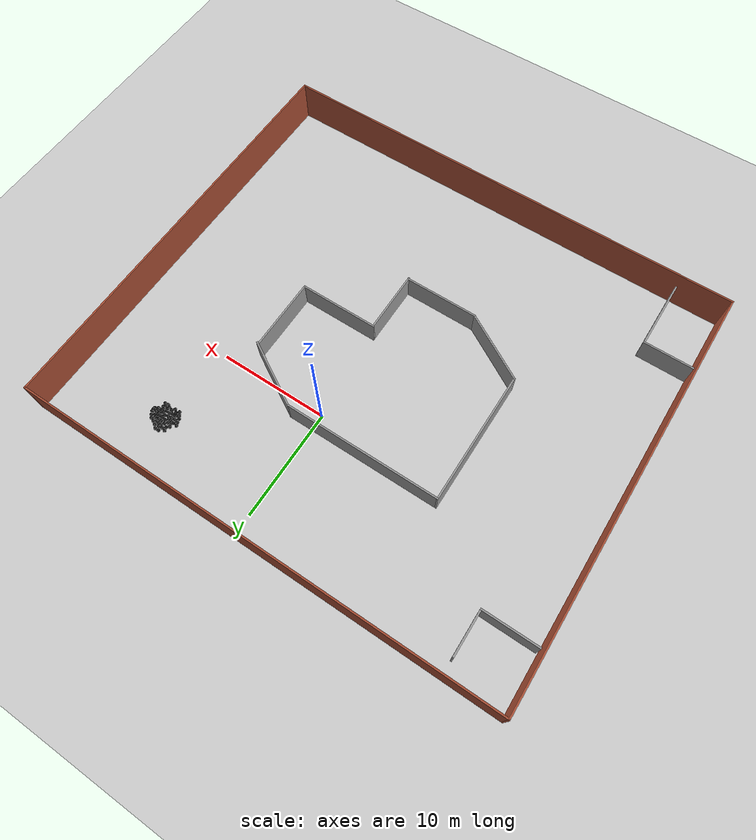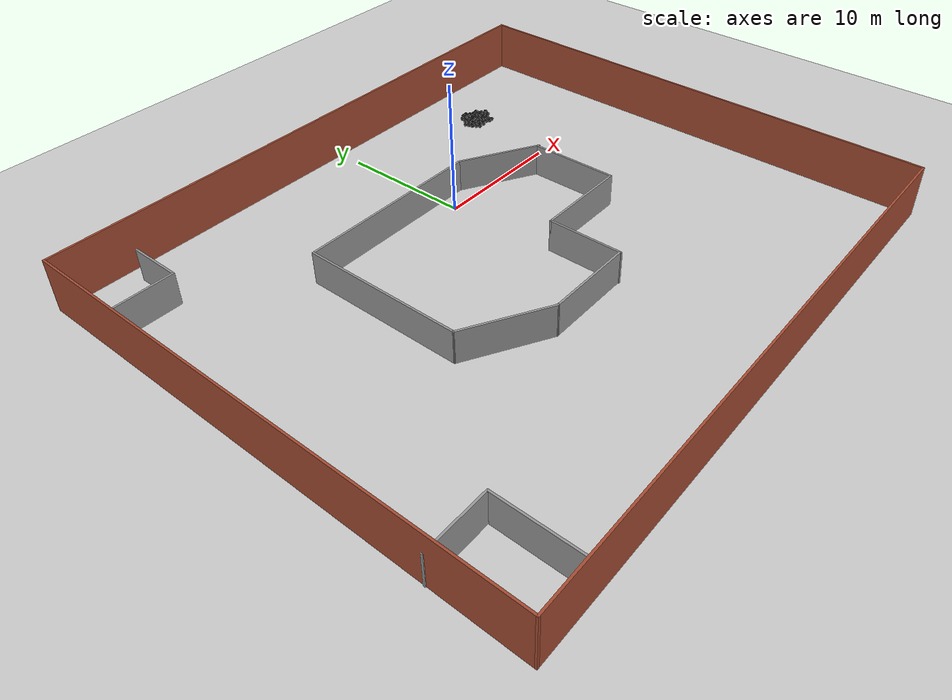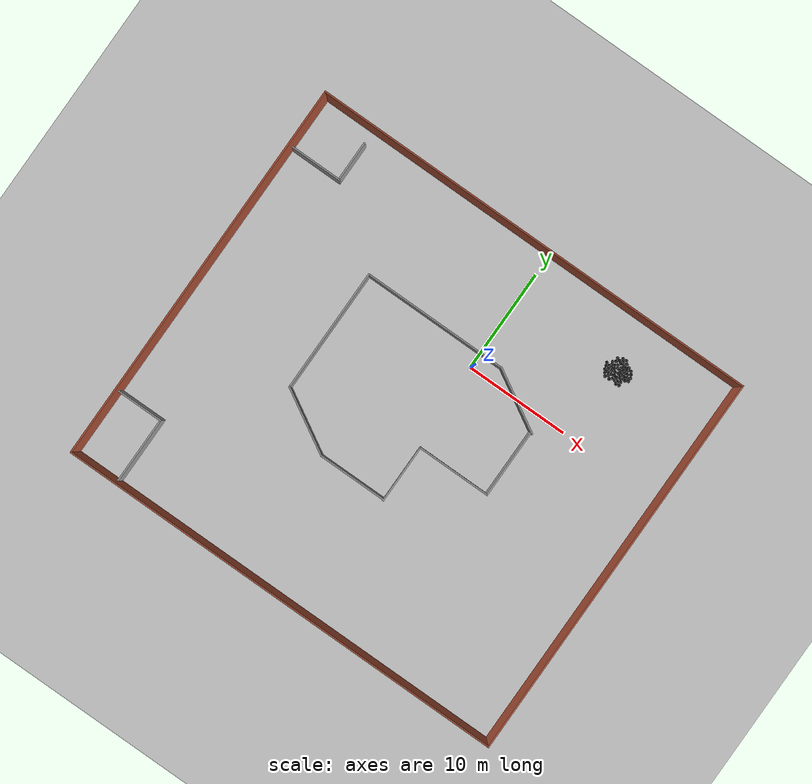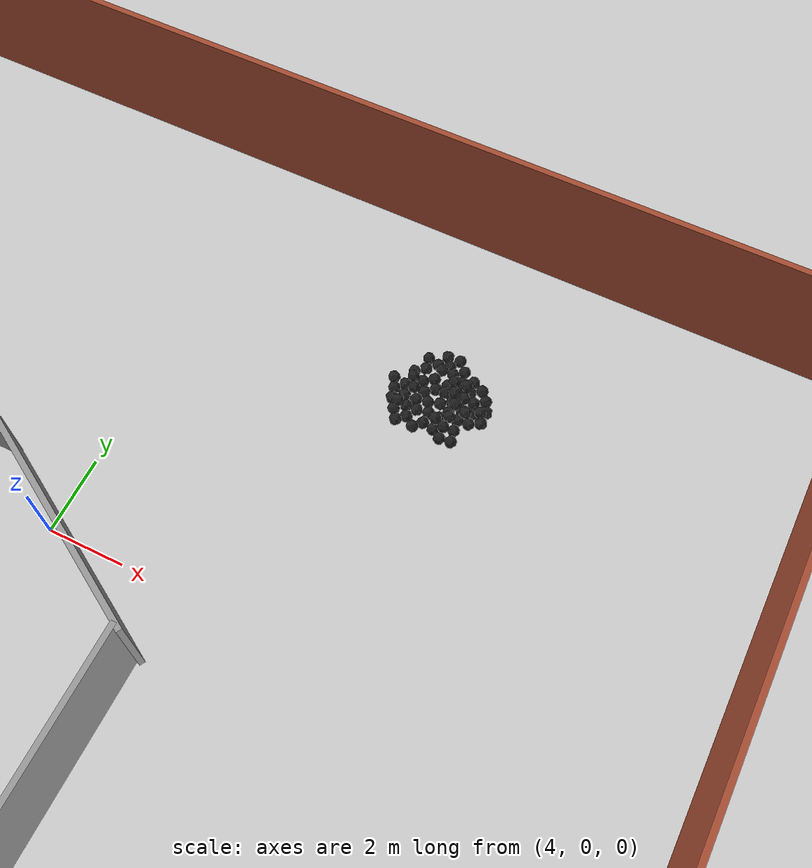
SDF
<sdf version="1.7">
 <world name="default">
  <light name="sun" type="directional">
   <pose>0 0 10 0 -0 0</pose>
   <diffuse>0.8 0.8 0.8 1</diffuse>
   <specular>0.2 0.2 0.2 1</specular>
   <attenuation>
    <range>1000</range>
    <constant>0.9</constant>
    <linear>0.01</linear>
    <quadratic>0.001</quadratic>
   </attenuation>
   <direction>-0.5 0.1 -0.9</direction>
   <spot><inner_angle>0</inner_angle><outer_angle>0</outer_angle><falloff>0</falloff></spot>
  </light>
  <model name="ground_plane">
   <static>1</static>
   <link name="link">
    <collision name="collision">
     <geometry><plane><normal>0 0 1</normal><size>100 100</size></plane></geometry>
     <surface><friction><ode><mu>100</mu><mu2>50</mu2></ode></friction></surface>
    </collision>
    <visual name="visual">
     <cast_shadows>0</cast_shadows>
     <geometry><plane><normal>0 0 1</normal><size>100 100</size></plane></geometry>
     <material>
      <script><uri>file://media/materials/scripts/gazebo.material</uri><name>Gazebo/Grey</name></script>
     </material>
    </visual>
   </link>
  </model>
  <gravity>0 0 -9.8</gravity>
  <magnetic_field>6e-06 2.3e-05 -4.2e-05</magnetic_field>
  <atmosphere type="adiabatic"/>
  <physics name="default_physics" default="0" type="ode">
   <max_step_size>0.001</max_step_size>
   <real_time_factor>1</real_time_factor>
   <real_time_update_rate>1000</real_time_update_rate>
  </physics>
  <scene><ambient>0.4 0.4 0.4 1</ambient><background>0.7 0.7 0.7 1</background><shadows>1</shadows></scene>
  <audio><device>default</device></audio>
  <spherical_coordinates>
   <surface_model>EARTH_WGS84</surface_model>
   <latitude_deg>0</latitude_deg>
   <longitude_deg>0</longitude_deg>
   <elevation>0</elevation>
   <heading_deg>0</heading_deg>
  </spherical_coordinates>
  <model name="wall11">
   <pose>-2 -7 0 0 -0 0</pose>
   <link name="Wall_0">
    <collision name="Wall_0_Collision">
     <geometry><box><size>44.15 0.15 4</size></box></geometry>
     <pose>0 0 2 0 -0 0</pose>
    </collision>
    <visual name="Wall_0_Visual">
     <pose>0 0 2 0 -0 0</pose>
     <geometry><box><size>44.15 0.15 4</size></box></geometry>
     <material>
      <script><uri>file://media/materials/scripts/gazebo.material</uri><name>Gazebo/Bricks</name></script>
      <ambient>1 1 1 1</ambient>
     </material>
     <meta><layer>0</layer></meta>
    </visual>
    <pose>0 19 0 0 -0 0</pose>
   </link>
   <link name="Wall_2">
    <collision name="Wall_2_Collision">
     <geometry><box><size>38.15 0.15 4</size></box></geometry>
     <pose>0 0 2 0 -0 0</pose>
    </collision>
    <visual name="Wall_2_Visual">
     <pose>0 0 2 0 -0 0</pose>
     <geometry><box><size>38.15 0.15 4</size></box></geometry>
     <material>
      <script><uri>file://media/materials/scripts/gazebo.material</uri><name>Gazebo/Bricks</name></script>
      <ambient>1 1 1 1</ambient>
     </material>
     <meta><layer>0</layer></meta>
    </visual>
    <pose>22 0 0 0 -0 -1.5708</pose>
   </link>
   <link name="Wall_4">
    <collision name="Wall_4_Collision">
     <geometry><box><size>44.15 0.15 4</size></box></geometry>
     <pose>0 0 2 0 -0 0</pose>
    </collision>
    <visual name="Wall_4_Visual">
     <pose>0 0 2 0 -0 0</pose>
     <geometry><box><size>44.15 0.15 4</size></box></geometry>
     <material>
      <script><uri>file://media/materials/scripts/gazebo.material</uri><name>Gazebo/Bricks</name></script>
      <ambient>1 1 1 1</ambient>
     </material>
     <meta><layer>0</layer></meta>
    </visual>
    <pose>0 -19 0 0 -0 3.14159</pose>
   </link>
   <link name="Wall_6">
    <collision name="Wall_6_Collision">
     <geometry><box><size>38.15 0.15 4</size></box></geometry>
     <pose>0 0 2 0 -0 0</pose>
    </collision>
    <visual name="Wall_6_Visual">
     <pose>0 0 2 0 -0 0</pose>
     <geometry><box><size>38.15 0.15 4</size></box></geometry>
     <material>
      <script><uri>file://media/materials/scripts/gazebo.material</uri><name>Gazebo/Bricks</name></script>
      <ambient>1 1 1 1</ambient>
     </material>
     <meta><layer>0</layer></meta>
    </visual>
    <pose>-22 0 0 0 -0 1.5708</pose>
   </link>
   <static>1</static>
  </model>
  <model name="haoduomiantiaa_1">
   <link name="link_0">
    <inertial>
     <mass>0.2</mass>
     <inertia>
      <ixx>0.166667</ixx>
      <ixy>0</ixy>
      <ixz>0</ixz>
      <iyy>0.166667</iyy>
      <iyz>0</iyz>
      <izz>0.166667</izz>
     </inertia>
    </inertial>
    <visual name="visual">
     <geometry>
      <mesh>
       <uri>/home/lihaoyang/catkin_ws/src/pudong_gazebo/world/stl/haoduomianti.stl</uri>
       <scale>1 1 1</scale>
      </mesh>
     </geometry>
     <material>
      <lighting>1</lighting>
      <script><uri>file://media/materials/scripts/gazebo.material</uri><name>Gazebo/Black</name></script>
      <shader type="pixel"><normal_map>__default__</normal_map></shader>
      <ambient>0.3 0.3 0.3 1</ambient>
      <diffuse>0.7 0.7 0.7 1</diffuse>
      <specular>0.01 0.01 0.01 1</specular>
      <emissive>0 0 0 1</emissive>
     </material>
    </visual>
    <collision name="collision">
     <geometry>
      <mesh>
       <uri>/home/lihaoyang/catkin_ws/src/pudong_gazebo/world/stl/haoduomianti.stl</uri>
       <scale>1 1 1</scale>
      </mesh>
     </geometry>
     <surface>
      <friction>
       <ode><mu>1</mu><mu2>1</mu2><fdir1>0 0 0</fdir1><slip1>0</slip1><slip2>0</slip2></ode>
       <torsional>
        <coefficient>1</coefficient>
        <patch_radius>0</patch_radius>
        <surface_radius>0</surface_radius>
        <use_patch_radius>1</use_patch_radius>
        <ode><slip>0</slip></ode>
       </torsional>
      </friction>
      <bounce><restitution_coefficient>0</restitution_coefficient><threshold>1e+06</threshold></bounce>
      <contact>
       <collide_without_contact>0</collide_without_contact>
       <collide_without_contact_bitmask>1</collide_without_contact_bitmask>
       <collide_bitmask>1</collide_bitmask>
       <ode>
        <soft_cfm>0</soft_cfm>
        <soft_erp>0.2</soft_erp>
        <kp>1e+13</kp>
        <kd>1</kd>
        <max_vel>0.01</max_vel>
        <min_depth>0</min_depth>
       </ode>
       <bullet>
        <split_impulse>1</split_impulse>
        <split_impulse_penetration_threshold>-0.01</split_impulse_penetration_threshold>
        <soft_cfm>0</soft_cfm>
        <soft_erp>0.2</soft_erp>
        <kp>1e+13</kp>
        <kd>1</kd>
       </bullet>
      </contact>
     </surface>
    </collision>
   </link>
   <static>0</static>
   <pose>10.7707 6.73714 -0.115511 0.785241 -0.615547 0.266136</pose>
  </model>
  <model name="haoduomiantiaa_2">
   <link name="link_0">
    <inertial>
     <mass>0.2</mass>
     <inertia>
      <ixx>0.166667</ixx>
      <ixy>0</ixy>
      <ixz>0</ixz>
      <iyy>0.166667</iyy>
      <iyz>0</iyz>
      <izz>0.166667</izz>
     </inertia>
    </inertial>
    <visual name="visual">
     <geometry>
      <mesh>
       <uri>/home/lihaoyang/catkin_ws/src/pudong_gazebo/world/stl/haoduomianti.stl</uri>
       <scale>1 1 1</scale>
      </mesh>
     </geometry>
     <material>
      <lighting>1</lighting>
      <script><uri>file://media/materials/scripts/gazebo.material</uri><name>Gazebo/Black</name></script>
      <shader type="pixel"><normal_map>__default__</normal_map></shader>
      <ambient>0.3 0.3 0.3 1</ambient>
      <diffuse>0.7 0.7 0.7 1</diffuse>
      <specular>0.01 0.01 0.01 1</specular>
      <emissive>0 0 0 1</emissive>
     </material>
    </visual>
    <collision name="collision">
     <geometry>
      <mesh>
       <uri>/home/lihaoyang/catkin_ws/src/pudong_gazebo/world/stl/haoduomianti.stl</uri>
       <scale>1 1 1</scale>
      </mesh>
     </geometry>
     <surface>
      <friction>
       <ode><mu>1</mu><mu2>1</mu2><fdir1>0 0 0</fdir1><slip1>0</slip1><slip2>0</slip2></ode>
       <torsional>
        <coefficient>1</coefficient>
        <patch_radius>0</patch_radius>
        <surface_radius>0</surface_radius>
        <use_patch_radius>1</use_patch_radius>
        <ode><slip>0</slip></ode>
       </torsional>
      </friction>
      <bounce><restitution_coefficient>0</restitution_coefficient><threshold>1e+06</threshold></bounce>
      <contact>
       <collide_without_contact>0</collide_without_contact>
       <collide_without_contact_bitmask>1</collide_without_contact_bitmask>
       <collide_bitmask>1</collide_bitmask>
       <ode>
        <soft_cfm>0</soft_cfm>
        <soft_erp>0.2</soft_erp>
        <kp>1e+13</kp>
        <kd>1</kd>
        <max_vel>0.01</max_vel>
        <min_depth>0</min_depth>
       </ode>
       <bullet>
        <split_impulse>1</split_impulse>
        <split_impulse_penetration_threshold>-0.01</split_impulse_penetration_threshold>
        <soft_cfm>0</soft_cfm>
        <soft_erp>0.2</soft_erp>
        <kp>1e+13</kp>
        <kd>1</kd>
       </bullet>
      </contact>
     </surface>
    </collision>
   </link>
   <static>0</static>
   <pose>11.3988 7.2776 -0.078914 1.45342 -0.781946 0.657755</pose>
  </model>
  <model name="haoduomiantiaa_4">
   <link name="link_0">
    <inertial>
     <mass>0.2</mass>
     <inertia>
      <ixx>0.166667</ixx>
      <ixy>0</ixy>
      <ixz>0</ixz>
      <iyy>0.166667</iyy>
      <iyz>0</iyz>
      <izz>0.166667</izz>
     </inertia>
    </inertial>
    <visual name="visual">
     <geometry>
      <mesh>
       <uri>/home/lihaoyang/catkin_ws/src/pudong_gazebo/world/stl/haoduomianti.stl</uri>
       <scale>1 1 1</scale>
      </mesh>
     </geometry>
     <material>
      <lighting>1</lighting>
      <script><uri>file://media/materials/scripts/gazebo.material</uri><name>Gazebo/Black</name></script>
      <shader type="pixel"><normal_map>__default__</normal_map></shader>
      <ambient>0.3 0.3 0.3 1</ambient>
      <diffuse>0.7 0.7 0.7 1</diffuse>
      <specular>0.01 0.01 0.01 1</specular>
      <emissive>0 0 0 1</emissive>
     </material>
    </visual>
    <collision name="collision">
     <geometry>
      <mesh>
       <uri>/home/lihaoyang/catkin_ws/src/pudong_gazebo/world/stl/haoduomianti.stl</uri>
       <scale>1 1 1</scale>
      </mesh>
     </geometry>
     <surface>
      <friction>
       <ode><mu>1</mu><mu2>1</mu2><fdir1>0 0 0</fdir1><slip1>0</slip1><slip2>0</slip2></ode>
       <torsional>
        <coefficient>1</coefficient>
        <patch_radius>0</patch_radius>
        <surface_radius>0</surface_radius>
        <use_patch_radius>1</use_patch_radius>
        <ode><slip>0</slip></ode>
       </torsional>
      </friction>
      <bounce><restitution_coefficient>0</restitution_coefficient><threshold>1e+06</threshold></bounce>
      <contact>
       <collide_without_contact>0</collide_without_contact>
       <collide_without_contact_bitmask>1</collide_without_contact_bitmask>
       <collide_bitmask>1</collide_bitmask>
       <ode>
        <soft_cfm>0</soft_cfm>
        <soft_erp>0.2</soft_erp>
        <kp>1e+13</kp>
        <kd>1</kd>
        <max_vel>0.01</max_vel>
        <min_depth>0</min_depth>
       </ode>
       <bullet>
        <split_impulse>1</split_impulse>
        <split_impulse_penetration_threshold>-0.01</split_impulse_penetration_threshold>
        <soft_cfm>0</soft_cfm>
        <soft_erp>0.2</soft_erp>
        <kp>1e+13</kp>
        <kd>1</kd>
       </bullet>
      </contact>
     </surface>
    </collision>
   </link>
   <static>0</static>
   <pose>11.7712 7.19134 -0.115666 0.785393 -0.615464 0.502665</pose>
  </model>
  <model name="haoduomiantiaa_5">
   <link name="link_0">
    <inertial>
     <mass>0.2</mass>
     <inertia>
      <ixx>0.166667</ixx>
      <ixy>0</ixy>
      <ixz>0</ixz>
      <iyy>0.166667</iyy>
      <iyz>0</iyz>
      <izz>0.166667</izz>
     </inertia>
    </inertial>
    <visual name="visual">
     <geometry>
      <mesh>
       <uri>/home/lihaoyang/catkin_ws/src/pudong_gazebo/world/stl/haoduomianti.stl</uri>
       <scale>1 1 1</scale>
      </mesh>
     </geometry>
     <material>
      <lighting>1</lighting>
      <script><uri>file://media/materials/scripts/gazebo.material</uri><name>Gazebo/Black</name></script>
      <shader type="pixel"><normal_map>__default__</normal_map></shader>
      <ambient>0.3 0.3 0.3 1</ambient>
      <diffuse>0.7 0.7 0.7 1</diffuse>
      <specular>0.01 0.01 0.01 1</specular>
      <emissive>0 0 0 1</emissive>
     </material>
    </visual>
    <collision name="collision">
     <geometry>
      <mesh>
       <uri>/home/lihaoyang/catkin_ws/src/pudong_gazebo/world/stl/haoduomianti.stl</uri>
       <scale>1 1 1</scale>
      </mesh>
     </geometry>
     <surface>
      <friction>
       <ode><mu>1</mu><mu2>1</mu2><fdir1>0 0 0</fdir1><slip1>0</slip1><slip2>0</slip2></ode>
       <torsional>
        <coefficient>1</coefficient>
        <patch_radius>0</patch_radius>
        <surface_radius>0</surface_radius>
        <use_patch_radius>1</use_patch_radius>
        <ode><slip>0</slip></ode>
       </torsional>
      </friction>
      <bounce><restitution_coefficient>0</restitution_coefficient><threshold>1e+06</threshold></bounce>
      <contact>
       <collide_without_contact>0</collide_without_contact>
       <collide_without_contact_bitmask>1</collide_without_contact_bitmask>
       <collide_bitmask>1</collide_bitmask>
       <ode>
        <soft_cfm>0</soft_cfm>
        <soft_erp>0.2</soft_erp>
        <kp>1e+13</kp>
        <kd>1</kd>
        <max_vel>0.01</max_vel>
        <min_depth>0</min_depth>
       </ode>
       <bullet>
        <split_impulse>1</split_impulse>
        <split_impulse_penetration_threshold>-0.01</split_impulse_penetration_threshold>
        <soft_cfm>0</soft_cfm>
        <soft_erp>0.2</soft_erp>
        <kp>1e+13</kp>
        <kd>1</kd>
       </bullet>
      </contact>
     </surface>
    </collision>
   </link>
   <static>0</static>
   <pose>11.7983 6.88109 -0.115471 0.785183 -0.61558 -2.61596</pose>
  </model>
  <model name="haoduomiantiaa_9">
   <link name="link_0">
    <inertial>
     <mass>0.2</mass>
     <inertia>
      <ixx>0.166667</ixx>
      <ixy>0</ixy>
      <ixz>0</ixz>
      <iyy>0.166667</iyy>
      <iyz>0</iyz>
      <izz>0.166667</izz>
     </inertia>
    </inertial>
    <visual name="visual">
     <geometry>
      <mesh>
       <uri>/home/lihaoyang/catkin_ws/src/pudong_gazebo/world/stl/haoduomianti.stl</uri>
       <scale>1 1 1</scale>
      </mesh>
     </geometry>
     <material>
      <lighting>1</lighting>
      <script><uri>file://media/materials/scripts/gazebo.material</uri><name>Gazebo/Black</name></script>
      <shader type="pixel"><normal_map>__default__</normal_map></shader>
      <ambient>0.3 0.3 0.3 1</ambient>
      <diffuse>0.7 0.7 0.7 1</diffuse>
      <specular>0.01 0.01 0.01 1</specular>
      <emissive>0 0 0 1</emissive>
     </material>
    </visual>
    <collision name="collision">
     <geometry>
      <mesh>
       <uri>/home/lihaoyang/catkin_ws/src/pudong_gazebo/world/stl/haoduomianti.stl</uri>
       <scale>1 1 1</scale>
      </mesh>
     </geometry>
     <surface>
      <friction>
       <ode><mu>1</mu><mu2>1</mu2><fdir1>0 0 0</fdir1><slip1>0</slip1><slip2>0</slip2></ode>
       <torsional>
        <coefficient>1</coefficient>
        <patch_radius>0</patch_radius>
        <surface_radius>0</surface_radius>
        <use_patch_radius>1</use_patch_radius>
        <ode><slip>0</slip></ode>
       </torsional>
      </friction>
      <bounce><restitution_coefficient>0</restitution_coefficient><threshold>1e+06</threshold></bounce>
      <contact>
       <collide_without_contact>0</collide_without_contact>
       <collide_without_contact_bitmask>1</collide_without_contact_bitmask>
       <collide_bitmask>1</collide_bitmask>
       <ode>
        <soft_cfm>0</soft_cfm>
        <soft_erp>0.2</soft_erp>
        <kp>1e+13</kp>
        <kd>1</kd>
        <max_vel>0.01</max_vel>
        <min_depth>0</min_depth>
       </ode>
       <bullet>
        <split_impulse>1</split_impulse>
        <split_impulse_penetration_threshold>-0.01</split_impulse_penetration_threshold>
        <soft_cfm>0</soft_cfm>
        <soft_erp>0.2</soft_erp>
        <kp>1e+13</kp>
        <kd>1</kd>
       </bullet>
      </contact>
     </surface>
    </collision>
   </link>
   <static>0</static>
   <pose>10.7412 7.39431 -0.094796 0.373444 -0.749649 1.1395</pose>
  </model>
  <model name="haoduomiantiaa_10">
   <link name="link_0">
    <inertial>
     <mass>0.2</mass>
     <inertia>
      <ixx>0.166667</ixx>
      <ixy>0</ixy>
      <ixz>0</ixz>
      <iyy>0.166667</iyy>
      <iyz>0</iyz>
      <izz>0.166667</izz>
     </inertia>
    </inertial>
    <visual name="visual">
     <geometry>
      <mesh>
       <uri>/home/lihaoyang/catkin_ws/src/pudong_gazebo/world/stl/haoduomianti.stl</uri>
       <scale>1 1 1</scale>
      </mesh>
     </geometry>
     <material>
      <lighting>1</lighting>
      <script><uri>file://media/materials/scripts/gazebo.material</uri><name>Gazebo/Black</name></script>
      <shader type="pixel"><normal_map>__default__</normal_map></shader>
      <ambient>0.3 0.3 0.3 1</ambient>
      <diffuse>0.7 0.7 0.7 1</diffuse>
      <specular>0.01 0.01 0.01 1</specular>
      <emissive>0 0 0 1</emissive>
     </material>
    </visual>
    <collision name="collision">
     <geometry>
      <mesh>
       <uri>/home/lihaoyang/catkin_ws/src/pudong_gazebo/world/stl/haoduomianti.stl</uri>
       <scale>1 1 1</scale>
      </mesh>
     </geometry>
     <surface>
      <friction>
       <ode><mu>1</mu><mu2>1</mu2><fdir1>0 0 0</fdir1><slip1>0</slip1><slip2>0</slip2></ode>
       <torsional>
        <coefficient>1</coefficient>
        <patch_radius>0</patch_radius>
        <surface_radius>0</surface_radius>
        <use_patch_radius>1</use_patch_radius>
        <ode><slip>0</slip></ode>
       </torsional>
      </friction>
      <bounce><restitution_coefficient>0</restitution_coefficient><threshold>1e+06</threshold></bounce>
      <contact>
       <collide_without_contact>0</collide_without_contact>
       <collide_without_contact_bitmask>1</collide_without_contact_bitmask>
       <collide_bitmask>1</collide_bitmask>
       <ode>
        <soft_cfm>0</soft_cfm>
        <soft_erp>0.2</soft_erp>
        <kp>1e+13</kp>
        <kd>1</kd>
        <max_vel>0.01</max_vel>
        <min_depth>0</min_depth>
       </ode>
       <bullet>
        <split_impulse>1</split_impulse>
        <split_impulse_penetration_threshold>-0.01</split_impulse_penetration_threshold>
        <soft_cfm>0</soft_cfm>
        <soft_erp>0.2</soft_erp>
        <kp>1e+13</kp>
        <kd>1</kd>
       </bullet>
      </contact>
     </surface>
    </collision>
   </link>
   <static>0</static>
   <pose>11.5827 6.9581 -0.080952 1.42056 -0.779728 -0.513314</pose>
  </model>
  <model name="haoduomiantiaa_11">
   <link name="link_0">
    <inertial>
     <mass>0.2</mass>
     <inertia>
      <ixx>0.166667</ixx>
      <ixy>0</ixy>
      <ixz>0</ixz>
      <iyy>0.166667</iyy>
      <iyz>0</iyz>
      <izz>0.166667</izz>
     </inertia>
    </inertial>
    <visual name="visual">
     <geometry>
      <mesh>
       <uri>/home/lihaoyang/catkin_ws/src/pudong_gazebo/world/stl/haoduomianti.stl</uri>
       <scale>1 1 1</scale>
      </mesh>
     </geometry>
     <material>
      <lighting>1</lighting>
      <script><uri>file://media/materials/scripts/gazebo.material</uri><name>Gazebo/Black</name></script>
      <shader type="pixel"><normal_map>__default__</normal_map></shader>
      <ambient>0.3 0.3 0.3 1</ambient>
      <diffuse>0.7 0.7 0.7 1</diffuse>
      <specular>0.01 0.01 0.01 1</specular>
      <emissive>0 0 0 1</emissive>
     </material>
    </visual>
    <collision name="collision">
     <geometry>
      <mesh>
       <uri>/home/lihaoyang/catkin_ws/src/pudong_gazebo/world/stl/haoduomianti.stl</uri>
       <scale>1 1 1</scale>
      </mesh>
     </geometry>
     <surface>
      <friction>
       <ode><mu>1</mu><mu2>1</mu2><fdir1>0 0 0</fdir1><slip1>0</slip1><slip2>0</slip2></ode>
       <torsional>
        <coefficient>1</coefficient>
        <patch_radius>0</patch_radius>
        <surface_radius>0</surface_radius>
        <use_patch_radius>1</use_patch_radius>
        <ode><slip>0</slip></ode>
       </torsional>
      </friction>
      <bounce><restitution_coefficient>0</restitution_coefficient><threshold>1e+06</threshold></bounce>
      <contact>
       <collide_without_contact>0</collide_without_contact>
       <collide_without_contact_bitmask>1</collide_without_contact_bitmask>
       <collide_bitmask>1</collide_bitmask>
       <ode>
        <soft_cfm>0</soft_cfm>
        <soft_erp>0.2</soft_erp>
        <kp>1e+13</kp>
        <kd>1</kd>
        <max_vel>0.01</max_vel>
        <min_depth>0</min_depth>
       </ode>
       <bullet>
        <split_impulse>1</split_impulse>
        <split_impulse_penetration_threshold>-0.01</split_impulse_penetration_threshold>
        <soft_cfm>0</soft_cfm>
        <soft_erp>0.2</soft_erp>
        <kp>1e+13</kp>
        <kd>1</kd>
       </bullet>
      </contact>
     </surface>
    </collision>
   </link>
   <static>0</static>
   <pose>10.2685 7.47808 -0.113912 0.74513 -0.633824 0.167006</pose>
  </model>
  <model name="haoduomiantiaa_14">
   <link name="link_0">
    <inertial>
     <mass>0.2</mass>
     <inertia>
      <ixx>0.166667</ixx>
      <ixy>0</ixy>
      <ixz>0</ixz>
      <iyy>0.166667</iyy>
      <iyz>0</iyz>
      <izz>0.166667</izz>
     </inertia>
    </inertial>
    <visual name="visual">
     <geometry>
      <mesh>
       <uri>/home/lihaoyang/catkin_ws/src/pudong_gazebo/world/stl/haoduomianti.stl</uri>
       <scale>1 1 1</scale>
      </mesh>
     </geometry>
     <material>
      <lighting>1</lighting>
      <script><uri>file://media/materials/scripts/gazebo.material</uri><name>Gazebo/Black</name></script>
      <shader type="pixel"><normal_map>__default__</normal_map></shader>
      <ambient>0.3 0.3 0.3 1</ambient>
      <diffuse>0.7 0.7 0.7 1</diffuse>
      <specular>0.01 0.01 0.01 1</specular>
      <emissive>0 0 0 1</emissive>
     </material>
    </visual>
    <collision name="collision">
     <geometry>
      <mesh>
       <uri>/home/lihaoyang/catkin_ws/src/pudong_gazebo/world/stl/haoduomianti.stl</uri>
       <scale>1 1 1</scale>
      </mesh>
     </geometry>
     <surface>
      <friction>
       <ode><mu>1</mu><mu2>1</mu2><fdir1>0 0 0</fdir1><slip1>0</slip1><slip2>0</slip2></ode>
       <torsional>
        <coefficient>1</coefficient>
        <patch_radius>0</patch_radius>
        <surface_radius>0</surface_radius>
        <use_patch_radius>1</use_patch_radius>
        <ode><slip>0</slip></ode>
       </torsional>
      </friction>
      <bounce><restitution_coefficient>0</restitution_coefficient><threshold>1e+06</threshold></bounce>
      <contact>
       <collide_without_contact>0</collide_without_contact>
       <collide_without_contact_bitmask>1</collide_without_contact_bitmask>
       <collide_bitmask>1</collide_bitmask>
       <ode>
        <soft_cfm>0</soft_cfm>
        <soft_erp>0.2</soft_erp>
        <kp>1e+13</kp>
        <kd>1</kd>
        <max_vel>0.01</max_vel>
        <min_depth>0</min_depth>
       </ode>
       <bullet>
        <split_impulse>1</split_impulse>
        <split_impulse_penetration_threshold>-0.01</split_impulse_penetration_threshold>
        <soft_cfm>0</soft_cfm>
        <soft_erp>0.2</soft_erp>
        <kp>1e+13</kp>
        <kd>1</kd>
       </bullet>
      </contact>
     </surface>
    </collision>
   </link>
   <static>0</static>
   <pose>11.5498 6.54871 -0.115476 0.78541 -0.615461 -0.401961</pose>
  </model>
  <model name="haoduomiantiaa_17">
   <link name="link_0">
    <inertial>
     <mass>0.2</mass>
     <inertia>
      <ixx>0.166667</ixx>
      <ixy>0</ixy>
      <ixz>0</ixz>
      <iyy>0.166667</iyy>
      <iyz>0</iyz>
      <izz>0.166667</izz>
     </inertia>
    </inertial>
    <visual name="visual">
     <geometry>
      <mesh>
       <uri>/home/lihaoyang/catkin_ws/src/pudong_gazebo/world/stl/haoduomianti.stl</uri>
       <scale>1 1 1</scale>
      </mesh>
     </geometry>
     <material>
      <lighting>1</lighting>
      <script><uri>file://media/materials/scripts/gazebo.material</uri><name>Gazebo/Black</name></script>
      <shader type="pixel"><normal_map>__default__</normal_map></shader>
      <ambient>0.3 0.3 0.3 1</ambient>
      <diffuse>0.7 0.7 0.7 1</diffuse>
      <specular>0.01 0.01 0.01 1</specular>
      <emissive>0 0 0 1</emissive>
     </material>
    </visual>
    <collision name="collision">
     <geometry>
      <mesh>
       <uri>/home/lihaoyang/catkin_ws/src/pudong_gazebo/world/stl/haoduomianti.stl</uri>
       <scale>1 1 1</scale>
      </mesh>
     </geometry>
     <surface>
      <friction>
       <ode><mu>1</mu><mu2>1</mu2><fdir1>0 0 0</fdir1><slip1>0</slip1><slip2>0</slip2></ode>
       <torsional>
        <coefficient>1</coefficient>
        <patch_radius>0</patch_radius>
        <surface_radius>0</surface_radius>
        <use_patch_radius>1</use_patch_radius>
        <ode><slip>0</slip></ode>
       </torsional>
      </friction>
      <bounce><restitution_coefficient>0</restitution_coefficient><threshold>1e+06</threshold></bounce>
      <contact>
       <collide_without_contact>0</collide_without_contact>
       <collide_without_contact_bitmask>1</collide_without_contact_bitmask>
       <collide_bitmask>1</collide_bitmask>
       <ode>
        <soft_cfm>0</soft_cfm>
        <soft_erp>0.2</soft_erp>
        <kp>1e+13</kp>
        <kd>1</kd>
        <max_vel>0.01</max_vel>
        <min_depth>0</min_depth>
       </ode>
       <bullet>
        <split_impulse>1</split_impulse>
        <split_impulse_penetration_threshold>-0.01</split_impulse_penetration_threshold>
        <soft_cfm>0</soft_cfm>
        <soft_erp>0.2</soft_erp>
        <kp>1e+13</kp>
        <kd>1</kd>
       </bullet>
      </contact>
     </surface>
    </collision>
   </link>
   <static>0</static>
   <pose>10.8713 7.6405 -0.115457 0.785399 -0.615167 -0.408592</pose>
  </model>
  <model name="haoduomiantiaa_18">
   <link name="link_0">
    <inertial>
     <mass>0.2</mass>
     <inertia>
      <ixx>0.166667</ixx>
      <ixy>0</ixy>
      <ixz>0</ixz>
      <iyy>0.166667</iyy>
      <iyz>0</iyz>
      <izz>0.166667</izz>
     </inertia>
    </inertial>
    <visual name="visual">
     <geometry>
      <mesh>
       <uri>/home/lihaoyang/catkin_ws/src/pudong_gazebo/world/stl/haoduomianti.stl</uri>
       <scale>1 1 1</scale>
      </mesh>
     </geometry>
     <material>
      <lighting>1</lighting>
      <script><uri>file://media/materials/scripts/gazebo.material</uri><name>Gazebo/Black</name></script>
      <shader type="pixel"><normal_map>__default__</normal_map></shader>
      <ambient>0.3 0.3 0.3 1</ambient>
      <diffuse>0.7 0.7 0.7 1</diffuse>
      <specular>0.01 0.01 0.01 1</specular>
      <emissive>0 0 0 1</emissive>
     </material>
    </visual>
    <collision name="collision">
     <geometry>
      <mesh>
       <uri>/home/lihaoyang/catkin_ws/src/pudong_gazebo/world/stl/haoduomianti.stl</uri>
       <scale>1 1 1</scale>
      </mesh>
     </geometry>
     <surface>
      <friction>
       <ode><mu>1</mu><mu2>1</mu2><fdir1>0 0 0</fdir1><slip1>0</slip1><slip2>0</slip2></ode>
       <torsional>
        <coefficient>1</coefficient>
        <patch_radius>0</patch_radius>
        <surface_radius>0</surface_radius>
        <use_patch_radius>1</use_patch_radius>
        <ode><slip>0</slip></ode>
       </torsional>
      </friction>
      <bounce><restitution_coefficient>0</restitution_coefficient><threshold>1e+06</threshold></bounce>
      <contact>
       <collide_without_contact>0</collide_without_contact>
       <collide_without_contact_bitmask>1</collide_without_contact_bitmask>
       <collide_bitmask>1</collide_bitmask>
       <ode>
        <soft_cfm>0</soft_cfm>
        <soft_erp>0.2</soft_erp>
        <kp>1e+13</kp>
        <kd>1</kd>
        <max_vel>0.01</max_vel>
        <min_depth>0</min_depth>
       </ode>
       <bullet>
        <split_impulse>1</split_impulse>
        <split_impulse_penetration_threshold>-0.01</split_impulse_penetration_threshold>
        <soft_cfm>0</soft_cfm>
        <soft_erp>0.2</soft_erp>
        <kp>1e+13</kp>
        <kd>1</kd>
       </bullet>
      </contact>
     </surface>
    </collision>
   </link>
   <static>0</static>
   <pose>11.1506 7.80971 -0.105065 0.55611 -0.704088 -0.768022</pose>
  </model>
  <model name="haoduomiantiaa_20">
   <link name="link_0">
    <inertial>
     <mass>0.2</mass>
     <inertia>
      <ixx>0.166667</ixx>
      <ixy>0</ixy>
      <ixz>0</ixz>
      <iyy>0.166667</iyy>
      <iyz>0</iyz>
      <izz>0.166667</izz>
     </inertia>
    </inertial>
    <visual name="visual">
     <geometry>
      <mesh>
       <uri>/home/lihaoyang/catkin_ws/src/pudong_gazebo/world/stl/haoduomianti.stl</uri>
       <scale>1 1 1</scale>
      </mesh>
     </geometry>
     <material>
      <lighting>1</lighting>
      <script><uri>file://media/materials/scripts/gazebo.material</uri><name>Gazebo/Black</name></script>
      <shader type="pixel"><normal_map>__default__</normal_map></shader>
      <ambient>0.3 0.3 0.3 1</ambient>
      <diffuse>0.7 0.7 0.7 1</diffuse>
      <specular>0.01 0.01 0.01 1</specular>
      <emissive>0 0 0 1</emissive>
     </material>
    </visual>
    <collision name="collision">
     <geometry>
      <mesh>
       <uri>/home/lihaoyang/catkin_ws/src/pudong_gazebo/world/stl/haoduomianti.stl</uri>
       <scale>1 1 1</scale>
      </mesh>
     </geometry>
     <surface>
      <friction>
       <ode><mu>1</mu><mu2>1</mu2><fdir1>0 0 0</fdir1><slip1>0</slip1><slip2>0</slip2></ode>
       <torsional>
        <coefficient>1</coefficient>
        <patch_radius>0</patch_radius>
        <surface_radius>0</surface_radius>
        <use_patch_radius>1</use_patch_radius>
        <ode><slip>0</slip></ode>
       </torsional>
      </friction>
      <bounce><restitution_coefficient>0</restitution_coefficient><threshold>1e+06</threshold></bounce>
      <contact>
       <collide_without_contact>0</collide_without_contact>
       <collide_without_contact_bitmask>1</collide_without_contact_bitmask>
       <collide_bitmask>1</collide_bitmask>
       <ode>
        <soft_cfm>0</soft_cfm>
        <soft_erp>0.2</soft_erp>
        <kp>1e+13</kp>
        <kd>1</kd>
        <max_vel>0.01</max_vel>
        <min_depth>0</min_depth>
       </ode>
       <bullet>
        <split_impulse>1</split_impulse>
        <split_impulse_penetration_threshold>-0.01</split_impulse_penetration_threshold>
        <soft_cfm>0</soft_cfm>
        <soft_erp>0.2</soft_erp>
        <kp>1e+13</kp>
        <kd>1</kd>
       </bullet>
      </contact>
     </surface>
    </collision>
   </link>
   <static>0</static>
   <pose>10.9284 7.93338 -0.034302 0.823031 -0.752775 -0.326742</pose>
  </model>
  <model name="haoduomiantiaa_21">
   <link name="link_0">
    <inertial>
     <mass>0.2</mass>
     <inertia>
      <ixx>0.166667</ixx>
      <ixy>0</ixy>
      <ixz>0</ixz>
      <iyy>0.166667</iyy>
      <iyz>0</iyz>
      <izz>0.166667</izz>
     </inertia>
    </inertial>
    <visual name="visual">
     <geometry>
      <mesh>
       <uri>/home/lihaoyang/catkin_ws/src/pudong_gazebo/world/stl/haoduomianti.stl</uri>
       <scale>1 1 1</scale>
      </mesh>
     </geometry>
     <material>
      <lighting>1</lighting>
      <script><uri>file://media/materials/scripts/gazebo.material</uri><name>Gazebo/Black</name></script>
      <shader type="pixel"><normal_map>__default__</normal_map></shader>
      <ambient>0.3 0.3 0.3 1</ambient>
      <diffuse>0.7 0.7 0.7 1</diffuse>
      <specular>0.01 0.01 0.01 1</specular>
      <emissive>0 0 0 1</emissive>
     </material>
    </visual>
    <collision name="collision">
     <geometry>
      <mesh>
       <uri>/home/lihaoyang/catkin_ws/src/pudong_gazebo/world/stl/haoduomianti.stl</uri>
       <scale>1 1 1</scale>
      </mesh>
     </geometry>
     <surface>
      <friction>
       <ode><mu>1</mu><mu2>1</mu2><fdir1>0 0 0</fdir1><slip1>0</slip1><slip2>0</slip2></ode>
       <torsional>
        <coefficient>1</coefficient>
        <patch_radius>0</patch_radius>
        <surface_radius>0</surface_radius>
        <use_patch_radius>1</use_patch_radius>
        <ode><slip>0</slip></ode>
       </torsional>
      </friction>
      <bounce><restitution_coefficient>0</restitution_coefficient><threshold>1e+06</threshold></bounce>
      <contact>
       <collide_without_contact>0</collide_without_contact>
       <collide_without_contact_bitmask>1</collide_without_contact_bitmask>
       <collide_bitmask>1</collide_bitmask>
       <ode>
        <soft_cfm>0</soft_cfm>
        <soft_erp>0.2</soft_erp>
        <kp>1e+13</kp>
        <kd>1</kd>
        <max_vel>0.01</max_vel>
        <min_depth>0</min_depth>
       </ode>
       <bullet>
        <split_impulse>1</split_impulse>
        <split_impulse_penetration_threshold>-0.01</split_impulse_penetration_threshold>
        <soft_cfm>0</soft_cfm>
        <soft_erp>0.2</soft_erp>
        <kp>1e+13</kp>
        <kd>1</kd>
       </bullet>
      </contact>
     </surface>
    </collision>
   </link>
   <static>0</static>
   <pose>10.7084 8.08724 -0.10261 1.06124 -0.717663 -2.71904</pose>
  </model>
  <model name="haoduomiantiaa_25">
   <link name="link_0">
    <inertial>
     <mass>0.2</mass>
     <inertia>
      <ixx>0.166667</ixx>
      <ixy>0</ixy>
      <ixz>0</ixz>
      <iyy>0.166667</iyy>
      <iyz>0</iyz>
      <izz>0.166667</izz>
     </inertia>
    </inertial>
    <visual name="visual">
     <geometry>
      <mesh>
       <uri>/home/lihaoyang/catkin_ws/src/pudong_gazebo/world/stl/haoduomianti.stl</uri>
       <scale>1 1 1</scale>
      </mesh>
     </geometry>
     <material>
      <lighting>1</lighting>
      <script><uri>file://media/materials/scripts/gazebo.material</uri><name>Gazebo/Black</name></script>
      <shader type="pixel"><normal_map>__default__</normal_map></shader>
      <ambient>0.3 0.3 0.3 1</ambient>
      <diffuse>0.7 0.7 0.7 1</diffuse>
      <specular>0.01 0.01 0.01 1</specular>
      <emissive>0 0 0 1</emissive>
     </material>
    </visual>
    <collision name="collision">
     <geometry>
      <mesh>
       <uri>/home/lihaoyang/catkin_ws/src/pudong_gazebo/world/stl/haoduomianti.stl</uri>
       <scale>1 1 1</scale>
      </mesh>
     </geometry>
     <surface>
      <friction>
       <ode><mu>1</mu><mu2>1</mu2><fdir1>0 0 0</fdir1><slip1>0</slip1><slip2>0</slip2></ode>
       <torsional>
        <coefficient>1</coefficient>
        <patch_radius>0</patch_radius>
        <surface_radius>0</surface_radius>
        <use_patch_radius>1</use_patch_radius>
        <ode><slip>0</slip></ode>
       </torsional>
      </friction>
      <bounce><restitution_coefficient>0</restitution_coefficient><threshold>1e+06</threshold></bounce>
      <contact>
       <collide_without_contact>0</collide_without_contact>
       <collide_without_contact_bitmask>1</collide_without_contact_bitmask>
       <collide_bitmask>1</collide_bitmask>
       <ode>
        <soft_cfm>0</soft_cfm>
        <soft_erp>0.2</soft_erp>
        <kp>1e+13</kp>
        <kd>1</kd>
        <max_vel>0.01</max_vel>
        <min_depth>0</min_depth>
       </ode>
       <bullet>
        <split_impulse>1</split_impulse>
        <split_impulse_penetration_threshold>-0.01</split_impulse_penetration_threshold>
        <soft_cfm>0</soft_cfm>
        <soft_erp>0.2</soft_erp>
        <kp>1e+13</kp>
        <kd>1</kd>
       </bullet>
      </contact>
     </surface>
    </collision>
   </link>
   <static>0</static>
   <pose>11.1028 8.16487 -0.115498 0.785416 -0.61547 1.82614</pose>
  </model>
  <model name="haoduomiantiaa_26">
   <link name="link_0">
    <inertial>
     <mass>0.2</mass>
     <inertia>
      <ixx>0.166667</ixx>
      <ixy>0</ixy>
      <ixz>0</ixz>
      <iyy>0.166667</iyy>
      <iyz>0</iyz>
      <izz>0.166667</izz>
     </inertia>
    </inertial>
    <visual name="visual">
     <geometry>
      <mesh>
       <uri>/home/lihaoyang/catkin_ws/src/pudong_gazebo/world/stl/haoduomianti.stl</uri>
       <scale>1 1 1</scale>
      </mesh>
     </geometry>
     <material>
      <lighting>1</lighting>
      <script><uri>file://media/materials/scripts/gazebo.material</uri><name>Gazebo/Black</name></script>
      <shader type="pixel"><normal_map>__default__</normal_map></shader>
      <ambient>0.3 0.3 0.3 1</ambient>
      <diffuse>0.7 0.7 0.7 1</diffuse>
      <specular>0.01 0.01 0.01 1</specular>
      <emissive>0 0 0 1</emissive>
     </material>
    </visual>
    <collision name="collision">
     <geometry>
      <mesh>
       <uri>/home/lihaoyang/catkin_ws/src/pudong_gazebo/world/stl/haoduomianti.stl</uri>
       <scale>1 1 1</scale>
      </mesh>
     </geometry>
     <surface>
      <friction>
       <ode><mu>1</mu><mu2>1</mu2><fdir1>0 0 0</fdir1><slip1>0</slip1><slip2>0</slip2></ode>
       <torsional>
        <coefficient>1</coefficient>
        <patch_radius>0</patch_radius>
        <surface_radius>0</surface_radius>
        <use_patch_radius>1</use_patch_radius>
        <ode><slip>0</slip></ode>
       </torsional>
      </friction>
      <bounce><restitution_coefficient>0</restitution_coefficient><threshold>1e+06</threshold></bounce>
      <contact>
       <collide_without_contact>0</collide_without_contact>
       <collide_without_contact_bitmask>1</collide_without_contact_bitmask>
       <collide_bitmask>1</collide_bitmask>
       <ode>
        <soft_cfm>0</soft_cfm>
        <soft_erp>0.2</soft_erp>
        <kp>1e+13</kp>
        <kd>1</kd>
        <max_vel>0.01</max_vel>
        <min_depth>0</min_depth>
       </ode>
       <bullet>
        <split_impulse>1</split_impulse>
        <split_impulse_penetration_threshold>-0.01</split_impulse_penetration_threshold>
        <soft_cfm>0</soft_cfm>
        <soft_erp>0.2</soft_erp>
        <kp>1e+13</kp>
        <kd>1</kd>
       </bullet>
      </contact>
     </surface>
    </collision>
   </link>
   <static>0</static>
   <pose>11.3089 6.21374 -0.115494 0.785426 -0.61553 1.85959</pose>
  </model>
  <model name="haoduomiantiaa_27">
   <link name="link_0">
    <inertial>
     <mass>0.2</mass>
     <inertia>
      <ixx>0.166667</ixx>
      <ixy>0</ixy>
      <ixz>0</ixz>
      <iyy>0.166667</iyy>
      <iyz>0</iyz>
      <izz>0.166667</izz>
     </inertia>
    </inertial>
    <visual name="visual">
     <geometry>
      <mesh>
       <uri>/home/lihaoyang/catkin_ws/src/pudong_gazebo/world/stl/haoduomianti.stl</uri>
       <scale>1 1 1</scale>
      </mesh>
     </geometry>
     <material>
      <lighting>1</lighting>
      <script><uri>file://media/materials/scripts/gazebo.material</uri><name>Gazebo/Black</name></script>
      <shader type="pixel"><normal_map>__default__</normal_map></shader>
      <ambient>0.3 0.3 0.3 1</ambient>
      <diffuse>0.7 0.7 0.7 1</diffuse>
      <specular>0.01 0.01 0.01 1</specular>
      <emissive>0 0 0 1</emissive>
     </material>
    </visual>
    <collision name="collision">
     <geometry>
      <mesh>
       <uri>/home/lihaoyang/catkin_ws/src/pudong_gazebo/world/stl/haoduomianti.stl</uri>
       <scale>1 1 1</scale>
      </mesh>
     </geometry>
     <surface>
      <friction>
       <ode><mu>1</mu><mu2>1</mu2><fdir1>0 0 0</fdir1><slip1>0</slip1><slip2>0</slip2></ode>
       <torsional>
        <coefficient>1</coefficient>
        <patch_radius>0</patch_radius>
        <surface_radius>0</surface_radius>
        <use_patch_radius>1</use_patch_radius>
        <ode><slip>0</slip></ode>
       </torsional>
      </friction>
      <bounce><restitution_coefficient>0</restitution_coefficient><threshold>1e+06</threshold></bounce>
      <contact>
       <collide_without_contact>0</collide_without_contact>
       <collide_without_contact_bitmask>1</collide_without_contact_bitmask>
       <collide_bitmask>1</collide_bitmask>
       <ode>
        <soft_cfm>0</soft_cfm>
        <soft_erp>0.2</soft_erp>
        <kp>1e+13</kp>
        <kd>1</kd>
        <max_vel>0.01</max_vel>
        <min_depth>0</min_depth>
       </ode>
       <bullet>
        <split_impulse>1</split_impulse>
        <split_impulse_penetration_threshold>-0.01</split_impulse_penetration_threshold>
        <soft_cfm>0</soft_cfm>
        <soft_erp>0.2</soft_erp>
        <kp>1e+13</kp>
        <kd>1</kd>
       </bullet>
      </contact>
     </surface>
    </collision>
   </link>
   <static>0</static>
   <pose>11.5682 7.40495 -0.083606 0.188912 -0.776427 -1.21551</pose>
  </model>
  <model name="haoduomiantiaa_28">
   <link name="link_0">
    <inertial>
     <mass>0.2</mass>
     <inertia>
      <ixx>0.166667</ixx>
      <ixy>0</ixy>
      <ixz>0</ixz>
      <iyy>0.166667</iyy>
      <iyz>0</iyz>
      <izz>0.166667</izz>
     </inertia>
    </inertial>
    <visual name="visual">
     <geometry>
      <mesh>
       <uri>/home/lihaoyang/catkin_ws/src/pudong_gazebo/world/stl/haoduomianti.stl</uri>
       <scale>1 1 1</scale>
      </mesh>
     </geometry>
     <material>
      <lighting>1</lighting>
      <script><uri>file://media/materials/scripts/gazebo.material</uri><name>Gazebo/Black</name></script>
      <shader type="pixel"><normal_map>__default__</normal_map></shader>
      <ambient>0.3 0.3 0.3 1</ambient>
      <diffuse>0.7 0.7 0.7 1</diffuse>
      <specular>0.01 0.01 0.01 1</specular>
      <emissive>0 0 0 1</emissive>
     </material>
    </visual>
    <collision name="collision">
     <geometry>
      <mesh>
       <uri>/home/lihaoyang/catkin_ws/src/pudong_gazebo/world/stl/haoduomianti.stl</uri>
       <scale>1 1 1</scale>
      </mesh>
     </geometry>
     <surface>
      <friction>
       <ode><mu>1</mu><mu2>1</mu2><fdir1>0 0 0</fdir1><slip1>0</slip1><slip2>0</slip2></ode>
       <torsional>
        <coefficient>1</coefficient>
        <patch_radius>0</patch_radius>
        <surface_radius>0</surface_radius>
        <use_patch_radius>1</use_patch_radius>
        <ode><slip>0</slip></ode>
       </torsional>
      </friction>
      <bounce><restitution_coefficient>0</restitution_coefficient><threshold>1e+06</threshold></bounce>
      <contact>
       <collide_without_contact>0</collide_without_contact>
       <collide_without_contact_bitmask>1</collide_without_contact_bitmask>
       <collide_bitmask>1</collide_bitmask>
       <ode>
        <soft_cfm>0</soft_cfm>
        <soft_erp>0.2</soft_erp>
        <kp>1e+13</kp>
        <kd>1</kd>
        <max_vel>0.01</max_vel>
        <min_depth>0</min_depth>
       </ode>
       <bullet>
        <split_impulse>1</split_impulse>
        <split_impulse_penetration_threshold>-0.01</split_impulse_penetration_threshold>
        <soft_cfm>0</soft_cfm>
        <soft_erp>0.2</soft_erp>
        <kp>1e+13</kp>
        <kd>1</kd>
       </bullet>
      </contact>
     </surface>
    </collision>
   </link>
   <static>0</static>
   <pose>10.4175 7.22543 -0.115694 0.785336 -0.615515 -1.64544</pose>
  </model>
  <model name="haoduomiantiaa_29">
   <link name="link_0">
    <inertial>
     <mass>0.2</mass>
     <inertia>
      <ixx>0.166667</ixx>
      <ixy>0</ixy>
      <ixz>0</ixz>
      <iyy>0.166667</iyy>
      <iyz>0</iyz>
      <izz>0.166667</izz>
     </inertia>
    </inertial>
    <visual name="visual">
     <geometry>
      <mesh>
       <uri>/home/lihaoyang/catkin_ws/src/pudong_gazebo/world/stl/haoduomianti.stl</uri>
       <scale>1 1 1</scale>
      </mesh>
     </geometry>
     <material>
      <lighting>1</lighting>
      <script><uri>file://media/materials/scripts/gazebo.material</uri><name>Gazebo/Black</name></script>
      <shader type="pixel"><normal_map>__default__</normal_map></shader>
      <ambient>0.3 0.3 0.3 1</ambient>
      <diffuse>0.7 0.7 0.7 1</diffuse>
      <specular>0.01 0.01 0.01 1</specular>
      <emissive>0 0 0 1</emissive>
     </material>
    </visual>
    <collision name="collision">
     <geometry>
      <mesh>
       <uri>/home/lihaoyang/catkin_ws/src/pudong_gazebo/world/stl/haoduomianti.stl</uri>
       <scale>1 1 1</scale>
      </mesh>
     </geometry>
     <surface>
      <friction>
       <ode><mu>1</mu><mu2>1</mu2><fdir1>0 0 0</fdir1><slip1>0</slip1><slip2>0</slip2></ode>
       <torsional>
        <coefficient>1</coefficient>
        <patch_radius>0</patch_radius>
        <surface_radius>0</surface_radius>
        <use_patch_radius>1</use_patch_radius>
        <ode><slip>0</slip></ode>
       </torsional>
      </friction>
      <bounce><restitution_coefficient>0</restitution_coefficient><threshold>1e+06</threshold></bounce>
      <contact>
       <collide_without_contact>0</collide_without_contact>
       <collide_without_contact_bitmask>1</collide_without_contact_bitmask>
       <collide_bitmask>1</collide_bitmask>
       <ode>
        <soft_cfm>0</soft_cfm>
        <soft_erp>0.2</soft_erp>
        <kp>1e+13</kp>
        <kd>1</kd>
        <max_vel>0.01</max_vel>
        <min_depth>0</min_depth>
       </ode>
       <bullet>
        <split_impulse>1</split_impulse>
        <split_impulse_penetration_threshold>-0.01</split_impulse_penetration_threshold>
        <soft_cfm>0</soft_cfm>
        <soft_erp>0.2</soft_erp>
        <kp>1e+13</kp>
        <kd>1</kd>
       </bullet>
      </contact>
     </surface>
    </collision>
   </link>
   <static>0</static>
   <pose>11.4332 8.00231 -0.115928 0.785502 -0.615455 1.84341</pose>
  </model>
  <model name="haoduomiantiaa_30">
   <link name="link_0">
    <inertial>
     <mass>0.2</mass>
     <inertia>
      <ixx>0.166667</ixx>
      <ixy>0</ixy>
      <ixz>0</ixz>
      <iyy>0.166667</iyy>
      <iyz>0</iyz>
      <izz>0.166667</izz>
     </inertia>
    </inertial>
    <visual name="visual">
     <geometry>
      <mesh>
       <uri>/home/lihaoyang/catkin_ws/src/pudong_gazebo/world/stl/haoduomianti.stl</uri>
       <scale>1 1 1</scale>
      </mesh>
     </geometry>
     <material>
      <lighting>1</lighting>
      <script><uri>file://media/materials/scripts/gazebo.material</uri><name>Gazebo/Black</name></script>
      <shader type="pixel"><normal_map>__default__</normal_map></shader>
      <ambient>0.3 0.3 0.3 1</ambient>
      <diffuse>0.7 0.7 0.7 1</diffuse>
      <specular>0.01 0.01 0.01 1</specular>
      <emissive>0 0 0 1</emissive>
     </material>
    </visual>
    <collision name="collision">
     <geometry>
      <mesh>
       <uri>/home/lihaoyang/catkin_ws/src/pudong_gazebo/world/stl/haoduomianti.stl</uri>
       <scale>1 1 1</scale>
      </mesh>
     </geometry>
     <surface>
      <friction>
       <ode><mu>1</mu><mu2>1</mu2><fdir1>0 0 0</fdir1><slip1>0</slip1><slip2>0</slip2></ode>
       <torsional>
        <coefficient>1</coefficient>
        <patch_radius>0</patch_radius>
        <surface_radius>0</surface_radius>
        <use_patch_radius>1</use_patch_radius>
        <ode><slip>0</slip></ode>
       </torsional>
      </friction>
      <bounce><restitution_coefficient>0</restitution_coefficient><threshold>1e+06</threshold></bounce>
      <contact>
       <collide_without_contact>0</collide_without_contact>
       <collide_without_contact_bitmask>1</collide_without_contact_bitmask>
       <collide_bitmask>1</collide_bitmask>
       <ode>
        <soft_cfm>0</soft_cfm>
        <soft_erp>0.2</soft_erp>
        <kp>1e+13</kp>
        <kd>1</kd>
        <max_vel>0.01</max_vel>
        <min_depth>0</min_depth>
       </ode>
       <bullet>
        <split_impulse>1</split_impulse>
        <split_impulse_penetration_threshold>-0.01</split_impulse_penetration_threshold>
        <soft_cfm>0</soft_cfm>
        <soft_erp>0.2</soft_erp>
        <kp>1e+13</kp>
        <kd>1</kd>
       </bullet>
      </contact>
     </surface>
    </collision>
   </link>
   <static>0</static>
   <pose>11.1733 7.26258 -0.115473 0.785215 -0.615662 -1.66822</pose>
  </model>
  <model name="haoduomiantiaa_31">
   <link name="link_0">
    <inertial>
     <mass>0.2</mass>
     <inertia>
      <ixx>0.166667</ixx>
      <ixy>0</ixy>
      <ixz>0</ixz>
      <iyy>0.166667</iyy>
      <iyz>0</iyz>
      <izz>0.166667</izz>
     </inertia>
    </inertial>
    <visual name="visual">
     <geometry>
      <mesh>
       <uri>/home/lihaoyang/catkin_ws/src/pudong_gazebo/world/stl/haoduomianti.stl</uri>
       <scale>1 1 1</scale>
      </mesh>
     </geometry>
     <material>
      <lighting>1</lighting>
      <script><uri>file://media/materials/scripts/gazebo.material</uri><name>Gazebo/Black</name></script>
      <shader type="pixel"><normal_map>__default__</normal_map></shader>
      <ambient>0.3 0.3 0.3 1</ambient>
      <diffuse>0.7 0.7 0.7 1</diffuse>
      <specular>0.01 0.01 0.01 1</specular>
      <emissive>0 0 0 1</emissive>
     </material>
    </visual>
    <collision name="collision">
     <geometry>
      <mesh>
       <uri>/home/lihaoyang/catkin_ws/src/pudong_gazebo/world/stl/haoduomianti.stl</uri>
       <scale>1 1 1</scale>
      </mesh>
     </geometry>
     <surface>
      <friction>
       <ode><mu>1</mu><mu2>1</mu2><fdir1>0 0 0</fdir1><slip1>0</slip1><slip2>0</slip2></ode>
       <torsional>
        <coefficient>1</coefficient>
        <patch_radius>0</patch_radius>
        <surface_radius>0</surface_radius>
        <use_patch_radius>1</use_patch_radius>
        <ode><slip>0</slip></ode>
       </torsional>
      </friction>
      <bounce><restitution_coefficient>0</restitution_coefficient><threshold>1e+06</threshold></bounce>
      <contact>
       <collide_without_contact>0</collide_without_contact>
       <collide_without_contact_bitmask>1</collide_without_contact_bitmask>
       <collide_bitmask>1</collide_bitmask>
       <ode>
        <soft_cfm>0</soft_cfm>
        <soft_erp>0.2</soft_erp>
        <kp>1e+13</kp>
        <kd>1</kd>
        <max_vel>0.01</max_vel>
        <min_depth>0</min_depth>
       </ode>
       <bullet>
        <split_impulse>1</split_impulse>
        <split_impulse_penetration_threshold>-0.01</split_impulse_penetration_threshold>
        <soft_cfm>0</soft_cfm>
        <soft_erp>0.2</soft_erp>
        <kp>1e+13</kp>
        <kd>1</kd>
       </bullet>
      </contact>
     </surface>
    </collision>
   </link>
   <static>0</static>
   <pose>10.501 7.66325 -0.115425 0.785508 -0.615625 -2.77699</pose>
  </model>
  <model name="haoduomiantiaa_33">
   <link name="link_0">
    <inertial>
     <mass>0.2</mass>
     <inertia>
      <ixx>0.166667</ixx>
      <ixy>0</ixy>
      <ixz>0</ixz>
      <iyy>0.166667</iyy>
      <iyz>0</iyz>
      <izz>0.166667</izz>
     </inertia>
    </inertial>
    <visual name="visual">
     <geometry>
      <mesh>
       <uri>/home/lihaoyang/catkin_ws/src/pudong_gazebo/world/stl/haoduomianti.stl</uri>
       <scale>1 1 1</scale>
      </mesh>
     </geometry>
     <material>
      <lighting>1</lighting>
      <script><uri>file://media/materials/scripts/gazebo.material</uri><name>Gazebo/Black</name></script>
      <shader type="pixel"><normal_map>__default__</normal_map></shader>
      <ambient>0.3 0.3 0.3 1</ambient>
      <diffuse>0.7 0.7 0.7 1</diffuse>
      <specular>0.01 0.01 0.01 1</specular>
      <emissive>0 0 0 1</emissive>
     </material>
    </visual>
    <collision name="collision">
     <geometry>
      <mesh>
       <uri>/home/lihaoyang/catkin_ws/src/pudong_gazebo/world/stl/haoduomianti.stl</uri>
       <scale>1 1 1</scale>
      </mesh>
     </geometry>
     <surface>
      <friction>
       <ode><mu>1</mu><mu2>1</mu2><fdir1>0 0 0</fdir1><slip1>0</slip1><slip2>0</slip2></ode>
       <torsional>
        <coefficient>1</coefficient>
        <patch_radius>0</patch_radius>
        <surface_radius>0</surface_radius>
        <use_patch_radius>1</use_patch_radius>
        <ode><slip>0</slip></ode>
       </torsional>
      </friction>
      <bounce><restitution_coefficient>0</restitution_coefficient><threshold>1e+06</threshold></bounce>
      <contact>
       <collide_without_contact>0</collide_without_contact>
       <collide_without_contact_bitmask>1</collide_without_contact_bitmask>
       <collide_bitmask>1</collide_bitmask>
       <ode>
        <soft_cfm>0</soft_cfm>
        <soft_erp>0.2</soft_erp>
        <kp>1e+13</kp>
        <kd>1</kd>
        <max_vel>0.01</max_vel>
        <min_depth>0</min_depth>
       </ode>
       <bullet>
        <split_impulse>1</split_impulse>
        <split_impulse_penetration_threshold>-0.01</split_impulse_penetration_threshold>
        <soft_cfm>0</soft_cfm>
        <soft_erp>0.2</soft_erp>
        <kp>1e+13</kp>
        <kd>1</kd>
       </bullet>
      </contact>
     </surface>
    </collision>
   </link>
   <static>0</static>
   <pose>10.1697 6.68176 -0.115468 0.785363 -0.615492 1.06337</pose>
  </model>
  <model name="haoduomiantiaa_34">
   <link name="link_0">
    <inertial>
     <mass>0.2</mass>
     <inertia>
      <ixx>0.166667</ixx>
      <ixy>0</ixy>
      <ixz>0</ixz>
      <iyy>0.166667</iyy>
      <iyz>0</iyz>
      <izz>0.166667</izz>
     </inertia>
    </inertial>
    <visual name="visual">
     <geometry>
      <mesh>
       <uri>/home/lihaoyang/catkin_ws/src/pudong_gazebo/world/stl/haoduomianti.stl</uri>
       <scale>1 1 1</scale>
      </mesh>
     </geometry>
     <material>
      <lighting>1</lighting>
      <script><uri>file://media/materials/scripts/gazebo.material</uri><name>Gazebo/Black</name></script>
      <shader type="pixel"><normal_map>__default__</normal_map></shader>
      <ambient>0.3 0.3 0.3 1</ambient>
      <diffuse>0.7 0.7 0.7 1</diffuse>
      <specular>0.01 0.01 0.01 1</specular>
      <emissive>0 0 0 1</emissive>
     </material>
    </visual>
    <collision name="collision">
     <geometry>
      <mesh>
       <uri>/home/lihaoyang/catkin_ws/src/pudong_gazebo/world/stl/haoduomianti.stl</uri>
       <scale>1 1 1</scale>
      </mesh>
     </geometry>
     <surface>
      <friction>
       <ode><mu>1</mu><mu2>1</mu2><fdir1>0 0 0</fdir1><slip1>0</slip1><slip2>0</slip2></ode>
       <torsional>
        <coefficient>1</coefficient>
        <patch_radius>0</patch_radius>
        <surface_radius>0</surface_radius>
        <use_patch_radius>1</use_patch_radius>
        <ode><slip>0</slip></ode>
       </torsional>
      </friction>
      <bounce><restitution_coefficient>0</restitution_coefficient><threshold>1e+06</threshold></bounce>
      <contact>
       <collide_without_contact>0</collide_without_contact>
       <collide_without_contact_bitmask>1</collide_without_contact_bitmask>
       <collide_bitmask>1</collide_bitmask>
       <ode>
        <soft_cfm>0</soft_cfm>
        <soft_erp>0.2</soft_erp>
        <kp>1e+13</kp>
        <kd>1</kd>
        <max_vel>0.01</max_vel>
        <min_depth>0</min_depth>
       </ode>
       <bullet>
        <split_impulse>1</split_impulse>
        <split_impulse_penetration_threshold>-0.01</split_impulse_penetration_threshold>
        <soft_cfm>0</soft_cfm>
        <soft_erp>0.2</soft_erp>
        <kp>1e+13</kp>
        <kd>1</kd>
       </bullet>
      </contact>
     </surface>
    </collision>
   </link>
   <static>0</static>
   <pose>10.3108 6.41066 -0.115508 0.785402 -0.615467 -0.781503</pose>
  </model>
  <model name="haoduomiantiaa_35">
   <link name="link_0">
    <inertial>
     <mass>0.2</mass>
     <inertia>
      <ixx>0.166667</ixx>
      <ixy>0</ixy>
      <ixz>0</ixz>
      <iyy>0.166667</iyy>
      <iyz>0</iyz>
      <izz>0.166667</izz>
     </inertia>
    </inertial>
    <visual name="visual">
     <geometry>
      <mesh>
       <uri>/home/lihaoyang/catkin_ws/src/pudong_gazebo/world/stl/haoduomianti.stl</uri>
       <scale>1 1 1</scale>
      </mesh>
     </geometry>
     <material>
      <lighting>1</lighting>
      <script><uri>file://media/materials/scripts/gazebo.material</uri><name>Gazebo/Black</name></script>
      <shader type="pixel"><normal_map>__default__</normal_map></shader>
      <ambient>0.3 0.3 0.3 1</ambient>
      <diffuse>0.7 0.7 0.7 1</diffuse>
      <specular>0.01 0.01 0.01 1</specular>
      <emissive>0 0 0 1</emissive>
     </material>
    </visual>
    <collision name="collision">
     <geometry>
      <mesh>
       <uri>/home/lihaoyang/catkin_ws/src/pudong_gazebo/world/stl/haoduomianti.stl</uri>
       <scale>1 1 1</scale>
      </mesh>
     </geometry>
     <surface>
      <friction>
       <ode><mu>1</mu><mu2>1</mu2><fdir1>0 0 0</fdir1><slip1>0</slip1><slip2>0</slip2></ode>
       <torsional>
        <coefficient>1</coefficient>
        <patch_radius>0</patch_radius>
        <surface_radius>0</surface_radius>
        <use_patch_radius>1</use_patch_radius>
        <ode><slip>0</slip></ode>
       </torsional>
      </friction>
      <bounce><restitution_coefficient>0</restitution_coefficient><threshold>1e+06</threshold></bounce>
      <contact>
       <collide_without_contact>0</collide_without_contact>
       <collide_without_contact_bitmask>1</collide_without_contact_bitmask>
       <collide_bitmask>1</collide_bitmask>
       <ode>
        <soft_cfm>0</soft_cfm>
        <soft_erp>0.2</soft_erp>
        <kp>1e+13</kp>
        <kd>1</kd>
        <max_vel>0.01</max_vel>
        <min_depth>0</min_depth>
       </ode>
       <bullet>
        <split_impulse>1</split_impulse>
        <split_impulse_penetration_threshold>-0.01</split_impulse_penetration_threshold>
        <soft_cfm>0</soft_cfm>
        <soft_erp>0.2</soft_erp>
        <kp>1e+13</kp>
        <kd>1</kd>
       </bullet>
      </contact>
     </surface>
    </collision>
   </link>
   <static>0</static>
   <pose>10.0026 6.93938 -0.115766 0.785302 -0.615574 0.426187</pose>
  </model>
  <model name="haoduomiantiaa_36">
   <link name="link_0">
    <inertial>
     <mass>0.2</mass>
     <inertia>
      <ixx>0.166667</ixx>
      <ixy>0</ixy>
      <ixz>0</ixz>
      <iyy>0.166667</iyy>
      <iyz>0</iyz>
      <izz>0.166667</izz>
     </inertia>
    </inertial>
    <visual name="visual">
     <geometry>
      <mesh>
       <uri>/home/lihaoyang/catkin_ws/src/pudong_gazebo/world/stl/haoduomianti.stl</uri>
       <scale>1 1 1</scale>
      </mesh>
     </geometry>
     <material>
      <lighting>1</lighting>
      <script><uri>file://media/materials/scripts/gazebo.material</uri><name>Gazebo/Black</name></script>
      <shader type="pixel"><normal_map>__default__</normal_map></shader>
      <ambient>0.3 0.3 0.3 1</ambient>
      <diffuse>0.7 0.7 0.7 1</diffuse>
      <specular>0.01 0.01 0.01 1</specular>
      <emissive>0 0 0 1</emissive>
     </material>
    </visual>
    <collision name="collision">
     <geometry>
      <mesh>
       <uri>/home/lihaoyang/catkin_ws/src/pudong_gazebo/world/stl/haoduomianti.stl</uri>
       <scale>1 1 1</scale>
      </mesh>
     </geometry>
     <surface>
      <friction>
       <ode><mu>1</mu><mu2>1</mu2><fdir1>0 0 0</fdir1><slip1>0</slip1><slip2>0</slip2></ode>
       <torsional>
        <coefficient>1</coefficient>
        <patch_radius>0</patch_radius>
        <surface_radius>0</surface_radius>
        <use_patch_radius>1</use_patch_radius>
        <ode><slip>0</slip></ode>
       </torsional>
      </friction>
      <bounce><restitution_coefficient>0</restitution_coefficient><threshold>1e+06</threshold></bounce>
      <contact>
       <collide_without_contact>0</collide_without_contact>
       <collide_without_contact_bitmask>1</collide_without_contact_bitmask>
       <collide_bitmask>1</collide_bitmask>
       <ode>
        <soft_cfm>0</soft_cfm>
        <soft_erp>0.2</soft_erp>
        <kp>1e+13</kp>
        <kd>1</kd>
        <max_vel>0.01</max_vel>
        <min_depth>0</min_depth>
       </ode>
       <bullet>
        <split_impulse>1</split_impulse>
        <split_impulse_penetration_threshold>-0.01</split_impulse_penetration_threshold>
        <soft_cfm>0</soft_cfm>
        <soft_erp>0.2</soft_erp>
        <kp>1e+13</kp>
        <kd>1</kd>
       </bullet>
      </contact>
     </surface>
    </collision>
   </link>
   <static>0</static>
   <pose>10.8323 7.41841 0.035604 0.361168 -0.87682 -2.65538</pose>
  </model>
  <model name="haoduomiantiaa_41">
   <link name="link_0">
    <inertial>
     <mass>0.2</mass>
     <inertia>
      <ixx>0.166667</ixx>
      <ixy>0</ixy>
      <ixz>0</ixz>
      <iyy>0.166667</iyy>
      <iyz>0</iyz>
      <izz>0.166667</izz>
     </inertia>
    </inertial>
    <visual name="visual">
     <geometry>
      <mesh>
       <uri>/home/lihaoyang/catkin_ws/src/pudong_gazebo/world/stl/haoduomianti.stl</uri>
       <scale>1 1 1</scale>
      </mesh>
     </geometry>
     <material>
      <lighting>1</lighting>
      <script><uri>file://media/materials/scripts/gazebo.material</uri><name>Gazebo/Black</name></script>
      <shader type="pixel"><normal_map>__default__</normal_map></shader>
      <ambient>0.3 0.3 0.3 1</ambient>
      <diffuse>0.7 0.7 0.7 1</diffuse>
      <specular>0.01 0.01 0.01 1</specular>
      <emissive>0 0 0 1</emissive>
     </material>
    </visual>
    <collision name="collision">
     <geometry>
      <mesh>
       <uri>/home/lihaoyang/catkin_ws/src/pudong_gazebo/world/stl/haoduomianti.stl</uri>
       <scale>1 1 1</scale>
      </mesh>
     </geometry>
     <surface>
      <friction>
       <ode><mu>1</mu><mu2>1</mu2><fdir1>0 0 0</fdir1><slip1>0</slip1><slip2>0</slip2></ode>
       <torsional>
        <coefficient>1</coefficient>
        <patch_radius>0</patch_radius>
        <surface_radius>0</surface_radius>
        <use_patch_radius>1</use_patch_radius>
        <ode><slip>0</slip></ode>
       </torsional>
      </friction>
      <bounce><restitution_coefficient>0</restitution_coefficient><threshold>1e+06</threshold></bounce>
      <contact>
       <collide_without_contact>0</collide_without_contact>
       <collide_without_contact_bitmask>1</collide_without_contact_bitmask>
       <collide_bitmask>1</collide_bitmask>
       <ode>
        <soft_cfm>0</soft_cfm>
        <soft_erp>0.2</soft_erp>
        <kp>1e+13</kp>
        <kd>1</kd>
        <max_vel>0.01</max_vel>
        <min_depth>0</min_depth>
       </ode>
       <bullet>
        <split_impulse>1</split_impulse>
        <split_impulse_penetration_threshold>-0.01</split_impulse_penetration_threshold>
        <soft_cfm>0</soft_cfm>
        <soft_erp>0.2</soft_erp>
        <kp>1e+13</kp>
        <kd>1</kd>
       </bullet>
      </contact>
     </surface>
    </collision>
   </link>
   <static>0</static>
   <pose>9.94137 7.65008 -0.115484 0.785388 -0.615423 1.91478</pose>
  </model>
  <model name="haoduomiantiaa_46">
   <link name="link_0">
    <inertial>
     <mass>0.2</mass>
     <inertia>
      <ixx>0.166667</ixx>
      <ixy>0</ixy>
      <ixz>0</ixz>
      <iyy>0.166667</iyy>
      <iyz>0</iyz>
      <izz>0.166667</izz>
     </inertia>
    </inertial>
    <visual name="visual">
     <geometry>
      <mesh>
       <uri>/home/lihaoyang/catkin_ws/src/pudong_gazebo/world/stl/haoduomianti.stl</uri>
       <scale>1 1 1</scale>
      </mesh>
     </geometry>
     <material>
      <lighting>1</lighting>
      <script><uri>file://media/materials/scripts/gazebo.material</uri><name>Gazebo/Black</name></script>
      <shader type="pixel"><normal_map>__default__</normal_map></shader>
      <ambient>0.3 0.3 0.3 1</ambient>
      <diffuse>0.7 0.7 0.7 1</diffuse>
      <specular>0.01 0.01 0.01 1</specular>
      <emissive>0 0 0 1</emissive>
     </material>
    </visual>
    <collision name="collision">
     <geometry>
      <mesh>
       <uri>/home/lihaoyang/catkin_ws/src/pudong_gazebo/world/stl/haoduomianti.stl</uri>
       <scale>1 1 1</scale>
      </mesh>
     </geometry>
     <surface>
      <friction>
       <ode><mu>1</mu><mu2>1</mu2><fdir1>0 0 0</fdir1><slip1>0</slip1><slip2>0</slip2></ode>
       <torsional>
        <coefficient>1</coefficient>
        <patch_radius>0</patch_radius>
        <surface_radius>0</surface_radius>
        <use_patch_radius>1</use_patch_radius>
        <ode><slip>0</slip></ode>
       </torsional>
      </friction>
      <bounce><restitution_coefficient>0</restitution_coefficient><threshold>1e+06</threshold></bounce>
      <contact>
       <collide_without_contact>0</collide_without_contact>
       <collide_without_contact_bitmask>1</collide_without_contact_bitmask>
       <collide_bitmask>1</collide_bitmask>
       <ode>
        <soft_cfm>0</soft_cfm>
        <soft_erp>0.2</soft_erp>
        <kp>1e+13</kp>
        <kd>1</kd>
        <max_vel>0.01</max_vel>
        <min_depth>0</min_depth>
       </ode>
       <bullet>
        <split_impulse>1</split_impulse>
        <split_impulse_penetration_threshold>-0.01</split_impulse_penetration_threshold>
        <soft_cfm>0</soft_cfm>
        <soft_erp>0.2</soft_erp>
        <kp>1e+13</kp>
        <kd>1</kd>
       </bullet>
      </contact>
     </surface>
    </collision>
   </link>
   <static>0</static>
   <pose>11.065 6.36783 -0.115479 0.785401 -0.615476 -0.237314</pose>
  </model>
  <model name="haoduomiantiaa_47">
   <link name="link_0">
    <inertial>
     <mass>0.2</mass>
     <inertia>
      <ixx>0.166667</ixx>
      <ixy>0</ixy>
      <ixz>0</ixz>
      <iyy>0.166667</iyy>
      <iyz>0</iyz>
      <izz>0.166667</izz>
     </inertia>
    </inertial>
    <visual name="visual">
     <geometry>
      <mesh>
       <uri>/home/lihaoyang/catkin_ws/src/pudong_gazebo/world/stl/haoduomianti.stl</uri>
       <scale>1 1 1</scale>
      </mesh>
     </geometry>
     <material>
      <lighting>1</lighting>
      <script><uri>file://media/materials/scripts/gazebo.material</uri><name>Gazebo/Black</name></script>
      <shader type="pixel"><normal_map>__default__</normal_map></shader>
      <ambient>0.3 0.3 0.3 1</ambient>
      <diffuse>0.7 0.7 0.7 1</diffuse>
      <specular>0.01 0.01 0.01 1</specular>
      <emissive>0 0 0 1</emissive>
     </material>
    </visual>
    <collision name="collision">
     <geometry>
      <mesh>
       <uri>/home/lihaoyang/catkin_ws/src/pudong_gazebo/world/stl/haoduomianti.stl</uri>
       <scale>1 1 1</scale>
      </mesh>
     </geometry>
     <surface>
      <friction>
       <ode><mu>1</mu><mu2>1</mu2><fdir1>0 0 0</fdir1><slip1>0</slip1><slip2>0</slip2></ode>
       <torsional>
        <coefficient>1</coefficient>
        <patch_radius>0</patch_radius>
        <surface_radius>0</surface_radius>
        <use_patch_radius>1</use_patch_radius>
        <ode><slip>0</slip></ode>
       </torsional>
      </friction>
      <bounce><restitution_coefficient>0</restitution_coefficient><threshold>1e+06</threshold></bounce>
      <contact>
       <collide_without_contact>0</collide_without_contact>
       <collide_without_contact_bitmask>1</collide_without_contact_bitmask>
       <collide_bitmask>1</collide_bitmask>
       <ode>
        <soft_cfm>0</soft_cfm>
        <soft_erp>0.2</soft_erp>
        <kp>1e+13</kp>
        <kd>1</kd>
        <max_vel>0.01</max_vel>
        <min_depth>0</min_depth>
       </ode>
       <bullet>
        <split_impulse>1</split_impulse>
        <split_impulse_penetration_threshold>-0.01</split_impulse_penetration_threshold>
        <soft_cfm>0</soft_cfm>
        <soft_erp>0.2</soft_erp>
        <kp>1e+13</kp>
        <kd>1</kd>
       </bullet>
      </contact>
     </surface>
    </collision>
   </link>
   <static>0</static>
   <pose>11.2253 7.53998 -0.108126 0.619911 -0.683182 0.326957</pose>
  </model>
  <model name="haoduomiantiaa_49">
   <link name="link_0">
    <inertial>
     <mass>0.2</mass>
     <inertia>
      <ixx>0.166667</ixx>
      <ixy>0</ixy>
      <ixz>0</ixz>
      <iyy>0.166667</iyy>
      <iyz>0</iyz>
      <izz>0.166667</izz>
     </inertia>
    </inertial>
    <visual name="visual">
     <geometry>
      <mesh>
       <uri>/home/lihaoyang/catkin_ws/src/pudong_gazebo/world/stl/haoduomianti.stl</uri>
       <scale>1 1 1</scale>
      </mesh>
     </geometry>
     <material>
      <lighting>1</lighting>
      <script><uri>file://media/materials/scripts/gazebo.material</uri><name>Gazebo/Black</name></script>
      <shader type="pixel"><normal_map>__default__</normal_map></shader>
      <ambient>0.3 0.3 0.3 1</ambient>
      <diffuse>0.7 0.7 0.7 1</diffuse>
      <specular>0.01 0.01 0.01 1</specular>
      <emissive>0 0 0 1</emissive>
     </material>
    </visual>
    <collision name="collision">
     <geometry>
      <mesh>
       <uri>/home/lihaoyang/catkin_ws/src/pudong_gazebo/world/stl/haoduomianti.stl</uri>
       <scale>1 1 1</scale>
      </mesh>
     </geometry>
     <surface>
      <friction>
       <ode><mu>1</mu><mu2>1</mu2><fdir1>0 0 0</fdir1><slip1>0</slip1><slip2>0</slip2></ode>
       <torsional>
        <coefficient>1</coefficient>
        <patch_radius>0</patch_radius>
        <surface_radius>0</surface_radius>
        <use_patch_radius>1</use_patch_radius>
        <ode><slip>0</slip></ode>
       </torsional>
      </friction>
      <bounce><restitution_coefficient>0</restitution_coefficient><threshold>1e+06</threshold></bounce>
      <contact>
       <collide_without_contact>0</collide_without_contact>
       <collide_without_contact_bitmask>1</collide_without_contact_bitmask>
       <collide_bitmask>1</collide_bitmask>
       <ode>
        <soft_cfm>0</soft_cfm>
        <soft_erp>0.2</soft_erp>
        <kp>1e+13</kp>
        <kd>1</kd>
        <max_vel>0.01</max_vel>
        <min_depth>0</min_depth>
       </ode>
       <bullet>
        <split_impulse>1</split_impulse>
        <split_impulse_penetration_threshold>-0.01</split_impulse_penetration_threshold>
        <soft_cfm>0</soft_cfm>
        <soft_erp>0.2</soft_erp>
        <kp>1e+13</kp>
        <kd>1</kd>
       </bullet>
      </contact>
     </surface>
    </collision>
   </link>
   <static>0</static>
   <pose>9.75301 6.72818 -0.115472 0.785401 -0.61548 -0.879953</pose>
  </model>
  <model name="haoduomiantiaa_51">
   <link name="link_0">
    <inertial>
     <mass>0.2</mass>
     <inertia>
      <ixx>0.166667</ixx>
      <ixy>0</ixy>
      <ixz>0</ixz>
      <iyy>0.166667</iyy>
      <iyz>0</iyz>
      <izz>0.166667</izz>
     </inertia>
    </inertial>
    <visual name="visual">
     <geometry>
      <mesh>
       <uri>/home/lihaoyang/catkin_ws/src/pudong_gazebo/world/stl/haoduomianti.stl</uri>
       <scale>1 1 1</scale>
      </mesh>
     </geometry>
     <material>
      <lighting>1</lighting>
      <script><uri>file://media/materials/scripts/gazebo.material</uri><name>Gazebo/Black</name></script>
      <shader type="pixel"><normal_map>__default__</normal_map></shader>
      <ambient>0.3 0.3 0.3 1</ambient>
      <diffuse>0.7 0.7 0.7 1</diffuse>
      <specular>0.01 0.01 0.01 1</specular>
      <emissive>0 0 0 1</emissive>
     </material>
    </visual>
    <collision name="collision">
     <geometry>
      <mesh>
       <uri>/home/lihaoyang/catkin_ws/src/pudong_gazebo/world/stl/haoduomianti.stl</uri>
       <scale>1 1 1</scale>
      </mesh>
     </geometry>
     <surface>
      <friction>
       <ode><mu>1</mu><mu2>1</mu2><fdir1>0 0 0</fdir1><slip1>0</slip1><slip2>0</slip2></ode>
       <torsional>
        <coefficient>1</coefficient>
        <patch_radius>0</patch_radius>
        <surface_radius>0</surface_radius>
        <use_patch_radius>1</use_patch_radius>
        <ode><slip>0</slip></ode>
       </torsional>
      </friction>
      <bounce><restitution_coefficient>0</restitution_coefficient><threshold>1e+06</threshold></bounce>
      <contact>
       <collide_without_contact>0</collide_without_contact>
       <collide_without_contact_bitmask>1</collide_without_contact_bitmask>
       <collide_bitmask>1</collide_bitmask>
       <ode>
        <soft_cfm>0</soft_cfm>
        <soft_erp>0.2</soft_erp>
        <kp>1e+13</kp>
        <kd>1</kd>
        <max_vel>0.01</max_vel>
        <min_depth>0</min_depth>
       </ode>
       <bullet>
        <split_impulse>1</split_impulse>
        <split_impulse_penetration_threshold>-0.01</split_impulse_penetration_threshold>
        <soft_cfm>0</soft_cfm>
        <soft_erp>0.2</soft_erp>
        <kp>1e+13</kp>
        <kd>1</kd>
       </bullet>
      </contact>
     </surface>
    </collision>
   </link>
   <static>0</static>
   <pose>12.0644 7.0301 -0.115545 0.785457 -0.615498 1.07147</pose>
  </model>
  <model name="haoduomiantiaa_53">
   <link name="link_0">
    <inertial>
     <mass>0.2</mass>
     <inertia>
      <ixx>0.166667</ixx>
      <ixy>0</ixy>
      <ixz>0</ixz>
      <iyy>0.166667</iyy>
      <iyz>0</iyz>
      <izz>0.166667</izz>
     </inertia>
    </inertial>
    <visual name="visual">
     <geometry>
      <mesh>
       <uri>/home/lihaoyang/catkin_ws/src/pudong_gazebo/world/stl/haoduomianti.stl</uri>
       <scale>1 1 1</scale>
      </mesh>
     </geometry>
     <material>
      <lighting>1</lighting>
      <script><uri>file://media/materials/scripts/gazebo.material</uri><name>Gazebo/Black</name></script>
      <shader type="pixel"><normal_map>__default__</normal_map></shader>
      <ambient>0.3 0.3 0.3 1</ambient>
      <diffuse>0.7 0.7 0.7 1</diffuse>
      <specular>0.01 0.01 0.01 1</specular>
      <emissive>0 0 0 1</emissive>
     </material>
    </visual>
    <collision name="collision">
     <geometry>
      <mesh>
       <uri>/home/lihaoyang/catkin_ws/src/pudong_gazebo/world/stl/haoduomianti.stl</uri>
       <scale>1 1 1</scale>
      </mesh>
     </geometry>
     <surface>
      <friction>
       <ode><mu>1</mu><mu2>1</mu2><fdir1>0 0 0</fdir1><slip1>0</slip1><slip2>0</slip2></ode>
       <torsional>
        <coefficient>1</coefficient>
        <patch_radius>0</patch_radius>
        <surface_radius>0</surface_radius>
        <use_patch_radius>1</use_patch_radius>
        <ode><slip>0</slip></ode>
       </torsional>
      </friction>
      <bounce><restitution_coefficient>0</restitution_coefficient><threshold>1e+06</threshold></bounce>
      <contact>
       <collide_without_contact>0</collide_without_contact>
       <collide_without_contact_bitmask>1</collide_without_contact_bitmask>
       <collide_bitmask>1</collide_bitmask>
       <ode>
        <soft_cfm>0</soft_cfm>
        <soft_erp>0.2</soft_erp>
        <kp>1e+13</kp>
        <kd>1</kd>
        <max_vel>0.01</max_vel>
        <min_depth>0</min_depth>
       </ode>
       <bullet>
        <split_impulse>1</split_impulse>
        <split_impulse_penetration_threshold>-0.01</split_impulse_penetration_threshold>
        <soft_cfm>0</soft_cfm>
        <soft_erp>0.2</soft_erp>
        <kp>1e+13</kp>
        <kd>1</kd>
       </bullet>
      </contact>
     </surface>
    </collision>
   </link>
   <static>0</static>
   <pose>9.89495 7.22504 -0.115479 0.785397 -0.615478 0.901003</pose>
  </model>
  <model name="haoduomiantiaa_54">
   <link name="link_0">
    <inertial>
     <mass>0.2</mass>
     <inertia>
      <ixx>0.166667</ixx>
      <ixy>0</ixy>
      <ixz>0</ixz>
      <iyy>0.166667</iyy>
      <iyz>0</iyz>
      <izz>0.166667</izz>
     </inertia>
    </inertial>
    <visual name="visual">
     <geometry>
      <mesh>
       <uri>/home/lihaoyang/catkin_ws/src/pudong_gazebo/world/stl/haoduomianti.stl</uri>
       <scale>1 1 1</scale>
      </mesh>
     </geometry>
     <material>
      <lighting>1</lighting>
      <script><uri>file://media/materials/scripts/gazebo.material</uri><name>Gazebo/Black</name></script>
      <shader type="pixel"><normal_map>__default__</normal_map></shader>
      <ambient>0.3 0.3 0.3 1</ambient>
      <diffuse>0.7 0.7 0.7 1</diffuse>
      <specular>0.01 0.01 0.01 1</specular>
      <emissive>0 0 0 1</emissive>
     </material>
    </visual>
    <collision name="collision">
     <geometry>
      <mesh>
       <uri>/home/lihaoyang/catkin_ws/src/pudong_gazebo/world/stl/haoduomianti.stl</uri>
       <scale>1 1 1</scale>
      </mesh>
     </geometry>
     <surface>
      <friction>
       <ode><mu>1</mu><mu2>1</mu2><fdir1>0 0 0</fdir1><slip1>0</slip1><slip2>0</slip2></ode>
       <torsional>
        <coefficient>1</coefficient>
        <patch_radius>0</patch_radius>
        <surface_radius>0</surface_radius>
        <use_patch_radius>1</use_patch_radius>
        <ode><slip>0</slip></ode>
       </torsional>
      </friction>
      <bounce><restitution_coefficient>0</restitution_coefficient><threshold>1e+06</threshold></bounce>
      <contact>
       <collide_without_contact>0</collide_without_contact>
       <collide_without_contact_bitmask>1</collide_without_contact_bitmask>
       <collide_bitmask>1</collide_bitmask>
       <ode>
        <soft_cfm>0</soft_cfm>
        <soft_erp>0.2</soft_erp>
        <kp>1e+13</kp>
        <kd>1</kd>
        <max_vel>0.01</max_vel>
        <min_depth>0</min_depth>
       </ode>
       <bullet>
        <split_impulse>1</split_impulse>
        <split_impulse_penetration_threshold>-0.01</split_impulse_penetration_threshold>
        <soft_cfm>0</soft_cfm>
        <soft_erp>0.2</soft_erp>
        <kp>1e+13</kp>
        <kd>1</kd>
       </bullet>
      </contact>
     </surface>
    </collision>
   </link>
   <static>0</static>
   <pose>11.1817 7.10432 -0.07151 1.55959 -0.785365 0.261435</pose>
  </model>
  <model name="haoduomiantiaa_57">
   <link name="link_0">
    <inertial>
     <mass>0.2</mass>
     <inertia>
      <ixx>0.166667</ixx>
      <ixy>0</ixy>
      <ixz>0</ixz>
      <iyy>0.166667</iyy>
      <iyz>0</iyz>
      <izz>0.166667</izz>
     </inertia>
    </inertial>
    <visual name="visual">
     <geometry>
      <mesh>
       <uri>/home/lihaoyang/catkin_ws/src/pudong_gazebo/world/stl/haoduomianti.stl</uri>
       <scale>1 1 1</scale>
      </mesh>
     </geometry>
     <material>
      <lighting>1</lighting>
      <script><uri>file://media/materials/scripts/gazebo.material</uri><name>Gazebo/Black</name></script>
      <shader type="pixel"><normal_map>__default__</normal_map></shader>
      <ambient>0.3 0.3 0.3 1</ambient>
      <diffuse>0.7 0.7 0.7 1</diffuse>
      <specular>0.01 0.01 0.01 1</specular>
      <emissive>0 0 0 1</emissive>
     </material>
    </visual>
    <collision name="collision">
     <geometry>
      <mesh>
       <uri>/home/lihaoyang/catkin_ws/src/pudong_gazebo/world/stl/haoduomianti.stl</uri>
       <scale>1 1 1</scale>
      </mesh>
     </geometry>
     <surface>
      <friction>
       <ode><mu>1</mu><mu2>1</mu2><fdir1>0 0 0</fdir1><slip1>0</slip1><slip2>0</slip2></ode>
       <torsional>
        <coefficient>1</coefficient>
        <patch_radius>0</patch_radius>
        <surface_radius>0</surface_radius>
        <use_patch_radius>1</use_patch_radius>
        <ode><slip>0</slip></ode>
       </torsional>
      </friction>
      <bounce><restitution_coefficient>0</restitution_coefficient><threshold>1e+06</threshold></bounce>
      <contact>
       <collide_without_contact>0</collide_without_contact>
       <collide_without_contact_bitmask>1</collide_without_contact_bitmask>
       <collide_bitmask>1</collide_bitmask>
       <ode>
        <soft_cfm>0</soft_cfm>
        <soft_erp>0.2</soft_erp>
        <kp>1e+13</kp>
        <kd>1</kd>
        <max_vel>0.01</max_vel>
        <min_depth>0</min_depth>
       </ode>
       <bullet>
        <split_impulse>1</split_impulse>
        <split_impulse_penetration_threshold>-0.01</split_impulse_penetration_threshold>
        <soft_cfm>0</soft_cfm>
        <soft_erp>0.2</soft_erp>
        <kp>1e+13</kp>
        <kd>1</kd>
       </bullet>
      </contact>
     </surface>
    </collision>
   </link>
   <static>0</static>
   <pose>9.93242 6.46568 -0.115455 0.78578 -0.615658 -1.80064</pose>
  </model>
  <model name="haoduomiantiaa_59">
   <link name="link_0">
    <inertial>
     <mass>0.2</mass>
     <inertia>
      <ixx>0.166667</ixx>
      <ixy>0</ixy>
      <ixz>0</ixz>
      <iyy>0.166667</iyy>
      <iyz>0</iyz>
      <izz>0.166667</izz>
     </inertia>
    </inertial>
    <visual name="visual">
     <geometry>
      <mesh>
       <uri>/home/lihaoyang/catkin_ws/src/pudong_gazebo/world/stl/haoduomianti.stl</uri>
       <scale>1 1 1</scale>
      </mesh>
     </geometry>
     <material>
      <lighting>1</lighting>
      <script><uri>file://media/materials/scripts/gazebo.material</uri><name>Gazebo/Black</name></script>
      <shader type="pixel"><normal_map>__default__</normal_map></shader>
      <ambient>0.3 0.3 0.3 1</ambient>
      <diffuse>0.7 0.7 0.7 1</diffuse>
      <specular>0.01 0.01 0.01 1</specular>
      <emissive>0 0 0 1</emissive>
     </material>
    </visual>
    <collision name="collision">
     <geometry>
      <mesh>
       <uri>/home/lihaoyang/catkin_ws/src/pudong_gazebo/world/stl/haoduomianti.stl</uri>
       <scale>1 1 1</scale>
      </mesh>
     </geometry>
     <surface>
      <friction>
       <ode><mu>1</mu><mu2>1</mu2><fdir1>0 0 0</fdir1><slip1>0</slip1><slip2>0</slip2></ode>
       <torsional>
        <coefficient>1</coefficient>
        <patch_radius>0</patch_radius>
        <surface_radius>0</surface_radius>
        <use_patch_radius>1</use_patch_radius>
        <ode><slip>0</slip></ode>
       </torsional>
      </friction>
      <bounce><restitution_coefficient>0</restitution_coefficient><threshold>1e+06</threshold></bounce>
      <contact>
       <collide_without_contact>0</collide_without_contact>
       <collide_without_contact_bitmask>1</collide_without_contact_bitmask>
       <collide_bitmask>1</collide_bitmask>
       <ode>
        <soft_cfm>0</soft_cfm>
        <soft_erp>0.2</soft_erp>
        <kp>1e+13</kp>
        <kd>1</kd>
        <max_vel>0.01</max_vel>
        <min_depth>0</min_depth>
       </ode>
       <bullet>
        <split_impulse>1</split_impulse>
        <split_impulse_penetration_threshold>-0.01</split_impulse_penetration_threshold>
        <soft_cfm>0</soft_cfm>
        <soft_erp>0.2</soft_erp>
        <kp>1e+13</kp>
        <kd>1</kd>
       </bullet>
      </contact>
     </surface>
    </collision>
   </link>
   <static>0</static>
   <pose>11.2893 6.45656 0.067062 0.756049 -0.571511 -0.18228</pose>
  </model>
  <model name="haoduomiantiaa_62">
   <link name="link_0">
    <inertial>
     <mass>0.2</mass>
     <inertia>
      <ixx>0.166667</ixx>
      <ixy>0</ixy>
      <ixz>0</ixz>
      <iyy>0.166667</iyy>
      <iyz>0</iyz>
      <izz>0.166667</izz>
     </inertia>
    </inertial>
    <visual name="visual">
     <geometry>
      <mesh>
       <uri>/home/lihaoyang/catkin_ws/src/pudong_gazebo/world/stl/haoduomianti.stl</uri>
       <scale>1 1 1</scale>
      </mesh>
     </geometry>
     <material>
      <lighting>1</lighting>
      <script><uri>file://media/materials/scripts/gazebo.material</uri><name>Gazebo/Black</name></script>
      <shader type="pixel"><normal_map>__default__</normal_map></shader>
      <ambient>0.3 0.3 0.3 1</ambient>
      <diffuse>0.7 0.7 0.7 1</diffuse>
      <specular>0.01 0.01 0.01 1</specular>
      <emissive>0 0 0 1</emissive>
     </material>
    </visual>
    <collision name="collision">
     <geometry>
      <mesh>
       <uri>/home/lihaoyang/catkin_ws/src/pudong_gazebo/world/stl/haoduomianti.stl</uri>
       <scale>1 1 1</scale>
      </mesh>
     </geometry>
     <surface>
      <friction>
       <ode><mu>1</mu><mu2>1</mu2><fdir1>0 0 0</fdir1><slip1>0</slip1><slip2>0</slip2></ode>
       <torsional>
        <coefficient>1</coefficient>
        <patch_radius>0</patch_radius>
        <surface_radius>0</surface_radius>
        <use_patch_radius>1</use_patch_radius>
        <ode><slip>0</slip></ode>
       </torsional>
      </friction>
      <bounce><restitution_coefficient>0</restitution_coefficient><threshold>1e+06</threshold></bounce>
      <contact>
       <collide_without_contact>0</collide_without_contact>
       <collide_without_contact_bitmask>1</collide_without_contact_bitmask>
       <collide_bitmask>1</collide_bitmask>
       <ode>
        <soft_cfm>0</soft_cfm>
        <soft_erp>0.2</soft_erp>
        <kp>1e+13</kp>
        <kd>1</kd>
        <max_vel>0.01</max_vel>
        <min_depth>0</min_depth>
       </ode>
       <bullet>
        <split_impulse>1</split_impulse>
        <split_impulse_penetration_threshold>-0.01</split_impulse_penetration_threshold>
        <soft_cfm>0</soft_cfm>
        <soft_erp>0.2</soft_erp>
        <kp>1e+13</kp>
        <kd>1</kd>
       </bullet>
      </contact>
     </surface>
    </collision>
   </link>
   <static>0</static>
   <pose>11.9301 7.63354 -0.115416 0.785267 -0.615616 -1.78642</pose>
  </model>
  <model name="haoduomiantiaa_65">
   <link name="link_0">
    <inertial>
     <mass>0.2</mass>
     <inertia>
      <ixx>0.166667</ixx>
      <ixy>0</ixy>
      <ixz>0</ixz>
      <iyy>0.166667</iyy>
      <iyz>0</iyz>
      <izz>0.166667</izz>
     </inertia>
    </inertial>
    <visual name="visual">
     <geometry>
      <mesh>
       <uri>/home/lihaoyang/catkin_ws/src/pudong_gazebo/world/stl/haoduomianti.stl</uri>
       <scale>1 1 1</scale>
      </mesh>
     </geometry>
     <material>
      <lighting>1</lighting>
      <script><uri>file://media/materials/scripts/gazebo.material</uri><name>Gazebo/Black</name></script>
      <shader type="pixel"><normal_map>__default__</normal_map></shader>
      <ambient>0.3 0.3 0.3 1</ambient>
      <diffuse>0.7 0.7 0.7 1</diffuse>
      <specular>0.01 0.01 0.01 1</specular>
      <emissive>0 0 0 1</emissive>
     </material>
    </visual>
    <collision name="collision">
     <geometry>
      <mesh>
       <uri>/home/lihaoyang/catkin_ws/src/pudong_gazebo/world/stl/haoduomianti.stl</uri>
       <scale>1 1 1</scale>
      </mesh>
     </geometry>
     <surface>
      <friction>
       <ode><mu>1</mu><mu2>1</mu2><fdir1>0 0 0</fdir1><slip1>0</slip1><slip2>0</slip2></ode>
       <torsional>
        <coefficient>1</coefficient>
        <patch_radius>0</patch_radius>
        <surface_radius>0</surface_radius>
        <use_patch_radius>1</use_patch_radius>
        <ode><slip>0</slip></ode>
       </torsional>
      </friction>
      <bounce><restitution_coefficient>0</restitution_coefficient><threshold>1e+06</threshold></bounce>
      <contact>
       <collide_without_contact>0</collide_without_contact>
       <collide_without_contact_bitmask>1</collide_without_contact_bitmask>
       <collide_bitmask>1</collide_bitmask>
       <ode>
        <soft_cfm>0</soft_cfm>
        <soft_erp>0.2</soft_erp>
        <kp>1e+13</kp>
        <kd>1</kd>
        <max_vel>0.01</max_vel>
        <min_depth>0</min_depth>
       </ode>
       <bullet>
        <split_impulse>1</split_impulse>
        <split_impulse_penetration_threshold>-0.01</split_impulse_penetration_threshold>
        <soft_cfm>0</soft_cfm>
        <soft_erp>0.2</soft_erp>
        <kp>1e+13</kp>
        <kd>1</kd>
       </bullet>
      </contact>
     </surface>
    </collision>
   </link>
   <static>0</static>
   <pose>10.0277 7.45868 0.063091 0.917802 -0.613746 -0.18811</pose>
  </model>
  <model name="haoduomiantiaa_68">
   <link name="link_0">
    <inertial>
     <mass>0.2</mass>
     <inertia>
      <ixx>0.166667</ixx>
      <ixy>0</ixy>
      <ixz>0</ixz>
      <iyy>0.166667</iyy>
      <iyz>0</iyz>
      <izz>0.166667</izz>
     </inertia>
    </inertial>
    <visual name="visual">
     <geometry>
      <mesh>
       <uri>/home/lihaoyang/catkin_ws/src/pudong_gazebo/world/stl/haoduomianti.stl</uri>
       <scale>1 1 1</scale>
      </mesh>
     </geometry>
     <material>
      <lighting>1</lighting>
      <script><uri>file://media/materials/scripts/gazebo.material</uri><name>Gazebo/Black</name></script>
      <shader type="pixel"><normal_map>__default__</normal_map></shader>
      <ambient>0.3 0.3 0.3 1</ambient>
      <diffuse>0.7 0.7 0.7 1</diffuse>
      <specular>0.01 0.01 0.01 1</specular>
      <emissive>0 0 0 1</emissive>
     </material>
    </visual>
    <collision name="collision">
     <geometry>
      <mesh>
       <uri>/home/lihaoyang/catkin_ws/src/pudong_gazebo/world/stl/haoduomianti.stl</uri>
       <scale>1 1 1</scale>
      </mesh>
     </geometry>
     <surface>
      <friction>
       <ode><mu>1</mu><mu2>1</mu2><fdir1>0 0 0</fdir1><slip1>0</slip1><slip2>0</slip2></ode>
       <torsional>
        <coefficient>1</coefficient>
        <patch_radius>0</patch_radius>
        <surface_radius>0</surface_radius>
        <use_patch_radius>1</use_patch_radius>
        <ode><slip>0</slip></ode>
       </torsional>
      </friction>
      <bounce><restitution_coefficient>0</restitution_coefficient><threshold>1e+06</threshold></bounce>
      <contact>
       <collide_without_contact>0</collide_without_contact>
       <collide_without_contact_bitmask>1</collide_without_contact_bitmask>
       <collide_bitmask>1</collide_bitmask>
       <ode>
        <soft_cfm>0</soft_cfm>
        <soft_erp>0.2</soft_erp>
        <kp>1e+13</kp>
        <kd>1</kd>
        <max_vel>0.01</max_vel>
        <min_depth>0</min_depth>
       </ode>
       <bullet>
        <split_impulse>1</split_impulse>
        <split_impulse_penetration_threshold>-0.01</split_impulse_penetration_threshold>
        <soft_cfm>0</soft_cfm>
        <soft_erp>0.2</soft_erp>
        <kp>1e+13</kp>
        <kd>1</kd>
       </bullet>
      </contact>
     </surface>
    </collision>
   </link>
   <static>0</static>
   <pose>10.4106 8.07119 -0.115469 0.785385 -0.61548 0.430348</pose>
  </model>
  <model name="haoduomiantiaa_72">
   <link name="link_0">
    <inertial>
     <mass>0.2</mass>
     <inertia>
      <ixx>0.166667</ixx>
      <ixy>0</ixy>
      <ixz>0</ixz>
      <iyy>0.166667</iyy>
      <iyz>0</iyz>
      <izz>0.166667</izz>
     </inertia>
    </inertial>
    <visual name="visual">
     <geometry>
      <mesh>
       <uri>/home/lihaoyang/catkin_ws/src/pudong_gazebo/world/stl/haoduomianti.stl</uri>
       <scale>1 1 1</scale>
      </mesh>
     </geometry>
     <material>
      <lighting>1</lighting>
      <script><uri>file://media/materials/scripts/gazebo.material</uri><name>Gazebo/Black</name></script>
      <shader type="pixel"><normal_map>__default__</normal_map></shader>
      <ambient>0.3 0.3 0.3 1</ambient>
      <diffuse>0.7 0.7 0.7 1</diffuse>
      <specular>0.01 0.01 0.01 1</specular>
      <emissive>0 0 0 1</emissive>
     </material>
    </visual>
    <collision name="collision">
     <geometry>
      <mesh>
       <uri>/home/lihaoyang/catkin_ws/src/pudong_gazebo/world/stl/haoduomianti.stl</uri>
       <scale>1 1 1</scale>
      </mesh>
     </geometry>
     <surface>
      <friction>
       <ode><mu>1</mu><mu2>1</mu2><fdir1>0 0 0</fdir1><slip1>0</slip1><slip2>0</slip2></ode>
       <torsional>
        <coefficient>1</coefficient>
        <patch_radius>0</patch_radius>
        <surface_radius>0</surface_radius>
        <use_patch_radius>1</use_patch_radius>
        <ode><slip>0</slip></ode>
       </torsional>
      </friction>
      <bounce><restitution_coefficient>0</restitution_coefficient><threshold>1e+06</threshold></bounce>
      <contact>
       <collide_without_contact>0</collide_without_contact>
       <collide_without_contact_bitmask>1</collide_without_contact_bitmask>
       <collide_bitmask>1</collide_bitmask>
       <ode>
        <soft_cfm>0</soft_cfm>
        <soft_erp>0.2</soft_erp>
        <kp>1e+13</kp>
        <kd>1</kd>
        <max_vel>0.01</max_vel>
        <min_depth>0</min_depth>
       </ode>
       <bullet>
        <split_impulse>1</split_impulse>
        <split_impulse_penetration_threshold>-0.01</split_impulse_penetration_threshold>
        <soft_cfm>0</soft_cfm>
        <soft_erp>0.2</soft_erp>
        <kp>1e+13</kp>
        <kd>1</kd>
       </bullet>
      </contact>
     </surface>
    </collision>
   </link>
   <static>0</static>
   <pose>10.5313 8.38991 -0.11548 0.785395 -0.615479 2.83144</pose>
  </model>
  <model name="haoduomiantiaa_77">
   <link name="link_0">
    <inertial>
     <mass>0.2</mass>
     <inertia>
      <ixx>0.166667</ixx>
      <ixy>0</ixy>
      <ixz>0</ixz>
      <iyy>0.166667</iyy>
      <iyz>0</iyz>
      <izz>0.166667</izz>
     </inertia>
    </inertial>
    <visual name="visual">
     <geometry>
      <mesh>
       <uri>/home/lihaoyang/catkin_ws/src/pudong_gazebo/world/stl/haoduomianti.stl</uri>
       <scale>1 1 1</scale>
      </mesh>
     </geometry>
     <material>
      <lighting>1</lighting>
      <script><uri>file://media/materials/scripts/gazebo.material</uri><name>Gazebo/Black</name></script>
      <shader type="pixel"><normal_map>__default__</normal_map></shader>
      <ambient>0.3 0.3 0.3 1</ambient>
      <diffuse>0.7 0.7 0.7 1</diffuse>
      <specular>0.01 0.01 0.01 1</specular>
      <emissive>0 0 0 1</emissive>
     </material>
    </visual>
    <collision name="collision">
     <geometry>
      <mesh>
       <uri>/home/lihaoyang/catkin_ws/src/pudong_gazebo/world/stl/haoduomianti.stl</uri>
       <scale>1 1 1</scale>
      </mesh>
     </geometry>
     <surface>
      <friction>
       <ode><mu>1</mu><mu2>1</mu2><fdir1>0 0 0</fdir1><slip1>0</slip1><slip2>0</slip2></ode>
       <torsional>
        <coefficient>1</coefficient>
        <patch_radius>0</patch_radius>
        <surface_radius>0</surface_radius>
        <use_patch_radius>1</use_patch_radius>
        <ode><slip>0</slip></ode>
       </torsional>
      </friction>
      <bounce><restitution_coefficient>0</restitution_coefficient><threshold>1e+06</threshold></bounce>
      <contact>
       <collide_without_contact>0</collide_without_contact>
       <collide_without_contact_bitmask>1</collide_without_contact_bitmask>
       <collide_bitmask>1</collide_bitmask>
       <ode>
        <soft_cfm>0</soft_cfm>
        <soft_erp>0.2</soft_erp>
        <kp>1e+13</kp>
        <kd>1</kd>
        <max_vel>0.01</max_vel>
        <min_depth>0</min_depth>
       </ode>
       <bullet>
        <split_impulse>1</split_impulse>
        <split_impulse_penetration_threshold>-0.01</split_impulse_penetration_threshold>
        <soft_cfm>0</soft_cfm>
        <soft_erp>0.2</soft_erp>
        <kp>1e+13</kp>
        <kd>1</kd>
       </bullet>
      </contact>
     </surface>
    </collision>
   </link>
   <static>0</static>
   <pose>10.5646 6.22619 -0.115479 0.785402 -0.615484 2.46216</pose>
  </model>
  <model name="haoduomiantiaa_83">
   <link name="link_0">
    <inertial>
     <mass>0.2</mass>
     <inertia>
      <ixx>0.166667</ixx>
      <ixy>0</ixy>
      <ixz>0</ixz>
      <iyy>0.166667</iyy>
      <iyz>0</iyz>
      <izz>0.166667</izz>
     </inertia>
    </inertial>
    <visual name="visual">
     <geometry>
      <mesh>
       <uri>/home/lihaoyang/catkin_ws/src/pudong_gazebo/world/stl/haoduomianti.stl</uri>
       <scale>1 1 1</scale>
      </mesh>
     </geometry>
     <material>
      <lighting>1</lighting>
      <script><uri>file://media/materials/scripts/gazebo.material</uri><name>Gazebo/Black</name></script>
      <shader type="pixel"><normal_map>__default__</normal_map></shader>
      <ambient>0.3 0.3 0.3 1</ambient>
      <diffuse>0.7 0.7 0.7 1</diffuse>
      <specular>0.01 0.01 0.01 1</specular>
      <emissive>0 0 0 1</emissive>
     </material>
    </visual>
    <collision name="collision">
     <geometry>
      <mesh>
       <uri>/home/lihaoyang/catkin_ws/src/pudong_gazebo/world/stl/haoduomianti.stl</uri>
       <scale>1 1 1</scale>
      </mesh>
     </geometry>
     <surface>
      <friction>
       <ode><mu>1</mu><mu2>1</mu2><fdir1>0 0 0</fdir1><slip1>0</slip1><slip2>0</slip2></ode>
       <torsional>
        <coefficient>1</coefficient>
        <patch_radius>0</patch_radius>
        <surface_radius>0</surface_radius>
        <use_patch_radius>1</use_patch_radius>
        <ode><slip>0</slip></ode>
       </torsional>
      </friction>
      <bounce><restitution_coefficient>0</restitution_coefficient><threshold>1e+06</threshold></bounce>
      <contact>
       <collide_without_contact>0</collide_without_contact>
       <collide_without_contact_bitmask>1</collide_without_contact_bitmask>
       <collide_bitmask>1</collide_bitmask>
       <ode>
        <soft_cfm>0</soft_cfm>
        <soft_erp>0.2</soft_erp>
        <kp>1e+13</kp>
        <kd>1</kd>
        <max_vel>0.01</max_vel>
        <min_depth>0</min_depth>
       </ode>
       <bullet>
        <split_impulse>1</split_impulse>
        <split_impulse_penetration_threshold>-0.01</split_impulse_penetration_threshold>
        <soft_cfm>0</soft_cfm>
        <soft_erp>0.2</soft_erp>
        <kp>1e+13</kp>
        <kd>1</kd>
       </bullet>
      </contact>
     </surface>
    </collision>
   </link>
   <static>0</static>
   <pose>11.6258 7.05159 0.094761 0.761494 -0.664514 2.53744</pose>
  </model>
  <model name="haoduomiantiaa_86">
   <link name="link_0">
    <inertial>
     <mass>0.2</mass>
     <inertia>
      <ixx>0.166667</ixx>
      <ixy>0</ixy>
      <ixz>0</ixz>
      <iyy>0.166667</iyy>
      <iyz>0</iyz>
      <izz>0.166667</izz>
     </inertia>
    </inertial>
    <visual name="visual">
     <geometry>
      <mesh>
       <uri>/home/lihaoyang/catkin_ws/src/pudong_gazebo/world/stl/haoduomianti.stl</uri>
       <scale>1 1 1</scale>
      </mesh>
     </geometry>
     <material>
      <lighting>1</lighting>
      <script><uri>file://media/materials/scripts/gazebo.material</uri><name>Gazebo/Black</name></script>
      <shader type="pixel"><normal_map>__default__</normal_map></shader>
      <ambient>0.3 0.3 0.3 1</ambient>
      <diffuse>0.7 0.7 0.7 1</diffuse>
      <specular>0.01 0.01 0.01 1</specular>
      <emissive>0 0 0 1</emissive>
     </material>
    </visual>
    <collision name="collision">
     <geometry>
      <mesh>
       <uri>/home/lihaoyang/catkin_ws/src/pudong_gazebo/world/stl/haoduomianti.stl</uri>
       <scale>1 1 1</scale>
      </mesh>
     </geometry>
     <surface>
      <friction>
       <ode><mu>1</mu><mu2>1</mu2><fdir1>0 0 0</fdir1><slip1>0</slip1><slip2>0</slip2></ode>
       <torsional>
        <coefficient>1</coefficient>
        <patch_radius>0</patch_radius>
        <surface_radius>0</surface_radius>
        <use_patch_radius>1</use_patch_radius>
        <ode><slip>0</slip></ode>
       </torsional>
      </friction>
      <bounce><restitution_coefficient>0</restitution_coefficient><threshold>1e+06</threshold></bounce>
      <contact>
       <collide_without_contact>0</collide_without_contact>
       <collide_without_contact_bitmask>1</collide_without_contact_bitmask>
       <collide_bitmask>1</collide_bitmask>
       <ode>
        <soft_cfm>0</soft_cfm>
        <soft_erp>0.2</soft_erp>
        <kp>1e+13</kp>
        <kd>1</kd>
        <max_vel>0.01</max_vel>
        <min_depth>0</min_depth>
       </ode>
       <bullet>
        <split_impulse>1</split_impulse>
        <split_impulse_penetration_threshold>-0.01</split_impulse_penetration_threshold>
        <soft_cfm>0</soft_cfm>
        <soft_erp>0.2</soft_erp>
        <kp>1e+13</kp>
        <kd>1</kd>
       </bullet>
      </contact>
     </surface>
    </collision>
   </link>
   <static>0</static>
   <pose>11.5217 7.39119 0.055668 0.443801 -0.916306 0.544385</pose>
  </model>
  <model name="haoduomiantiaa_89">
   <link name="link_0">
    <inertial>
     <mass>0.2</mass>
     <inertia>
      <ixx>0.166667</ixx>
      <ixy>0</ixy>
      <ixz>0</ixz>
      <iyy>0.166667</iyy>
      <iyz>0</iyz>
      <izz>0.166667</izz>
     </inertia>
    </inertial>
    <visual name="visual">
     <geometry>
      <mesh>
       <uri>/home/lihaoyang/catkin_ws/src/pudong_gazebo/world/stl/haoduomianti.stl</uri>
       <scale>1 1 1</scale>
      </mesh>
     </geometry>
     <material>
      <lighting>1</lighting>
      <script><uri>file://media/materials/scripts/gazebo.material</uri><name>Gazebo/Black</name></script>
      <shader type="pixel"><normal_map>__default__</normal_map></shader>
      <ambient>0.3 0.3 0.3 1</ambient>
      <diffuse>0.7 0.7 0.7 1</diffuse>
      <specular>0.01 0.01 0.01 1</specular>
      <emissive>0 0 0 1</emissive>
     </material>
    </visual>
    <collision name="collision">
     <geometry>
      <mesh>
       <uri>/home/lihaoyang/catkin_ws/src/pudong_gazebo/world/stl/haoduomianti.stl</uri>
       <scale>1 1 1</scale>
      </mesh>
     </geometry>
     <surface>
      <friction>
       <ode><mu>1</mu><mu2>1</mu2><fdir1>0 0 0</fdir1><slip1>0</slip1><slip2>0</slip2></ode>
       <torsional>
        <coefficient>1</coefficient>
        <patch_radius>0</patch_radius>
        <surface_radius>0</surface_radius>
        <use_patch_radius>1</use_patch_radius>
        <ode><slip>0</slip></ode>
       </torsional>
      </friction>
      <bounce><restitution_coefficient>0</restitution_coefficient><threshold>1e+06</threshold></bounce>
      <contact>
       <collide_without_contact>0</collide_without_contact>
       <collide_without_contact_bitmask>1</collide_without_contact_bitmask>
       <collide_bitmask>1</collide_bitmask>
       <ode>
        <soft_cfm>0</soft_cfm>
        <soft_erp>0.2</soft_erp>
        <kp>1e+13</kp>
        <kd>1</kd>
        <max_vel>0.01</max_vel>
        <min_depth>0</min_depth>
       </ode>
       <bullet>
        <split_impulse>1</split_impulse>
        <split_impulse_penetration_threshold>-0.01</split_impulse_penetration_threshold>
        <soft_cfm>0</soft_cfm>
        <soft_erp>0.2</soft_erp>
        <kp>1e+13</kp>
        <kd>1</kd>
       </bullet>
      </contact>
     </surface>
    </collision>
   </link>
   <static>0</static>
   <pose>11.4779 7.6928 -0.11495 0.799207 -0.621912 -1.38073</pose>
  </model>
  <model name="haoduomiantiaa_90">
   <link name="link_0">
    <inertial>
     <mass>0.2</mass>
     <inertia>
      <ixx>0.166667</ixx>
      <ixy>0</ixy>
      <ixz>0</ixz>
      <iyy>0.166667</iyy>
      <iyz>0</iyz>
      <izz>0.166667</izz>
     </inertia>
    </inertial>
    <visual name="visual">
     <geometry>
      <mesh>
       <uri>/home/lihaoyang/catkin_ws/src/pudong_gazebo/world/stl/haoduomianti.stl</uri>
       <scale>1 1 1</scale>
      </mesh>
     </geometry>
     <material>
      <lighting>1</lighting>
      <script><uri>file://media/materials/scripts/gazebo.material</uri><name>Gazebo/Black</name></script>
      <shader type="pixel"><normal_map>__default__</normal_map></shader>
      <ambient>0.3 0.3 0.3 1</ambient>
      <diffuse>0.7 0.7 0.7 1</diffuse>
      <specular>0.01 0.01 0.01 1</specular>
      <emissive>0 0 0 1</emissive>
     </material>
    </visual>
    <collision name="collision">
     <geometry>
      <mesh>
       <uri>/home/lihaoyang/catkin_ws/src/pudong_gazebo/world/stl/haoduomianti.stl</uri>
       <scale>1 1 1</scale>
      </mesh>
     </geometry>
     <surface>
      <friction>
       <ode><mu>1</mu><mu2>1</mu2><fdir1>0 0 0</fdir1><slip1>0</slip1><slip2>0</slip2></ode>
       <torsional>
        <coefficient>1</coefficient>
        <patch_radius>0</patch_radius>
        <surface_radius>0</surface_radius>
        <use_patch_radius>1</use_patch_radius>
        <ode><slip>0</slip></ode>
       </torsional>
      </friction>
      <bounce><restitution_coefficient>0</restitution_coefficient><threshold>1e+06</threshold></bounce>
      <contact>
       <collide_without_contact>0</collide_without_contact>
       <collide_without_contact_bitmask>1</collide_without_contact_bitmask>
       <collide_bitmask>1</collide_bitmask>
       <ode>
        <soft_cfm>0</soft_cfm>
        <soft_erp>0.2</soft_erp>
        <kp>1e+13</kp>
        <kd>1</kd>
        <max_vel>0.01</max_vel>
        <min_depth>0</min_depth>
       </ode>
       <bullet>
        <split_impulse>1</split_impulse>
        <split_impulse_penetration_threshold>-0.01</split_impulse_penetration_threshold>
        <soft_cfm>0</soft_cfm>
        <soft_erp>0.2</soft_erp>
        <kp>1e+13</kp>
        <kd>1</kd>
       </bullet>
      </contact>
     </surface>
    </collision>
   </link>
   <static>0</static>
   <pose>11.609 6.24458 -0.11548 0.785398 -0.615477 -0.52022</pose>
  </model>
  <model name="haoduomiantiaa_91">
   <link name="link_0">
    <inertial>
     <mass>0.2</mass>
     <inertia>
      <ixx>0.166667</ixx>
      <ixy>0</ixy>
      <ixz>0</ixz>
      <iyy>0.166667</iyy>
      <iyz>0</iyz>
      <izz>0.166667</izz>
     </inertia>
    </inertial>
    <visual name="visual">
     <geometry>
      <mesh>
       <uri>/home/lihaoyang/catkin_ws/src/pudong_gazebo/world/stl/haoduomianti.stl</uri>
       <scale>1 1 1</scale>
      </mesh>
     </geometry>
     <material>
      <lighting>1</lighting>
      <script><uri>file://media/materials/scripts/gazebo.material</uri><name>Gazebo/Black</name></script>
      <shader type="pixel"><normal_map>__default__</normal_map></shader>
      <ambient>0.3 0.3 0.3 1</ambient>
      <diffuse>0.7 0.7 0.7 1</diffuse>
      <specular>0.01 0.01 0.01 1</specular>
      <emissive>0 0 0 1</emissive>
     </material>
    </visual>
    <collision name="collision">
     <geometry>
      <mesh>
       <uri>/home/lihaoyang/catkin_ws/src/pudong_gazebo/world/stl/haoduomianti.stl</uri>
       <scale>1 1 1</scale>
      </mesh>
     </geometry>
     <surface>
      <friction>
       <ode><mu>1</mu><mu2>1</mu2><fdir1>0 0 0</fdir1><slip1>0</slip1><slip2>0</slip2></ode>
       <torsional>
        <coefficient>1</coefficient>
        <patch_radius>0</patch_radius>
        <surface_radius>0</surface_radius>
        <use_patch_radius>1</use_patch_radius>
        <ode><slip>0</slip></ode>
       </torsional>
      </friction>
      <bounce><restitution_coefficient>0</restitution_coefficient><threshold>1e+06</threshold></bounce>
      <contact>
       <collide_without_contact>0</collide_without_contact>
       <collide_without_contact_bitmask>1</collide_without_contact_bitmask>
       <collide_bitmask>1</collide_bitmask>
       <ode>
        <soft_cfm>0</soft_cfm>
        <soft_erp>0.2</soft_erp>
        <kp>1e+13</kp>
        <kd>1</kd>
        <max_vel>0.01</max_vel>
        <min_depth>0</min_depth>
       </ode>
       <bullet>
        <split_impulse>1</split_impulse>
        <split_impulse_penetration_threshold>-0.01</split_impulse_penetration_threshold>
        <soft_cfm>0</soft_cfm>
        <soft_erp>0.2</soft_erp>
        <kp>1e+13</kp>
        <kd>1</kd>
       </bullet>
      </contact>
     </surface>
    </collision>
   </link>
   <static>0</static>
   <pose>10.8671 8.41141 -0.11547 0.785396 -0.61548 1.74674</pose>
  </model>
  <model name="haoduomiantiaa_95">
   <link name="link_0">
    <inertial>
     <mass>0.2</mass>
     <inertia>
      <ixx>0.166667</ixx>
      <ixy>0</ixy>
      <ixz>0</ixz>
      <iyy>0.166667</iyy>
      <iyz>0</iyz>
      <izz>0.166667</izz>
     </inertia>
    </inertial>
    <visual name="visual">
     <geometry>
      <mesh>
       <uri>/home/lihaoyang/catkin_ws/src/pudong_gazebo/world/stl/haoduomianti.stl</uri>
       <scale>1 1 1</scale>
      </mesh>
     </geometry>
     <material>
      <lighting>1</lighting>
      <script><uri>file://media/materials/scripts/gazebo.material</uri><name>Gazebo/Black</name></script>
      <shader type="pixel"><normal_map>__default__</normal_map></shader>
      <ambient>0.3 0.3 0.3 1</ambient>
      <diffuse>0.7 0.7 0.7 1</diffuse>
      <specular>0.01 0.01 0.01 1</specular>
      <emissive>0 0 0 1</emissive>
     </material>
    </visual>
    <collision name="collision">
     <geometry>
      <mesh>
       <uri>/home/lihaoyang/catkin_ws/src/pudong_gazebo/world/stl/haoduomianti.stl</uri>
       <scale>1 1 1</scale>
      </mesh>
     </geometry>
     <surface>
      <friction>
       <ode><mu>1</mu><mu2>1</mu2><fdir1>0 0 0</fdir1><slip1>0</slip1><slip2>0</slip2></ode>
       <torsional>
        <coefficient>1</coefficient>
        <patch_radius>0</patch_radius>
        <surface_radius>0</surface_radius>
        <use_patch_radius>1</use_patch_radius>
        <ode><slip>0</slip></ode>
       </torsional>
      </friction>
      <bounce><restitution_coefficient>0</restitution_coefficient><threshold>1e+06</threshold></bounce>
      <contact>
       <collide_without_contact>0</collide_without_contact>
       <collide_without_contact_bitmask>1</collide_without_contact_bitmask>
       <collide_bitmask>1</collide_bitmask>
       <ode>
        <soft_cfm>0</soft_cfm>
        <soft_erp>0.2</soft_erp>
        <kp>1e+13</kp>
        <kd>1</kd>
        <max_vel>0.01</max_vel>
        <min_depth>0</min_depth>
       </ode>
       <bullet>
        <split_impulse>1</split_impulse>
        <split_impulse_penetration_threshold>-0.01</split_impulse_penetration_threshold>
        <soft_cfm>0</soft_cfm>
        <soft_erp>0.2</soft_erp>
        <kp>1e+13</kp>
        <kd>1</kd>
       </bullet>
      </contact>
     </surface>
    </collision>
   </link>
   <static>0</static>
   <pose>11.3951 7.71407 0.171152 0.859377 -0.502702 -2.06501</pose>
  </model>
  <model name="haoduomiantiaa_96">
   <link name="link_0">
    <inertial>
     <mass>0.2</mass>
     <inertia>
      <ixx>0.166667</ixx>
      <ixy>0</ixy>
      <ixz>0</ixz>
      <iyy>0.166667</iyy>
      <iyz>0</iyz>
      <izz>0.166667</izz>
     </inertia>
    </inertial>
    <visual name="visual">
     <geometry>
      <mesh>
       <uri>/home/lihaoyang/catkin_ws/src/pudong_gazebo/world/stl/haoduomianti.stl</uri>
       <scale>1 1 1</scale>
      </mesh>
     </geometry>
     <material>
      <lighting>1</lighting>
      <script><uri>file://media/materials/scripts/gazebo.material</uri><name>Gazebo/Black</name></script>
      <shader type="pixel"><normal_map>__default__</normal_map></shader>
      <ambient>0.3 0.3 0.3 1</ambient>
      <diffuse>0.7 0.7 0.7 1</diffuse>
      <specular>0.01 0.01 0.01 1</specular>
      <emissive>0 0 0 1</emissive>
     </material>
    </visual>
    <collision name="collision">
     <geometry>
      <mesh>
       <uri>/home/lihaoyang/catkin_ws/src/pudong_gazebo/world/stl/haoduomianti.stl</uri>
       <scale>1 1 1</scale>
      </mesh>
     </geometry>
     <surface>
      <friction>
       <ode><mu>1</mu><mu2>1</mu2><fdir1>0 0 0</fdir1><slip1>0</slip1><slip2>0</slip2></ode>
       <torsional>
        <coefficient>1</coefficient>
        <patch_radius>0</patch_radius>
        <surface_radius>0</surface_radius>
        <use_patch_radius>1</use_patch_radius>
        <ode><slip>0</slip></ode>
       </torsional>
      </friction>
      <bounce><restitution_coefficient>0</restitution_coefficient><threshold>1e+06</threshold></bounce>
      <contact>
       <collide_without_contact>0</collide_without_contact>
       <collide_without_contact_bitmask>1</collide_without_contact_bitmask>
       <collide_bitmask>1</collide_bitmask>
       <ode>
        <soft_cfm>0</soft_cfm>
        <soft_erp>0.2</soft_erp>
        <kp>1e+13</kp>
        <kd>1</kd>
        <max_vel>0.01</max_vel>
        <min_depth>0</min_depth>
       </ode>
       <bullet>
        <split_impulse>1</split_impulse>
        <split_impulse_penetration_threshold>-0.01</split_impulse_penetration_threshold>
        <soft_cfm>0</soft_cfm>
        <soft_erp>0.2</soft_erp>
        <kp>1e+13</kp>
        <kd>1</kd>
       </bullet>
      </contact>
     </surface>
    </collision>
   </link>
   <static>0</static>
   <pose>11.1671 7.41433 0.173715 0.842116 -0.534708 -1.02156</pose>
  </model>
  <model name="haoduomiantiaa_98">
   <link name="link_0">
    <inertial>
     <mass>0.2</mass>
     <inertia>
      <ixx>0.166667</ixx>
      <ixy>0</ixy>
      <ixz>0</ixz>
      <iyy>0.166667</iyy>
      <iyz>0</iyz>
      <izz>0.166667</izz>
     </inertia>
    </inertial>
    <visual name="visual">
     <geometry>
      <mesh>
       <uri>/home/lihaoyang/catkin_ws/src/pudong_gazebo/world/stl/haoduomianti.stl</uri>
       <scale>1 1 1</scale>
      </mesh>
     </geometry>
     <material>
      <lighting>1</lighting>
      <script><uri>file://media/materials/scripts/gazebo.material</uri><name>Gazebo/Black</name></script>
      <shader type="pixel"><normal_map>__default__</normal_map></shader>
      <ambient>0.3 0.3 0.3 1</ambient>
      <diffuse>0.7 0.7 0.7 1</diffuse>
      <specular>0.01 0.01 0.01 1</specular>
      <emissive>0 0 0 1</emissive>
     </material>
    </visual>
    <collision name="collision">
     <geometry>
      <mesh>
       <uri>/home/lihaoyang/catkin_ws/src/pudong_gazebo/world/stl/haoduomianti.stl</uri>
       <scale>1 1 1</scale>
      </mesh>
     </geometry>
     <surface>
      <friction>
       <ode><mu>1</mu><mu2>1</mu2><fdir1>0 0 0</fdir1><slip1>0</slip1><slip2>0</slip2></ode>
       <torsional>
        <coefficient>1</coefficient>
        <patch_radius>0</patch_radius>
        <surface_radius>0</surface_radius>
        <use_patch_radius>1</use_patch_radius>
        <ode><slip>0</slip></ode>
       </torsional>
      </friction>
      <bounce><restitution_coefficient>0</restitution_coefficient><threshold>1e+06</threshold></bounce>
      <contact>
       <collide_without_contact>0</collide_without_contact>
       <collide_without_contact_bitmask>1</collide_without_contact_bitmask>
       <collide_bitmask>1</collide_bitmask>
       <ode>
        <soft_cfm>0</soft_cfm>
        <soft_erp>0.2</soft_erp>
        <kp>1e+13</kp>
        <kd>1</kd>
        <max_vel>0.01</max_vel>
        <min_depth>0</min_depth>
       </ode>
       <bullet>
        <split_impulse>1</split_impulse>
        <split_impulse_penetration_threshold>-0.01</split_impulse_penetration_threshold>
        <soft_cfm>0</soft_cfm>
        <soft_erp>0.2</soft_erp>
        <kp>1e+13</kp>
        <kd>1</kd>
       </bullet>
      </contact>
     </surface>
    </collision>
   </link>
   <static>0</static>
   <pose>10.3264 6.94375 -0.115467 0.785353 -0.615466 -0.472421</pose>
  </model>
  <model name="haoduomiantiaa_100">
   <link name="link_0">
    <inertial>
     <mass>0.2</mass>
     <inertia>
      <ixx>0.166667</ixx>
      <ixy>0</ixy>
      <ixz>0</ixz>
      <iyy>0.166667</iyy>
      <iyz>0</iyz>
      <izz>0.166667</izz>
     </inertia>
    </inertial>
    <visual name="visual">
     <geometry>
      <mesh>
       <uri>/home/lihaoyang/catkin_ws/src/pudong_gazebo/world/stl/haoduomianti.stl</uri>
       <scale>1 1 1</scale>
      </mesh>
     </geometry>
     <material>
      <lighting>1</lighting>
      <script><uri>file://media/materials/scripts/gazebo.material</uri><name>Gazebo/Black</name></script>
      <shader type="pixel"><normal_map>__default__</normal_map></shader>
      <ambient>0.3 0.3 0.3 1</ambient>
      <diffuse>0.7 0.7 0.7 1</diffuse>
      <specular>0.01 0.01 0.01 1</specular>
      <emissive>0 0 0 1</emissive>
     </material>
    </visual>
    <collision name="collision">
     <geometry>
      <mesh>
       <uri>/home/lihaoyang/catkin_ws/src/pudong_gazebo/world/stl/haoduomianti.stl</uri>
       <scale>1 1 1</scale>
      </mesh>
     </geometry>
     <surface>
      <friction>
       <ode><mu>1</mu><mu2>1</mu2><fdir1>0 0 0</fdir1><slip1>0</slip1><slip2>0</slip2></ode>
       <torsional>
        <coefficient>1</coefficient>
        <patch_radius>0</patch_radius>
        <surface_radius>0</surface_radius>
        <use_patch_radius>1</use_patch_radius>
        <ode><slip>0</slip></ode>
       </torsional>
      </friction>
      <bounce><restitution_coefficient>0</restitution_coefficient><threshold>1e+06</threshold></bounce>
      <contact>
       <collide_without_contact>0</collide_without_contact>
       <collide_without_contact_bitmask>1</collide_without_contact_bitmask>
       <collide_bitmask>1</collide_bitmask>
       <ode>
        <soft_cfm>0</soft_cfm>
        <soft_erp>0.2</soft_erp>
        <kp>1e+13</kp>
        <kd>1</kd>
        <max_vel>0.01</max_vel>
        <min_depth>0</min_depth>
       </ode>
       <bullet>
        <split_impulse>1</split_impulse>
        <split_impulse_penetration_threshold>-0.01</split_impulse_penetration_threshold>
        <soft_cfm>0</soft_cfm>
        <soft_erp>0.2</soft_erp>
        <kp>1e+13</kp>
        <kd>1</kd>
       </bullet>
      </contact>
     </surface>
    </collision>
   </link>
   <static>0</static>
   <pose>11.3555 6.81939 0.090891 0.892511 -0.384926 -1.91363</pose>
  </model>
  <model name="haoduomiantiaa_107">
   <link name="link_0">
    <inertial>
     <mass>0.2</mass>
     <inertia>
      <ixx>0.166667</ixx>
      <ixy>0</ixy>
      <ixz>0</ixz>
      <iyy>0.166667</iyy>
      <iyz>0</iyz>
      <izz>0.166667</izz>
     </inertia>
    </inertial>
    <visual name="visual">
     <geometry>
      <mesh>
       <uri>/home/lihaoyang/catkin_ws/src/pudong_gazebo/world/stl/haoduomianti.stl</uri>
       <scale>1 1 1</scale>
      </mesh>
     </geometry>
     <material>
      <lighting>1</lighting>
      <script><uri>file://media/materials/scripts/gazebo.material</uri><name>Gazebo/Black</name></script>
      <shader type="pixel"><normal_map>__default__</normal_map></shader>
      <ambient>0.3 0.3 0.3 1</ambient>
      <diffuse>0.7 0.7 0.7 1</diffuse>
      <specular>0.01 0.01 0.01 1</specular>
      <emissive>0 0 0 1</emissive>
     </material>
    </visual>
    <collision name="collision">
     <geometry>
      <mesh>
       <uri>/home/lihaoyang/catkin_ws/src/pudong_gazebo/world/stl/haoduomianti.stl</uri>
       <scale>1 1 1</scale>
      </mesh>
     </geometry>
     <surface>
      <friction>
       <ode><mu>1</mu><mu2>1</mu2><fdir1>0 0 0</fdir1><slip1>0</slip1><slip2>0</slip2></ode>
       <torsional>
        <coefficient>1</coefficient>
        <patch_radius>0</patch_radius>
        <surface_radius>0</surface_radius>
        <use_patch_radius>1</use_patch_radius>
        <ode><slip>0</slip></ode>
       </torsional>
      </friction>
      <bounce><restitution_coefficient>0</restitution_coefficient><threshold>1e+06</threshold></bounce>
      <contact>
       <collide_without_contact>0</collide_without_contact>
       <collide_without_contact_bitmask>1</collide_without_contact_bitmask>
       <collide_bitmask>1</collide_bitmask>
       <ode>
        <soft_cfm>0</soft_cfm>
        <soft_erp>0.2</soft_erp>
        <kp>1e+13</kp>
        <kd>1</kd>
        <max_vel>0.01</max_vel>
        <min_depth>0</min_depth>
       </ode>
       <bullet>
        <split_impulse>1</split_impulse>
        <split_impulse_penetration_threshold>-0.01</split_impulse_penetration_threshold>
        <soft_cfm>0</soft_cfm>
        <soft_erp>0.2</soft_erp>
        <kp>1e+13</kp>
        <kd>1</kd>
       </bullet>
      </contact>
     </surface>
    </collision>
   </link>
   <static>0</static>
   <pose>11.0313 7.68651 0.118201 0.804738 -0.640441 -2.54349</pose>
  </model>
  <model name="haoduomiantiaa_111">
   <link name="link_0">
    <inertial>
     <mass>0.2</mass>
     <inertia>
      <ixx>0.166667</ixx>
      <ixy>0</ixy>
      <ixz>0</ixz>
      <iyy>0.166667</iyy>
      <iyz>0</iyz>
      <izz>0.166667</izz>
     </inertia>
    </inertial>
    <visual name="visual">
     <geometry>
      <mesh>
       <uri>/home/lihaoyang/catkin_ws/src/pudong_gazebo/world/stl/haoduomianti.stl</uri>
       <scale>1 1 1</scale>
      </mesh>
     </geometry>
     <material>
      <lighting>1</lighting>
      <script><uri>file://media/materials/scripts/gazebo.material</uri><name>Gazebo/Black</name></script>
      <shader type="pixel"><normal_map>__default__</normal_map></shader>
      <ambient>0.3 0.3 0.3 1</ambient>
      <diffuse>0.7 0.7 0.7 1</diffuse>
      <specular>0.01 0.01 0.01 1</specular>
      <emissive>0 0 0 1</emissive>
     </material>
    </visual>
    <collision name="collision">
     <geometry>
      <mesh>
       <uri>/home/lihaoyang/catkin_ws/src/pudong_gazebo/world/stl/haoduomianti.stl</uri>
       <scale>1 1 1</scale>
      </mesh>
     </geometry>
     <surface>
      <friction>
       <ode><mu>1</mu><mu2>1</mu2><fdir1>0 0 0</fdir1><slip1>0</slip1><slip2>0</slip2></ode>
       <torsional>
        <coefficient>1</coefficient>
        <patch_radius>0</patch_radius>
        <surface_radius>0</surface_radius>
        <use_patch_radius>1</use_patch_radius>
        <ode><slip>0</slip></ode>
       </torsional>
      </friction>
      <bounce><restitution_coefficient>0</restitution_coefficient><threshold>1e+06</threshold></bounce>
      <contact>
       <collide_without_contact>0</collide_without_contact>
       <collide_without_contact_bitmask>1</collide_without_contact_bitmask>
       <collide_bitmask>1</collide_bitmask>
       <ode>
        <soft_cfm>0</soft_cfm>
        <soft_erp>0.2</soft_erp>
        <kp>1e+13</kp>
        <kd>1</kd>
        <max_vel>0.01</max_vel>
        <min_depth>0</min_depth>
       </ode>
       <bullet>
        <split_impulse>1</split_impulse>
        <split_impulse_penetration_threshold>-0.01</split_impulse_penetration_threshold>
        <soft_cfm>0</soft_cfm>
        <soft_erp>0.2</soft_erp>
        <kp>1e+13</kp>
        <kd>1</kd>
       </bullet>
      </contact>
     </surface>
    </collision>
   </link>
   <static>0</static>
   <pose>12.0653 7.35717 -0.115483 0.785387 -0.615447 2.99589</pose>
  </model>
  <model name="haoduomiantiaa_112">
   <link name="link_0">
    <inertial>
     <mass>0.2</mass>
     <inertia>
      <ixx>0.166667</ixx>
      <ixy>0</ixy>
      <ixz>0</ixz>
      <iyy>0.166667</iyy>
      <iyz>0</iyz>
      <izz>0.166667</izz>
     </inertia>
    </inertial>
    <visual name="visual">
     <geometry>
      <mesh>
       <uri>/home/lihaoyang/catkin_ws/src/pudong_gazebo/world/stl/haoduomianti.stl</uri>
       <scale>1 1 1</scale>
      </mesh>
     </geometry>
     <material>
      <lighting>1</lighting>
      <script><uri>file://media/materials/scripts/gazebo.material</uri><name>Gazebo/Black</name></script>
      <shader type="pixel"><normal_map>__default__</normal_map></shader>
      <ambient>0.3 0.3 0.3 1</ambient>
      <diffuse>0.7 0.7 0.7 1</diffuse>
      <specular>0.01 0.01 0.01 1</specular>
      <emissive>0 0 0 1</emissive>
     </material>
    </visual>
    <collision name="collision">
     <geometry>
      <mesh>
       <uri>/home/lihaoyang/catkin_ws/src/pudong_gazebo/world/stl/haoduomianti.stl</uri>
       <scale>1 1 1</scale>
      </mesh>
     </geometry>
     <surface>
      <friction>
       <ode><mu>1</mu><mu2>1</mu2><fdir1>0 0 0</fdir1><slip1>0</slip1><slip2>0</slip2></ode>
       <torsional>
        <coefficient>1</coefficient>
        <patch_radius>0</patch_radius>
        <surface_radius>0</surface_radius>
        <use_patch_radius>1</use_patch_radius>
        <ode><slip>0</slip></ode>
       </torsional>
      </friction>
      <bounce><restitution_coefficient>0</restitution_coefficient><threshold>1e+06</threshold></bounce>
      <contact>
       <collide_without_contact>0</collide_without_contact>
       <collide_without_contact_bitmask>1</collide_without_contact_bitmask>
       <collide_bitmask>1</collide_bitmask>
       <ode>
        <soft_cfm>0</soft_cfm>
        <soft_erp>0.2</soft_erp>
        <kp>1e+13</kp>
        <kd>1</kd>
        <max_vel>0.01</max_vel>
        <min_depth>0</min_depth>
       </ode>
       <bullet>
        <split_impulse>1</split_impulse>
        <split_impulse_penetration_threshold>-0.01</split_impulse_penetration_threshold>
        <soft_cfm>0</soft_cfm>
        <soft_erp>0.2</soft_erp>
        <kp>1e+13</kp>
        <kd>1</kd>
       </bullet>
      </contact>
     </surface>
    </collision>
   </link>
   <static>0</static>
   <pose>10.6045 7.99643 0.066428 1.17041 -0.450139 -0.600129</pose>
  </model>
  <model name="haoduomiantiaa_116">
   <link name="link_0">
    <inertial>
     <mass>0.2</mass>
     <inertia>
      <ixx>0.166667</ixx>
      <ixy>0</ixy>
      <ixz>0</ixz>
      <iyy>0.166667</iyy>
      <iyz>0</iyz>
      <izz>0.166667</izz>
     </inertia>
    </inertial>
    <visual name="visual">
     <geometry>
      <mesh>
       <uri>/home/lihaoyang/catkin_ws/src/pudong_gazebo/world/stl/haoduomianti.stl</uri>
       <scale>1 1 1</scale>
      </mesh>
     </geometry>
     <material>
      <lighting>1</lighting>
      <script><uri>file://media/materials/scripts/gazebo.material</uri><name>Gazebo/Black</name></script>
      <shader type="pixel"><normal_map>__default__</normal_map></shader>
      <ambient>0.3 0.3 0.3 1</ambient>
      <diffuse>0.7 0.7 0.7 1</diffuse>
      <specular>0.01 0.01 0.01 1</specular>
      <emissive>0 0 0 1</emissive>
     </material>
    </visual>
    <collision name="collision">
     <geometry>
      <mesh>
       <uri>/home/lihaoyang/catkin_ws/src/pudong_gazebo/world/stl/haoduomianti.stl</uri>
       <scale>1 1 1</scale>
      </mesh>
     </geometry>
     <surface>
      <friction>
       <ode><mu>1</mu><mu2>1</mu2><fdir1>0 0 0</fdir1><slip1>0</slip1><slip2>0</slip2></ode>
       <torsional>
        <coefficient>1</coefficient>
        <patch_radius>0</patch_radius>
        <surface_radius>0</surface_radius>
        <use_patch_radius>1</use_patch_radius>
        <ode><slip>0</slip></ode>
       </torsional>
      </friction>
      <bounce><restitution_coefficient>0</restitution_coefficient><threshold>1e+06</threshold></bounce>
      <contact>
       <collide_without_contact>0</collide_without_contact>
       <collide_without_contact_bitmask>1</collide_without_contact_bitmask>
       <collide_bitmask>1</collide_bitmask>
       <ode>
        <soft_cfm>0</soft_cfm>
        <soft_erp>0.2</soft_erp>
        <kp>1e+13</kp>
        <kd>1</kd>
        <max_vel>0.01</max_vel>
        <min_depth>0</min_depth>
       </ode>
       <bullet>
        <split_impulse>1</split_impulse>
        <split_impulse_penetration_threshold>-0.01</split_impulse_penetration_threshold>
        <soft_cfm>0</soft_cfm>
        <soft_erp>0.2</soft_erp>
        <kp>1e+13</kp>
        <kd>1</kd>
       </bullet>
      </contact>
     </surface>
    </collision>
   </link>
   <static>0</static>
   <pose>10.0031 6.61301 0.11815 0.906066 -0.606305 -2.0096</pose>
  </model>
  <model name="haoduomiantiaa_122">
   <link name="link_0">
    <inertial>
     <mass>0.2</mass>
     <inertia>
      <ixx>0.166667</ixx>
      <ixy>0</ixy>
      <ixz>0</ixz>
      <iyy>0.166667</iyy>
      <iyz>0</iyz>
      <izz>0.166667</izz>
     </inertia>
    </inertial>
    <visual name="visual">
     <geometry>
      <mesh>
       <uri>/home/lihaoyang/catkin_ws/src/pudong_gazebo/world/stl/haoduomianti.stl</uri>
       <scale>1 1 1</scale>
      </mesh>
     </geometry>
     <material>
      <lighting>1</lighting>
      <script><uri>file://media/materials/scripts/gazebo.material</uri><name>Gazebo/Black</name></script>
      <shader type="pixel"><normal_map>__default__</normal_map></shader>
      <ambient>0.3 0.3 0.3 1</ambient>
      <diffuse>0.7 0.7 0.7 1</diffuse>
      <specular>0.01 0.01 0.01 1</specular>
      <emissive>0 0 0 1</emissive>
     </material>
    </visual>
    <collision name="collision">
     <geometry>
      <mesh>
       <uri>/home/lihaoyang/catkin_ws/src/pudong_gazebo/world/stl/haoduomianti.stl</uri>
       <scale>1 1 1</scale>
      </mesh>
     </geometry>
     <surface>
      <friction>
       <ode><mu>1</mu><mu2>1</mu2><fdir1>0 0 0</fdir1><slip1>0</slip1><slip2>0</slip2></ode>
       <torsional>
        <coefficient>1</coefficient>
        <patch_radius>0</patch_radius>
        <surface_radius>0</surface_radius>
        <use_patch_radius>1</use_patch_radius>
        <ode><slip>0</slip></ode>
       </torsional>
      </friction>
      <bounce><restitution_coefficient>0</restitution_coefficient><threshold>1e+06</threshold></bounce>
      <contact>
       <collide_without_contact>0</collide_without_contact>
       <collide_without_contact_bitmask>1</collide_without_contact_bitmask>
       <collide_bitmask>1</collide_bitmask>
       <ode>
        <soft_cfm>0</soft_cfm>
        <soft_erp>0.2</soft_erp>
        <kp>1e+13</kp>
        <kd>1</kd>
        <max_vel>0.01</max_vel>
        <min_depth>0</min_depth>
       </ode>
       <bullet>
        <split_impulse>1</split_impulse>
        <split_impulse_penetration_threshold>-0.01</split_impulse_penetration_threshold>
        <soft_cfm>0</soft_cfm>
        <soft_erp>0.2</soft_erp>
        <kp>1e+13</kp>
        <kd>1</kd>
       </bullet>
      </contact>
     </surface>
    </collision>
   </link>
   <static>0</static>
   <pose>11.0658 6.56772 0.124807 0.604554 -0.596683 1.71207</pose>
  </model>
  <model name="haoduomiantiaa_125">
   <link name="link_0">
    <inertial>
     <mass>0.2</mass>
     <inertia>
      <ixx>0.166667</ixx>
      <ixy>0</ixy>
      <ixz>0</ixz>
      <iyy>0.166667</iyy>
      <iyz>0</iyz>
      <izz>0.166667</izz>
     </inertia>
    </inertial>
    <visual name="visual">
     <geometry>
      <mesh>
       <uri>/home/lihaoyang/catkin_ws/src/pudong_gazebo/world/stl/haoduomianti.stl</uri>
       <scale>1 1 1</scale>
      </mesh>
     </geometry>
     <material>
      <lighting>1</lighting>
      <script><uri>file://media/materials/scripts/gazebo.material</uri><name>Gazebo/Black</name></script>
      <shader type="pixel"><normal_map>__default__</normal_map></shader>
      <ambient>0.3 0.3 0.3 1</ambient>
      <diffuse>0.7 0.7 0.7 1</diffuse>
      <specular>0.01 0.01 0.01 1</specular>
      <emissive>0 0 0 1</emissive>
     </material>
    </visual>
    <collision name="collision">
     <geometry>
      <mesh>
       <uri>/home/lihaoyang/catkin_ws/src/pudong_gazebo/world/stl/haoduomianti.stl</uri>
       <scale>1 1 1</scale>
      </mesh>
     </geometry>
     <surface>
      <friction>
       <ode><mu>1</mu><mu2>1</mu2><fdir1>0 0 0</fdir1><slip1>0</slip1><slip2>0</slip2></ode>
       <torsional>
        <coefficient>1</coefficient>
        <patch_radius>0</patch_radius>
        <surface_radius>0</surface_radius>
        <use_patch_radius>1</use_patch_radius>
        <ode><slip>0</slip></ode>
       </torsional>
      </friction>
      <bounce><restitution_coefficient>0</restitution_coefficient><threshold>1e+06</threshold></bounce>
      <contact>
       <collide_without_contact>0</collide_without_contact>
       <collide_without_contact_bitmask>1</collide_without_contact_bitmask>
       <collide_bitmask>1</collide_bitmask>
       <ode>
        <soft_cfm>0</soft_cfm>
        <soft_erp>0.2</soft_erp>
        <kp>1e+13</kp>
        <kd>1</kd>
        <max_vel>0.01</max_vel>
        <min_depth>0</min_depth>
       </ode>
       <bullet>
        <split_impulse>1</split_impulse>
        <split_impulse_penetration_threshold>-0.01</split_impulse_penetration_threshold>
        <soft_cfm>0</soft_cfm>
        <soft_erp>0.2</soft_erp>
        <kp>1e+13</kp>
        <kd>1</kd>
       </bullet>
      </contact>
     </surface>
    </collision>
   </link>
   <static>0</static>
   <pose>10.4841 6.67007 -0.081175 0.718735 -0.63927 1.13587</pose>
  </model>
  <model name="haoduomiantiaa_126">
   <link name="link_0">
    <inertial>
     <mass>0.2</mass>
     <inertia>
      <ixx>0.166667</ixx>
      <ixy>0</ixy>
      <ixz>0</ixz>
      <iyy>0.166667</iyy>
      <iyz>0</iyz>
      <izz>0.166667</izz>
     </inertia>
    </inertial>
    <visual name="visual">
     <geometry>
      <mesh>
       <uri>/home/lihaoyang/catkin_ws/src/pudong_gazebo/world/stl/haoduomianti.stl</uri>
       <scale>1 1 1</scale>
      </mesh>
     </geometry>
     <material>
      <lighting>1</lighting>
      <script><uri>file://media/materials/scripts/gazebo.material</uri><name>Gazebo/Black</name></script>
      <shader type="pixel"><normal_map>__default__</normal_map></shader>
      <ambient>0.3 0.3 0.3 1</ambient>
      <diffuse>0.7 0.7 0.7 1</diffuse>
      <specular>0.01 0.01 0.01 1</specular>
      <emissive>0 0 0 1</emissive>
     </material>
    </visual>
    <collision name="collision">
     <geometry>
      <mesh>
       <uri>/home/lihaoyang/catkin_ws/src/pudong_gazebo/world/stl/haoduomianti.stl</uri>
       <scale>1 1 1</scale>
      </mesh>
     </geometry>
     <surface>
      <friction>
       <ode><mu>1</mu><mu2>1</mu2><fdir1>0 0 0</fdir1><slip1>0</slip1><slip2>0</slip2></ode>
       <torsional>
        <coefficient>1</coefficient>
        <patch_radius>0</patch_radius>
        <surface_radius>0</surface_radius>
        <use_patch_radius>1</use_patch_radius>
        <ode><slip>0</slip></ode>
       </torsional>
      </friction>
      <bounce><restitution_coefficient>0</restitution_coefficient><threshold>1e+06</threshold></bounce>
      <contact>
       <collide_without_contact>0</collide_without_contact>
       <collide_without_contact_bitmask>1</collide_without_contact_bitmask>
       <collide_bitmask>1</collide_bitmask>
       <ode>
        <soft_cfm>0</soft_cfm>
        <soft_erp>0.2</soft_erp>
        <kp>1e+13</kp>
        <kd>1</kd>
        <max_vel>0.01</max_vel>
        <min_depth>0</min_depth>
       </ode>
       <bullet>
        <split_impulse>1</split_impulse>
        <split_impulse_penetration_threshold>-0.01</split_impulse_penetration_threshold>
        <soft_cfm>0</soft_cfm>
        <soft_erp>0.2</soft_erp>
        <kp>1e+13</kp>
        <kd>1</kd>
       </bullet>
      </contact>
     </surface>
    </collision>
   </link>
   <static>0</static>
   <pose>10.6294 7.00126 -0.115479 0.785393 -0.615497 0.140196</pose>
  </model>
  <model name="haoduomiantiaa_130">
   <link name="link_0">
    <inertial>
     <mass>0.2</mass>
     <inertia>
      <ixx>0.166667</ixx>
      <ixy>0</ixy>
      <ixz>0</ixz>
      <iyy>0.166667</iyy>
      <iyz>0</iyz>
      <izz>0.166667</izz>
     </inertia>
    </inertial>
    <visual name="visual">
     <geometry>
      <mesh>
       <uri>/home/lihaoyang/catkin_ws/src/pudong_gazebo/world/stl/haoduomianti.stl</uri>
       <scale>1 1 1</scale>
      </mesh>
     </geometry>
     <material>
      <lighting>1</lighting>
      <script><uri>file://media/materials/scripts/gazebo.material</uri><name>Gazebo/Black</name></script>
      <shader type="pixel"><normal_map>__default__</normal_map></shader>
      <ambient>0.3 0.3 0.3 1</ambient>
      <diffuse>0.7 0.7 0.7 1</diffuse>
      <specular>0.01 0.01 0.01 1</specular>
      <emissive>0 0 0 1</emissive>
     </material>
    </visual>
    <collision name="collision">
     <geometry>
      <mesh>
       <uri>/home/lihaoyang/catkin_ws/src/pudong_gazebo/world/stl/haoduomianti.stl</uri>
       <scale>1 1 1</scale>
      </mesh>
     </geometry>
     <surface>
      <friction>
       <ode><mu>1</mu><mu2>1</mu2><fdir1>0 0 0</fdir1><slip1>0</slip1><slip2>0</slip2></ode>
       <torsional>
        <coefficient>1</coefficient>
        <patch_radius>0</patch_radius>
        <surface_radius>0</surface_radius>
        <use_patch_radius>1</use_patch_radius>
        <ode><slip>0</slip></ode>
       </torsional>
      </friction>
      <bounce><restitution_coefficient>0</restitution_coefficient><threshold>1e+06</threshold></bounce>
      <contact>
       <collide_without_contact>0</collide_without_contact>
       <collide_without_contact_bitmask>1</collide_without_contact_bitmask>
       <collide_bitmask>1</collide_bitmask>
       <ode>
        <soft_cfm>0</soft_cfm>
        <soft_erp>0.2</soft_erp>
        <kp>1e+13</kp>
        <kd>1</kd>
        <max_vel>0.01</max_vel>
        <min_depth>0</min_depth>
       </ode>
       <bullet>
        <split_impulse>1</split_impulse>
        <split_impulse_penetration_threshold>-0.01</split_impulse_penetration_threshold>
        <soft_cfm>0</soft_cfm>
        <soft_erp>0.2</soft_erp>
        <kp>1e+13</kp>
        <kd>1</kd>
       </bullet>
      </contact>
     </surface>
    </collision>
   </link>
   <static>0</static>
   <pose>11.728 7.86627 -0.116125 0.785447 -0.615355 0.185488</pose>
  </model>
  <model name="haoduomiantiaa_132">
   <link name="link_0">
    <inertial>
     <mass>0.2</mass>
     <inertia>
      <ixx>0.166667</ixx>
      <ixy>0</ixy>
      <ixz>0</ixz>
      <iyy>0.166667</iyy>
      <iyz>0</iyz>
      <izz>0.166667</izz>
     </inertia>
    </inertial>
    <visual name="visual">
     <geometry>
      <mesh>
       <uri>/home/lihaoyang/catkin_ws/src/pudong_gazebo/world/stl/haoduomianti.stl</uri>
       <scale>1 1 1</scale>
      </mesh>
     </geometry>
     <material>
      <lighting>1</lighting>
      <script><uri>file://media/materials/scripts/gazebo.material</uri><name>Gazebo/Black</name></script>
      <shader type="pixel"><normal_map>__default__</normal_map></shader>
      <ambient>0.3 0.3 0.3 1</ambient>
      <diffuse>0.7 0.7 0.7 1</diffuse>
      <specular>0.01 0.01 0.01 1</specular>
      <emissive>0 0 0 1</emissive>
     </material>
    </visual>
    <collision name="collision">
     <geometry>
      <mesh>
       <uri>/home/lihaoyang/catkin_ws/src/pudong_gazebo/world/stl/haoduomianti.stl</uri>
       <scale>1 1 1</scale>
      </mesh>
     </geometry>
     <surface>
      <friction>
       <ode><mu>1</mu><mu2>1</mu2><fdir1>0 0 0</fdir1><slip1>0</slip1><slip2>0</slip2></ode>
       <torsional>
        <coefficient>1</coefficient>
        <patch_radius>0</patch_radius>
        <surface_radius>0</surface_radius>
        <use_patch_radius>1</use_patch_radius>
        <ode><slip>0</slip></ode>
       </torsional>
      </friction>
      <bounce><restitution_coefficient>0</restitution_coefficient><threshold>1e+06</threshold></bounce>
      <contact>
       <collide_without_contact>0</collide_without_contact>
       <collide_without_contact_bitmask>1</collide_without_contact_bitmask>
       <collide_bitmask>1</collide_bitmask>
       <ode>
        <soft_cfm>0</soft_cfm>
        <soft_erp>0.2</soft_erp>
        <kp>1e+13</kp>
        <kd>1</kd>
        <max_vel>0.01</max_vel>
        <min_depth>0</min_depth>
       </ode>
       <bullet>
        <split_impulse>1</split_impulse>
        <split_impulse_penetration_threshold>-0.01</split_impulse_penetration_threshold>
        <soft_cfm>0</soft_cfm>
        <soft_erp>0.2</soft_erp>
        <kp>1e+13</kp>
        <kd>1</kd>
       </bullet>
      </contact>
     </surface>
    </collision>
   </link>
   <static>0</static>
   <pose>10.166 7.85145 -0.11547 0.785403 -0.615478 -1.04757</pose>
  </model>
  <model name="haoduomiantiaa_138">
   <link name="link_0">
    <inertial>
     <mass>0.2</mass>
     <inertia>
      <ixx>0.166667</ixx>
      <ixy>0</ixy>
      <ixz>0</ixz>
      <iyy>0.166667</iyy>
      <iyz>0</iyz>
      <izz>0.166667</izz>
     </inertia>
    </inertial>
    <visual name="visual">
     <geometry>
      <mesh>
       <uri>/home/lihaoyang/catkin_ws/src/pudong_gazebo/world/stl/haoduomianti.stl</uri>
       <scale>1 1 1</scale>
      </mesh>
     </geometry>
     <material>
      <lighting>1</lighting>
      <script><uri>file://media/materials/scripts/gazebo.material</uri><name>Gazebo/Black</name></script>
      <shader type="pixel"><normal_map>__default__</normal_map></shader>
      <ambient>0.3 0.3 0.3 1</ambient>
      <diffuse>0.7 0.7 0.7 1</diffuse>
      <specular>0.01 0.01 0.01 1</specular>
      <emissive>0 0 0 1</emissive>
     </material>
    </visual>
    <collision name="collision">
     <geometry>
      <mesh>
       <uri>/home/lihaoyang/catkin_ws/src/pudong_gazebo/world/stl/haoduomianti.stl</uri>
       <scale>1 1 1</scale>
      </mesh>
     </geometry>
     <surface>
      <friction>
       <ode><mu>1</mu><mu2>1</mu2><fdir1>0 0 0</fdir1><slip1>0</slip1><slip2>0</slip2></ode>
       <torsional>
        <coefficient>1</coefficient>
        <patch_radius>0</patch_radius>
        <surface_radius>0</surface_radius>
        <use_patch_radius>1</use_patch_radius>
        <ode><slip>0</slip></ode>
       </torsional>
      </friction>
      <bounce><restitution_coefficient>0</restitution_coefficient><threshold>1e+06</threshold></bounce>
      <contact>
       <collide_without_contact>0</collide_without_contact>
       <collide_without_contact_bitmask>1</collide_without_contact_bitmask>
       <collide_bitmask>1</collide_bitmask>
       <ode>
        <soft_cfm>0</soft_cfm>
        <soft_erp>0.2</soft_erp>
        <kp>1e+13</kp>
        <kd>1</kd>
        <max_vel>0.01</max_vel>
        <min_depth>0</min_depth>
       </ode>
       <bullet>
        <split_impulse>1</split_impulse>
        <split_impulse_penetration_threshold>-0.01</split_impulse_penetration_threshold>
        <soft_cfm>0</soft_cfm>
        <soft_erp>0.2</soft_erp>
        <kp>1e+13</kp>
        <kd>1</kd>
       </bullet>
      </contact>
     </surface>
    </collision>
   </link>
   <static>0</static>
   <pose>9.68315 7.0076 -0.11547 0.785399 -0.615475 2.34757</pose>
  </model>
  <model name="haoduomiantiaa_144">
   <link name="link_0">
    <inertial>
     <mass>0.2</mass>
     <inertia>
      <ixx>0.166667</ixx>
      <ixy>0</ixy>
      <ixz>0</ixz>
      <iyy>0.166667</iyy>
      <iyz>0</iyz>
      <izz>0.166667</izz>
     </inertia>
    </inertial>
    <visual name="visual">
     <geometry>
      <mesh>
       <uri>/home/lihaoyang/catkin_ws/src/pudong_gazebo/world/stl/haoduomianti.stl</uri>
       <scale>1 1 1</scale>
      </mesh>
     </geometry>
     <material>
      <lighting>1</lighting>
      <script><uri>file://media/materials/scripts/gazebo.material</uri><name>Gazebo/Black</name></script>
      <shader type="pixel"><normal_map>__default__</normal_map></shader>
      <ambient>0.3 0.3 0.3 1</ambient>
      <diffuse>0.7 0.7 0.7 1</diffuse>
      <specular>0.01 0.01 0.01 1</specular>
      <emissive>0 0 0 1</emissive>
     </material>
    </visual>
    <collision name="collision">
     <geometry>
      <mesh>
       <uri>/home/lihaoyang/catkin_ws/src/pudong_gazebo/world/stl/haoduomianti.stl</uri>
       <scale>1 1 1</scale>
      </mesh>
     </geometry>
     <surface>
      <friction>
       <ode><mu>1</mu><mu2>1</mu2><fdir1>0 0 0</fdir1><slip1>0</slip1><slip2>0</slip2></ode>
       <torsional>
        <coefficient>1</coefficient>
        <patch_radius>0</patch_radius>
        <surface_radius>0</surface_radius>
        <use_patch_radius>1</use_patch_radius>
        <ode><slip>0</slip></ode>
       </torsional>
      </friction>
      <bounce><restitution_coefficient>0</restitution_coefficient><threshold>1e+06</threshold></bounce>
      <contact>
       <collide_without_contact>0</collide_without_contact>
       <collide_without_contact_bitmask>1</collide_without_contact_bitmask>
       <collide_bitmask>1</collide_bitmask>
       <ode>
        <soft_cfm>0</soft_cfm>
        <soft_erp>0.2</soft_erp>
        <kp>1e+13</kp>
        <kd>1</kd>
        <max_vel>0.01</max_vel>
        <min_depth>0</min_depth>
       </ode>
       <bullet>
        <split_impulse>1</split_impulse>
        <split_impulse_penetration_threshold>-0.01</split_impulse_penetration_threshold>
        <soft_cfm>0</soft_cfm>
        <soft_erp>0.2</soft_erp>
        <kp>1e+13</kp>
        <kd>1</kd>
       </bullet>
      </contact>
     </surface>
    </collision>
   </link>
   <static>0</static>
   <pose>9.54764 7.27986 -0.115479 0.785404 -0.615478 -1.98863</pose>
  </model>
  <model name="haoduomiantiaa_148">
   <link name="link_0">
    <inertial>
     <mass>0.2</mass>
     <inertia>
      <ixx>0.166667</ixx>
      <ixy>0</ixy>
      <ixz>0</ixz>
      <iyy>0.166667</iyy>
      <iyz>0</iyz>
      <izz>0.166667</izz>
     </inertia>
    </inertial>
    <visual name="visual">
     <geometry>
      <mesh>
       <uri>/home/lihaoyang/catkin_ws/src/pudong_gazebo/world/stl/haoduomianti.stl</uri>
       <scale>1 1 1</scale>
      </mesh>
     </geometry>
     <material>
      <lighting>1</lighting>
      <script><uri>file://media/materials/scripts/gazebo.material</uri><name>Gazebo/Black</name></script>
      <shader type="pixel"><normal_map>__default__</normal_map></shader>
      <ambient>0.3 0.3 0.3 1</ambient>
      <diffuse>0.7 0.7 0.7 1</diffuse>
      <specular>0.01 0.01 0.01 1</specular>
      <emissive>0 0 0 1</emissive>
     </material>
    </visual>
    <collision name="collision">
     <geometry>
      <mesh>
       <uri>/home/lihaoyang/catkin_ws/src/pudong_gazebo/world/stl/haoduomianti.stl</uri>
       <scale>1 1 1</scale>
      </mesh>
     </geometry>
     <surface>
      <friction>
       <ode><mu>1</mu><mu2>1</mu2><fdir1>0 0 0</fdir1><slip1>0</slip1><slip2>0</slip2></ode>
       <torsional>
        <coefficient>1</coefficient>
        <patch_radius>0</patch_radius>
        <surface_radius>0</surface_radius>
        <use_patch_radius>1</use_patch_radius>
        <ode><slip>0</slip></ode>
       </torsional>
      </friction>
      <bounce><restitution_coefficient>0</restitution_coefficient><threshold>1e+06</threshold></bounce>
      <contact>
       <collide_without_contact>0</collide_without_contact>
       <collide_without_contact_bitmask>1</collide_without_contact_bitmask>
       <collide_bitmask>1</collide_bitmask>
       <ode>
        <soft_cfm>0</soft_cfm>
        <soft_erp>0.2</soft_erp>
        <kp>1e+13</kp>
        <kd>1</kd>
        <max_vel>0.01</max_vel>
        <min_depth>0</min_depth>
       </ode>
       <bullet>
        <split_impulse>1</split_impulse>
        <split_impulse_penetration_threshold>-0.01</split_impulse_penetration_threshold>
        <soft_cfm>0</soft_cfm>
        <soft_erp>0.2</soft_erp>
        <kp>1e+13</kp>
        <kd>1</kd>
       </bullet>
      </contact>
     </surface>
    </collision>
   </link>
   <static>0</static>
   <pose>11.9747 7.20141 0.10435 0.795496 -0.618726 0.884055</pose>
  </model>
  <model name="haoduomiantiaa_153">
   <link name="link_0">
    <inertial>
     <mass>0.2</mass>
     <inertia>
      <ixx>0.166667</ixx>
      <ixy>0</ixy>
      <ixz>0</ixz>
      <iyy>0.166667</iyy>
      <iyz>0</iyz>
      <izz>0.166667</izz>
     </inertia>
    </inertial>
    <visual name="visual">
     <geometry>
      <mesh>
       <uri>/home/lihaoyang/catkin_ws/src/pudong_gazebo/world/stl/haoduomianti.stl</uri>
       <scale>1 1 1</scale>
      </mesh>
     </geometry>
     <material>
      <lighting>1</lighting>
      <script><uri>file://media/materials/scripts/gazebo.material</uri><name>Gazebo/Black</name></script>
      <shader type="pixel"><normal_map>__default__</normal_map></shader>
      <ambient>0.3 0.3 0.3 1</ambient>
      <diffuse>0.7 0.7 0.7 1</diffuse>
      <specular>0.01 0.01 0.01 1</specular>
      <emissive>0 0 0 1</emissive>
     </material>
    </visual>
    <collision name="collision">
     <geometry>
      <mesh>
       <uri>/home/lihaoyang/catkin_ws/src/pudong_gazebo/world/stl/haoduomianti.stl</uri>
       <scale>1 1 1</scale>
      </mesh>
     </geometry>
     <surface>
      <friction>
       <ode><mu>1</mu><mu2>1</mu2><fdir1>0 0 0</fdir1><slip1>0</slip1><slip2>0</slip2></ode>
       <torsional>
        <coefficient>1</coefficient>
        <patch_radius>0</patch_radius>
        <surface_radius>0</surface_radius>
        <use_patch_radius>1</use_patch_radius>
        <ode><slip>0</slip></ode>
       </torsional>
      </friction>
      <bounce><restitution_coefficient>0</restitution_coefficient><threshold>1e+06</threshold></bounce>
      <contact>
       <collide_without_contact>0</collide_without_contact>
       <collide_without_contact_bitmask>1</collide_without_contact_bitmask>
       <collide_bitmask>1</collide_bitmask>
       <ode>
        <soft_cfm>0</soft_cfm>
        <soft_erp>0.2</soft_erp>
        <kp>1e+13</kp>
        <kd>1</kd>
        <max_vel>0.01</max_vel>
        <min_depth>0</min_depth>
       </ode>
       <bullet>
        <split_impulse>1</split_impulse>
        <split_impulse_penetration_threshold>-0.01</split_impulse_penetration_threshold>
        <soft_cfm>0</soft_cfm>
        <soft_erp>0.2</soft_erp>
        <kp>1e+13</kp>
        <kd>1</kd>
       </bullet>
      </contact>
     </surface>
    </collision>
   </link>
   <static>0</static>
   <pose>10.1623 7.11402 0.048178 0.791822 -0.422362 1.6273</pose>
  </model>
  <model name="haoduomiantiaa_155">
   <link name="link_0">
    <inertial>
     <mass>0.2</mass>
     <inertia>
      <ixx>0.166667</ixx>
      <ixy>0</ixy>
      <ixz>0</ixz>
      <iyy>0.166667</iyy>
      <iyz>0</iyz>
      <izz>0.166667</izz>
     </inertia>
    </inertial>
    <visual name="visual">
     <geometry>
      <mesh>
       <uri>/home/lihaoyang/catkin_ws/src/pudong_gazebo/world/stl/haoduomianti.stl</uri>
       <scale>1 1 1</scale>
      </mesh>
     </geometry>
     <material>
      <lighting>1</lighting>
      <script><uri>file://media/materials/scripts/gazebo.material</uri><name>Gazebo/Black</name></script>
      <shader type="pixel"><normal_map>__default__</normal_map></shader>
      <ambient>0.3 0.3 0.3 1</ambient>
      <diffuse>0.7 0.7 0.7 1</diffuse>
      <specular>0.01 0.01 0.01 1</specular>
      <emissive>0 0 0 1</emissive>
     </material>
    </visual>
    <collision name="collision">
     <geometry>
      <mesh>
       <uri>/home/lihaoyang/catkin_ws/src/pudong_gazebo/world/stl/haoduomianti.stl</uri>
       <scale>1 1 1</scale>
      </mesh>
     </geometry>
     <surface>
      <friction>
       <ode><mu>1</mu><mu2>1</mu2><fdir1>0 0 0</fdir1><slip1>0</slip1><slip2>0</slip2></ode>
       <torsional>
        <coefficient>1</coefficient>
        <patch_radius>0</patch_radius>
        <surface_radius>0</surface_radius>
        <use_patch_radius>1</use_patch_radius>
        <ode><slip>0</slip></ode>
       </torsional>
      </friction>
      <bounce><restitution_coefficient>0</restitution_coefficient><threshold>1e+06</threshold></bounce>
      <contact>
       <collide_without_contact>0</collide_without_contact>
       <collide_without_contact_bitmask>1</collide_without_contact_bitmask>
       <collide_bitmask>1</collide_bitmask>
       <ode>
        <soft_cfm>0</soft_cfm>
        <soft_erp>0.2</soft_erp>
        <kp>1e+13</kp>
        <kd>1</kd>
        <max_vel>0.01</max_vel>
        <min_depth>0</min_depth>
       </ode>
       <bullet>
        <split_impulse>1</split_impulse>
        <split_impulse_penetration_threshold>-0.01</split_impulse_penetration_threshold>
        <soft_cfm>0</soft_cfm>
        <soft_erp>0.2</soft_erp>
        <kp>1e+13</kp>
        <kd>1</kd>
       </bullet>
      </contact>
     </surface>
    </collision>
   </link>
   <static>0</static>
   <pose>11.0585 6.72178 -0.115411 0.785533 -0.605076 -0.709596</pose>
  </model>
  <model name="haoduomiantiaa_158">
   <link name="link_0">
    <inertial>
     <mass>0.2</mass>
     <inertia>
      <ixx>0.166667</ixx>
      <ixy>0</ixy>
      <ixz>0</ixz>
      <iyy>0.166667</iyy>
      <iyz>0</iyz>
      <izz>0.166667</izz>
     </inertia>
    </inertial>
    <visual name="visual">
     <geometry>
      <mesh>
       <uri>/home/lihaoyang/catkin_ws/src/pudong_gazebo/world/stl/haoduomianti.stl</uri>
       <scale>1 1 1</scale>
      </mesh>
     </geometry>
     <material>
      <lighting>1</lighting>
      <script><uri>file://media/materials/scripts/gazebo.material</uri><name>Gazebo/Black</name></script>
      <shader type="pixel"><normal_map>__default__</normal_map></shader>
      <ambient>0.3 0.3 0.3 1</ambient>
      <diffuse>0.7 0.7 0.7 1</diffuse>
      <specular>0.01 0.01 0.01 1</specular>
      <emissive>0 0 0 1</emissive>
     </material>
    </visual>
    <collision name="collision">
     <geometry>
      <mesh>
       <uri>/home/lihaoyang/catkin_ws/src/pudong_gazebo/world/stl/haoduomianti.stl</uri>
       <scale>1 1 1</scale>
      </mesh>
     </geometry>
     <surface>
      <friction>
       <ode><mu>1</mu><mu2>1</mu2><fdir1>0 0 0</fdir1><slip1>0</slip1><slip2>0</slip2></ode>
       <torsional>
        <coefficient>1</coefficient>
        <patch_radius>0</patch_radius>
        <surface_radius>0</surface_radius>
        <use_patch_radius>1</use_patch_radius>
        <ode><slip>0</slip></ode>
       </torsional>
      </friction>
      <bounce><restitution_coefficient>0</restitution_coefficient><threshold>1e+06</threshold></bounce>
      <contact>
       <collide_without_contact>0</collide_without_contact>
       <collide_without_contact_bitmask>1</collide_without_contact_bitmask>
       <collide_bitmask>1</collide_bitmask>
       <ode>
        <soft_cfm>0</soft_cfm>
        <soft_erp>0.2</soft_erp>
        <kp>1e+13</kp>
        <kd>1</kd>
        <max_vel>0.01</max_vel>
        <min_depth>0</min_depth>
       </ode>
       <bullet>
        <split_impulse>1</split_impulse>
        <split_impulse_penetration_threshold>-0.01</split_impulse_penetration_threshold>
        <soft_cfm>0</soft_cfm>
        <soft_erp>0.2</soft_erp>
        <kp>1e+13</kp>
        <kd>1</kd>
       </bullet>
      </contact>
     </surface>
    </collision>
   </link>
   <static>0</static>
   <pose>11.3675 7.08965 0.145814 1.01987 -0.784384 -1.47083</pose>
  </model>
  <model name="haoduomiantiaa_169">
   <link name="link_0">
    <inertial>
     <mass>0.2</mass>
     <inertia>
      <ixx>0.166667</ixx>
      <ixy>0</ixy>
      <ixz>0</ixz>
      <iyy>0.166667</iyy>
      <iyz>0</iyz>
      <izz>0.166667</izz>
     </inertia>
    </inertial>
    <visual name="visual">
     <geometry>
      <mesh>
       <uri>/home/lihaoyang/catkin_ws/src/pudong_gazebo/world/stl/haoduomianti.stl</uri>
       <scale>1 1 1</scale>
      </mesh>
     </geometry>
     <material>
      <lighting>1</lighting>
      <script><uri>file://media/materials/scripts/gazebo.material</uri><name>Gazebo/Black</name></script>
      <shader type="pixel"><normal_map>__default__</normal_map></shader>
      <ambient>0.3 0.3 0.3 1</ambient>
      <diffuse>0.7 0.7 0.7 1</diffuse>
      <specular>0.01 0.01 0.01 1</specular>
      <emissive>0 0 0 1</emissive>
     </material>
    </visual>
    <collision name="collision">
     <geometry>
      <mesh>
       <uri>/home/lihaoyang/catkin_ws/src/pudong_gazebo/world/stl/haoduomianti.stl</uri>
       <scale>1 1 1</scale>
      </mesh>
     </geometry>
     <surface>
      <friction>
       <ode><mu>1</mu><mu2>1</mu2><fdir1>0 0 0</fdir1><slip1>0</slip1><slip2>0</slip2></ode>
       <torsional>
        <coefficient>1</coefficient>
        <patch_radius>0</patch_radius>
        <surface_radius>0</surface_radius>
        <use_patch_radius>1</use_patch_radius>
        <ode><slip>0</slip></ode>
       </torsional>
      </friction>
      <bounce><restitution_coefficient>0</restitution_coefficient><threshold>1e+06</threshold></bounce>
      <contact>
       <collide_without_contact>0</collide_without_contact>
       <collide_without_contact_bitmask>1</collide_without_contact_bitmask>
       <collide_bitmask>1</collide_bitmask>
       <ode>
        <soft_cfm>0</soft_cfm>
        <soft_erp>0.2</soft_erp>
        <kp>1e+13</kp>
        <kd>1</kd>
        <max_vel>0.01</max_vel>
        <min_depth>0</min_depth>
       </ode>
       <bullet>
        <split_impulse>1</split_impulse>
        <split_impulse_penetration_threshold>-0.01</split_impulse_penetration_threshold>
        <soft_cfm>0</soft_cfm>
        <soft_erp>0.2</soft_erp>
        <kp>1e+13</kp>
        <kd>1</kd>
       </bullet>
      </contact>
     </surface>
    </collision>
   </link>
   <static>0</static>
   <pose>10.7647 6.42828 -0.11548 0.785401 -0.615478 -0.678722</pose>
  </model>
  <model name="haoduomiantiaa_180">
   <link name="link_0">
    <inertial>
     <mass>0.2</mass>
     <inertia>
      <ixx>0.166667</ixx>
      <ixy>0</ixy>
      <ixz>0</ixz>
      <iyy>0.166667</iyy>
      <iyz>0</iyz>
      <izz>0.166667</izz>
     </inertia>
    </inertial>
    <visual name="visual">
     <geometry>
      <mesh>
       <uri>/home/lihaoyang/catkin_ws/src/pudong_gazebo/world/stl/haoduomianti.stl</uri>
       <scale>1 1 1</scale>
      </mesh>
     </geometry>
     <material>
      <lighting>1</lighting>
      <script><uri>file://media/materials/scripts/gazebo.material</uri><name>Gazebo/Black</name></script>
      <shader type="pixel"><normal_map>__default__</normal_map></shader>
      <ambient>0.3 0.3 0.3 1</ambient>
      <diffuse>0.7 0.7 0.7 1</diffuse>
      <specular>0.01 0.01 0.01 1</specular>
      <emissive>0 0 0 1</emissive>
     </material>
    </visual>
    <collision name="collision">
     <geometry>
      <mesh>
       <uri>/home/lihaoyang/catkin_ws/src/pudong_gazebo/world/stl/haoduomianti.stl</uri>
       <scale>1 1 1</scale>
      </mesh>
     </geometry>
     <surface>
      <friction>
       <ode><mu>1</mu><mu2>1</mu2><fdir1>0 0 0</fdir1><slip1>0</slip1><slip2>0</slip2></ode>
       <torsional>
        <coefficient>1</coefficient>
        <patch_radius>0</patch_radius>
        <surface_radius>0</surface_radius>
        <use_patch_radius>1</use_patch_radius>
        <ode><slip>0</slip></ode>
       </torsional>
      </friction>
      <bounce><restitution_coefficient>0</restitution_coefficient><threshold>1e+06</threshold></bounce>
      <contact>
       <collide_without_contact>0</collide_without_contact>
       <collide_without_contact_bitmask>1</collide_without_contact_bitmask>
       <collide_bitmask>1</collide_bitmask>
       <ode>
        <soft_cfm>0</soft_cfm>
        <soft_erp>0.2</soft_erp>
        <kp>1e+13</kp>
        <kd>1</kd>
        <max_vel>0.01</max_vel>
        <min_depth>0</min_depth>
       </ode>
       <bullet>
        <split_impulse>1</split_impulse>
        <split_impulse_penetration_threshold>-0.01</split_impulse_penetration_threshold>
        <soft_cfm>0</soft_cfm>
        <soft_erp>0.2</soft_erp>
        <kp>1e+13</kp>
        <kd>1</kd>
       </bullet>
      </contact>
     </surface>
    </collision>
   </link>
   <static>0</static>
   <pose>10.1089 8.14348 -0.11547 0.785401 -0.61548 1.96756</pose>
  </model>
  <model name="haoduomiantiaa_195">
   <link name="link_0">
    <inertial>
     <mass>0.2</mass>
     <inertia>
      <ixx>0.166667</ixx>
      <ixy>0</ixy>
      <ixz>0</ixz>
      <iyy>0.166667</iyy>
      <iyz>0</iyz>
      <izz>0.166667</izz>
     </inertia>
    </inertial>
    <visual name="visual">
     <geometry>
      <mesh>
       <uri>/home/lihaoyang/catkin_ws/src/pudong_gazebo/world/stl/haoduomianti.stl</uri>
       <scale>1 1 1</scale>
      </mesh>
     </geometry>
     <material>
      <lighting>1</lighting>
      <script><uri>file://media/materials/scripts/gazebo.material</uri><name>Gazebo/Black</name></script>
      <shader type="pixel"><normal_map>__default__</normal_map></shader>
      <ambient>0.3 0.3 0.3 1</ambient>
      <diffuse>0.7 0.7 0.7 1</diffuse>
      <specular>0.01 0.01 0.01 1</specular>
      <emissive>0 0 0 1</emissive>
     </material>
    </visual>
    <collision name="collision">
     <geometry>
      <mesh>
       <uri>/home/lihaoyang/catkin_ws/src/pudong_gazebo/world/stl/haoduomianti.stl</uri>
       <scale>1 1 1</scale>
      </mesh>
     </geometry>
     <surface>
      <friction>
       <ode><mu>1</mu><mu2>1</mu2><fdir1>0 0 0</fdir1><slip1>0</slip1><slip2>0</slip2></ode>
       <torsional>
        <coefficient>1</coefficient>
        <patch_radius>0</patch_radius>
        <surface_radius>0</surface_radius>
        <use_patch_radius>1</use_patch_radius>
        <ode><slip>0</slip></ode>
       </torsional>
      </friction>
      <bounce><restitution_coefficient>0</restitution_coefficient><threshold>1e+06</threshold></bounce>
      <contact>
       <collide_without_contact>0</collide_without_contact>
       <collide_without_contact_bitmask>1</collide_without_contact_bitmask>
       <collide_bitmask>1</collide_bitmask>
       <ode>
        <soft_cfm>0</soft_cfm>
        <soft_erp>0.2</soft_erp>
        <kp>1e+13</kp>
        <kd>1</kd>
        <max_vel>0.01</max_vel>
        <min_depth>0</min_depth>
       </ode>
       <bullet>
        <split_impulse>1</split_impulse>
        <split_impulse_penetration_threshold>-0.01</split_impulse_penetration_threshold>
        <soft_cfm>0</soft_cfm>
        <soft_erp>0.2</soft_erp>
        <kp>1e+13</kp>
        <kd>1</kd>
       </bullet>
      </contact>
     </surface>
    </collision>
   </link>
   <static>0</static>
   <pose>10.1021 6.21924 -0.11551 0.785402 -0.615466 -0.781604</pose>
  </model>
  <model name="haoduomiantiaa_197">
   <link name="link_0">
    <inertial>
     <mass>0.2</mass>
     <inertia>
      <ixx>0.166667</ixx>
      <ixy>0</ixy>
      <ixz>0</ixz>
      <iyy>0.166667</iyy>
      <iyz>0</iyz>
      <izz>0.166667</izz>
     </inertia>
    </inertial>
    <visual name="visual">
     <geometry>
      <mesh>
       <uri>/home/lihaoyang/catkin_ws/src/pudong_gazebo/world/stl/haoduomianti.stl</uri>
       <scale>1 1 1</scale>
      </mesh>
     </geometry>
     <material>
      <lighting>1</lighting>
      <script><uri>file://media/materials/scripts/gazebo.material</uri><name>Gazebo/Black</name></script>
      <shader type="pixel"><normal_map>__default__</normal_map></shader>
      <ambient>0.3 0.3 0.3 1</ambient>
      <diffuse>0.7 0.7 0.7 1</diffuse>
      <specular>0.01 0.01 0.01 1</specular>
      <emissive>0 0 0 1</emissive>
     </material>
    </visual>
    <collision name="collision">
     <geometry>
      <mesh>
       <uri>/home/lihaoyang/catkin_ws/src/pudong_gazebo/world/stl/haoduomianti.stl</uri>
       <scale>1 1 1</scale>
      </mesh>
     </geometry>
     <surface>
      <friction>
       <ode><mu>1</mu><mu2>1</mu2><fdir1>0 0 0</fdir1><slip1>0</slip1><slip2>0</slip2></ode>
       <torsional>
        <coefficient>1</coefficient>
        <patch_radius>0</patch_radius>
        <surface_radius>0</surface_radius>
        <use_patch_radius>1</use_patch_radius>
        <ode><slip>0</slip></ode>
       </torsional>
      </friction>
      <bounce><restitution_coefficient>0</restitution_coefficient><threshold>1e+06</threshold></bounce>
      <contact>
       <collide_without_contact>0</collide_without_contact>
       <collide_without_contact_bitmask>1</collide_without_contact_bitmask>
       <collide_bitmask>1</collide_bitmask>
       <ode>
        <soft_cfm>0</soft_cfm>
        <soft_erp>0.2</soft_erp>
        <kp>1e+13</kp>
        <kd>1</kd>
        <max_vel>0.01</max_vel>
        <min_depth>0</min_depth>
       </ode>
       <bullet>
        <split_impulse>1</split_impulse>
        <split_impulse_penetration_threshold>-0.01</split_impulse_penetration_threshold>
        <soft_cfm>0</soft_cfm>
        <soft_erp>0.2</soft_erp>
        <kp>1e+13</kp>
        <kd>1</kd>
       </bullet>
      </contact>
     </surface>
    </collision>
   </link>
   <static>0</static>
   <pose>10.9238 7.09231 -0.115586 0.785441 -0.615507 -1.67164</pose>
  </model>
  <model name="emptywall">
   <pose>-8.19762 -7.65624 0 0 -0 0</pose>
   <link name="Wall_28">
    <collision name="Wall_28_Collision">
     <geometry><box><size>6.5 0.15 2.5</size></box></geometry>
     <pose>0 0 1.25 0 -0 0</pose>
    </collision>
    <visual name="Wall_28_Visual">
     <pose>0 0 1.25 0 -0 0</pose>
     <geometry><box><size>6.5 0.15 2.5</size></box></geometry>
     <material>
      <script><uri>file://media/materials/scripts/gazebo.material</uri><name>Gazebo/Grey</name></script>
      <ambient>1 1 1 1</ambient>
     </material>
     <meta><layer>0</layer></meta>
    </visual>
    <pose>13.0842 7.48177 0 0 -0 -0.523599</pose>
   </link>
   <link name="Wall_32">
    <collision name="Wall_32_Collision">
     <geometry><box><size>6.75 0.15 2.5</size></box></geometry>
     <pose>0 0 1.25 0 -0 0</pose>
    </collision>
    <visual name="Wall_32_Visual">
     <pose>0 0 1.25 0 -0 0</pose>
     <geometry><box><size>6.75 0.15 2.5</size></box></geometry>
     <material>
      <script><uri>file://media/materials/scripts/gazebo.material</uri><name>Gazebo/Grey</name></script>
      <ambient>1 1 1 1</ambient>
     </material>
     <meta><layer>0</layer></meta>
    </visual>
    <pose>-0.923912 -4.58041 0 0 -0 -0.523599</pose>
   </link>
   <link name="Wall_39">
    <collision name="Wall_39_Collision">
     <geometry><box><size>12.1401 0.15 2.5</size></box></geometry>
     <pose>0 0 1.25 0 -0 0</pose>
    </collision>
    <visual name="Wall_39_Visual">
     <pose>0 0 1.25 0 -0 0</pose>
     <geometry><box><size>12.1401 0.15 2.5</size></box></geometry>
     <material>
      <script><uri>file://media/materials/scripts/gazebo.material</uri><name>Gazebo/Grey</name></script>
      <ambient>1 1 1 1</ambient>
     </material>
     <meta><layer>0</layer></meta>
    </visual>
    <pose>-3.7818 3.06459 0 0 -0 1.5708</pose>
   </link>
   <link name="Wall_41">
    <collision name="Wall_41_Collision">
     <geometry><box><size>14.25 0.15 2.5</size></box></geometry>
     <pose>0 0 1.25 0 -0 0</pose>
    </collision>
    <visual name="Wall_41_Visual">
     <pose>0 0 1.25 0 -0 0</pose>
     <geometry><box><size>14.25 0.15 2.5</size></box></geometry>
     <material>
      <script><uri>file://media/materials/scripts/gazebo.material</uri><name>Gazebo/Grey</name></script>
      <ambient>1 1 1 1</ambient>
     </material>
     <meta><layer>0</layer></meta>
    </visual>
    <pose>3.2682 9.05959 0 0 -0 0</pose>
   </link>
   <link name="Wall_43">
    <collision name="Wall_43_Collision">
     <geometry><box><size>4 0.15 2.5</size></box></geometry>
     <pose>0 0 1.25 0 -0 0</pose>
    </collision>
    <visual name="Wall_43_Visual">
     <pose>0 0 1.25 0 -0 0</pose>
     <geometry><box><size>4 0.15 2.5</size></box></geometry>
     <material>
      <script><uri>file://media/materials/scripts/gazebo.material</uri><name>Gazebo/Grey</name></script>
      <ambient>1 1 1 1</ambient>
     </material>
     <meta><layer>0</layer></meta>
    </visual>
    <pose>-10.6825 16.2122 0 0 -0 -1.5708</pose>
   </link>
   <link name="Wall_44">
    <collision name="Wall_44_Collision">
     <geometry><box><size>5 0.15 2.5</size></box></geometry>
     <pose>0 0 1.25 0 -0 0</pose>
    </collision>
    <visual name="Wall_44_Visual">
     <pose>0 0 1.25 0 -0 0</pose>
     <geometry><box><size>5 0.15 2.5</size></box></geometry>
     <material>
      <script><uri>file://media/materials/scripts/gazebo.material</uri><name>Gazebo/Grey</name></script>
      <ambient>1 1 1 1</ambient>
     </material>
     <meta><layer>0</layer></meta>
    </visual>
    <pose>-13.1075 14.2872 0 0 -0 3.14159</pose>
   </link>
   <link name="Wall_48">
    <collision name="Wall_48_Collision">
     <geometry><box><size>4.75 0.15 2.5</size></box></geometry>
     <pose>0 0 1.25 0 -0 0</pose>
    </collision>
    <visual name="Wall_48_Visual">
     <pose>0 0 1.25 0 -0 0</pose>
     <geometry><box><size>4.75 0.15 2.5</size></box></geometry>
     <material>
      <script><uri>file://media/materials/scripts/gazebo.material</uri><name>Gazebo/Grey</name></script>
      <ambient>1 1 1 1</ambient>
     </material>
     <meta><layer>0</layer></meta>
    </visual>
    <pose>-13.5613 -11.7872 0 0 -0 0</pose>
   </link>
   <link name="Wall_49">
    <collision name="Wall_49_Collision">
     <geometry><box><size>6.5 0.15 2.5</size></box></geometry>
     <pose>0 0 1.25 0 -0 0</pose>
    </collision>
    <visual name="Wall_49_Visual">
     <pose>0 0 1.25 0 -0 0</pose>
     <geometry><box><size>6.5 0.15 2.5</size></box></geometry>
     <material>
      <script><uri>file://media/materials/scripts/gazebo.material</uri><name>Gazebo/Grey</name></script>
      <ambient>1 1 1 1</ambient>
     </material>
     <meta><layer>0</layer></meta>
    </visual>
    <pose>-11.2613 -14.9622 0 0 -0 -1.5708</pose>
   </link>
   <link name="Wall_51">
    <collision name="Wall_51_Collision">
     <geometry><box><size>7.25 0.15 2.5</size></box></geometry>
     <pose>0 0 1.25 0 -0 0</pose>
    </collision>
    <visual name="Wall_51_Visual">
     <pose>0 0 1.25 0 -0 0</pose>
     <geometry><box><size>7.25 0.15 2.5</size></box></geometry>
     <material>
      <script><uri>file://media/materials/scripts/gazebo.material</uri><name>Gazebo/Grey</name></script>
      <ambient>1 1 1 1</ambient>
     </material>
     <meta><layer>0</layer></meta>
    </visual>
    <pose>12.14 -0.690334 0 0 -0 3.14159</pose>
   </link>
   <link name="Wall_52">
    <collision name="Wall_52_Collision">
     <geometry><box><size>5.75 0.15 2.5</size></box></geometry>
     <pose>0 0 1.25 0 -0 0</pose>
    </collision>
    <visual name="Wall_52_Visual">
     <pose>0 0 1.25 0 -0 0</pose>
     <geometry><box><size>5.75 0.15 2.5</size></box></geometry>
     <material>
      <script><uri>file://media/materials/scripts/gazebo.material</uri><name>Gazebo/Grey</name></script>
      <ambient>1 1 1 1</ambient>
     </material>
     <meta><layer>0</layer></meta>
    </visual>
    <pose>8.58999 -3.49033 0 0 -0 -1.5708</pose>
   </link>
   <link name="Wall_54">
    <collision name="Wall_54_Collision">
     <geometry><box><size>6.75 0.15 2.5</size></box></geometry>
     <pose>0 0 1.25 0 -0 0</pose>
    </collision>
    <visual name="Wall_54_Visual">
     <pose>0 0 1.25 0 -0 0</pose>
     <geometry><box><size>6.75 0.15 2.5</size></box></geometry>
     <material>
      <script><uri>file://media/materials/scripts/gazebo.material</uri><name>Gazebo/Grey</name></script>
      <ambient>1 1 1 1</ambient>
     </material>
     <meta><layer>0</layer></meta>
    </visual>
    <pose>15.69 2.60967 0 0 -0 1.5708</pose>
   </link>
   <link name="Wall_59">
    <collision name="Wall_59_Collision">
     <geometry><box><size>6.75 0.15 2.5</size></box></geometry>
     <pose>0 0 1.25 0 -0 0</pose>
    </collision>
    <visual name="Wall_59_Visual">
     <pose>0 0 1.25 0 -0 0</pose>
     <geometry><box><size>6.75 0.15 2.5</size></box></geometry>
     <material>
      <script><uri>file://media/materials/scripts/gazebo.material</uri><name>Gazebo/Grey</name></script>
      <ambient>1 1 1 1</ambient>
     </material>
     <meta><layer>0</layer></meta>
    </visual>
    <pose>5.23397 -6.23041 0 0 -0 0</pose>
   </link>
   <static>1</static>
  </model>
 </world>
</sdf>
